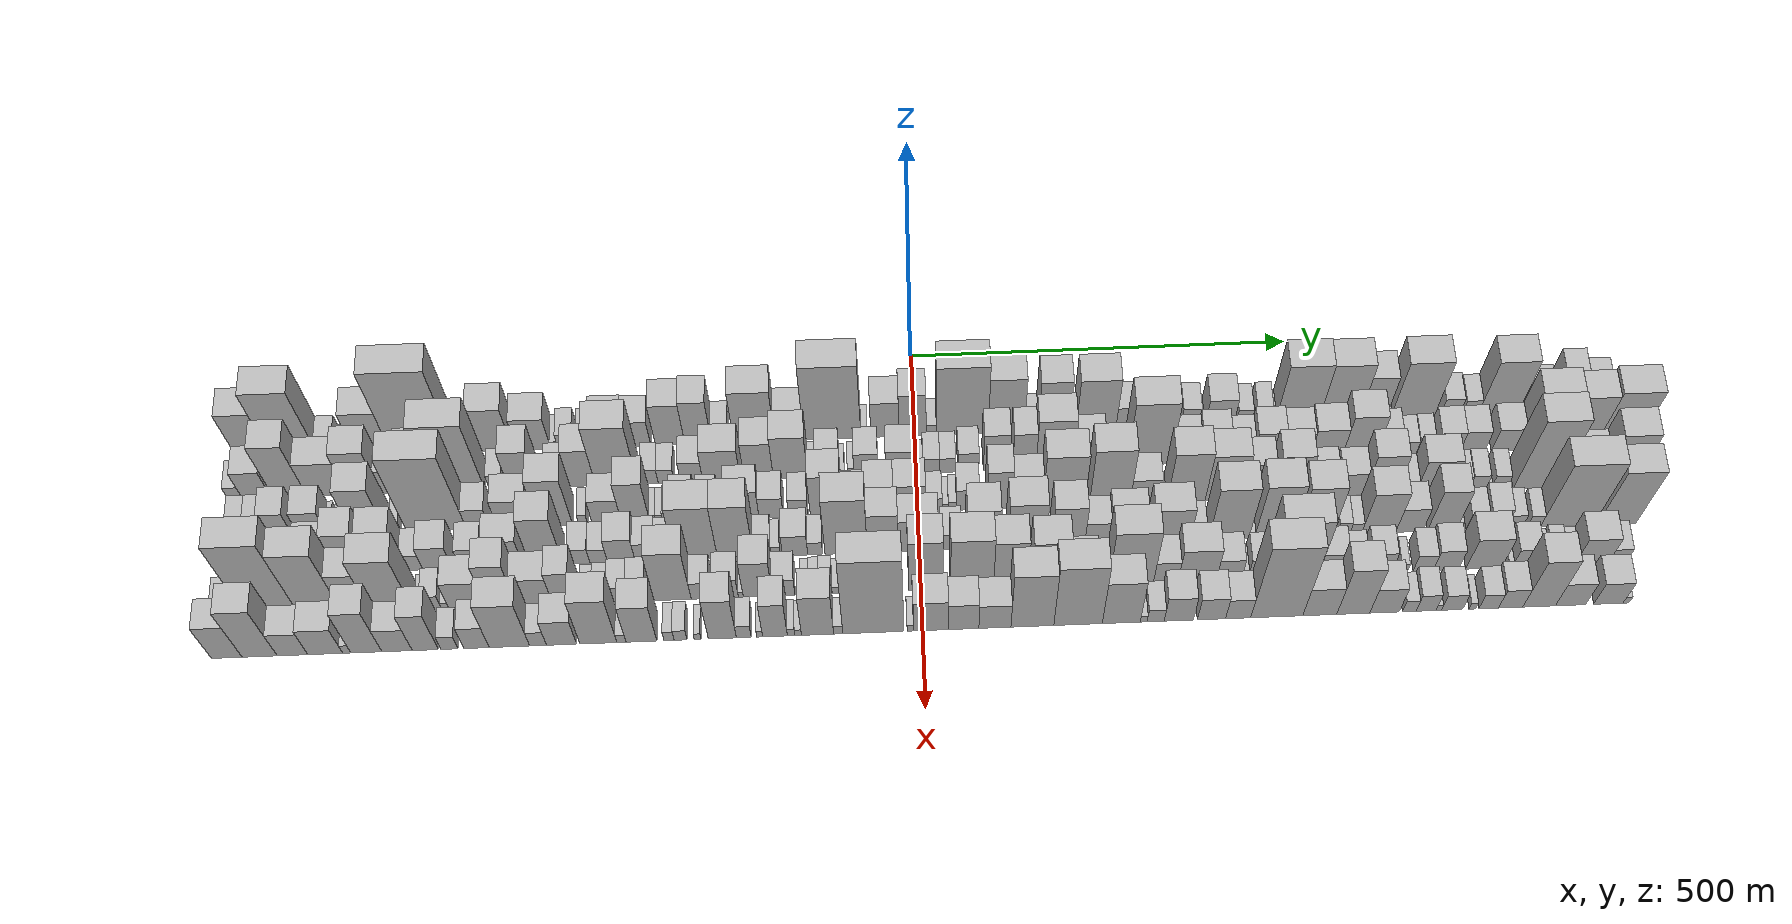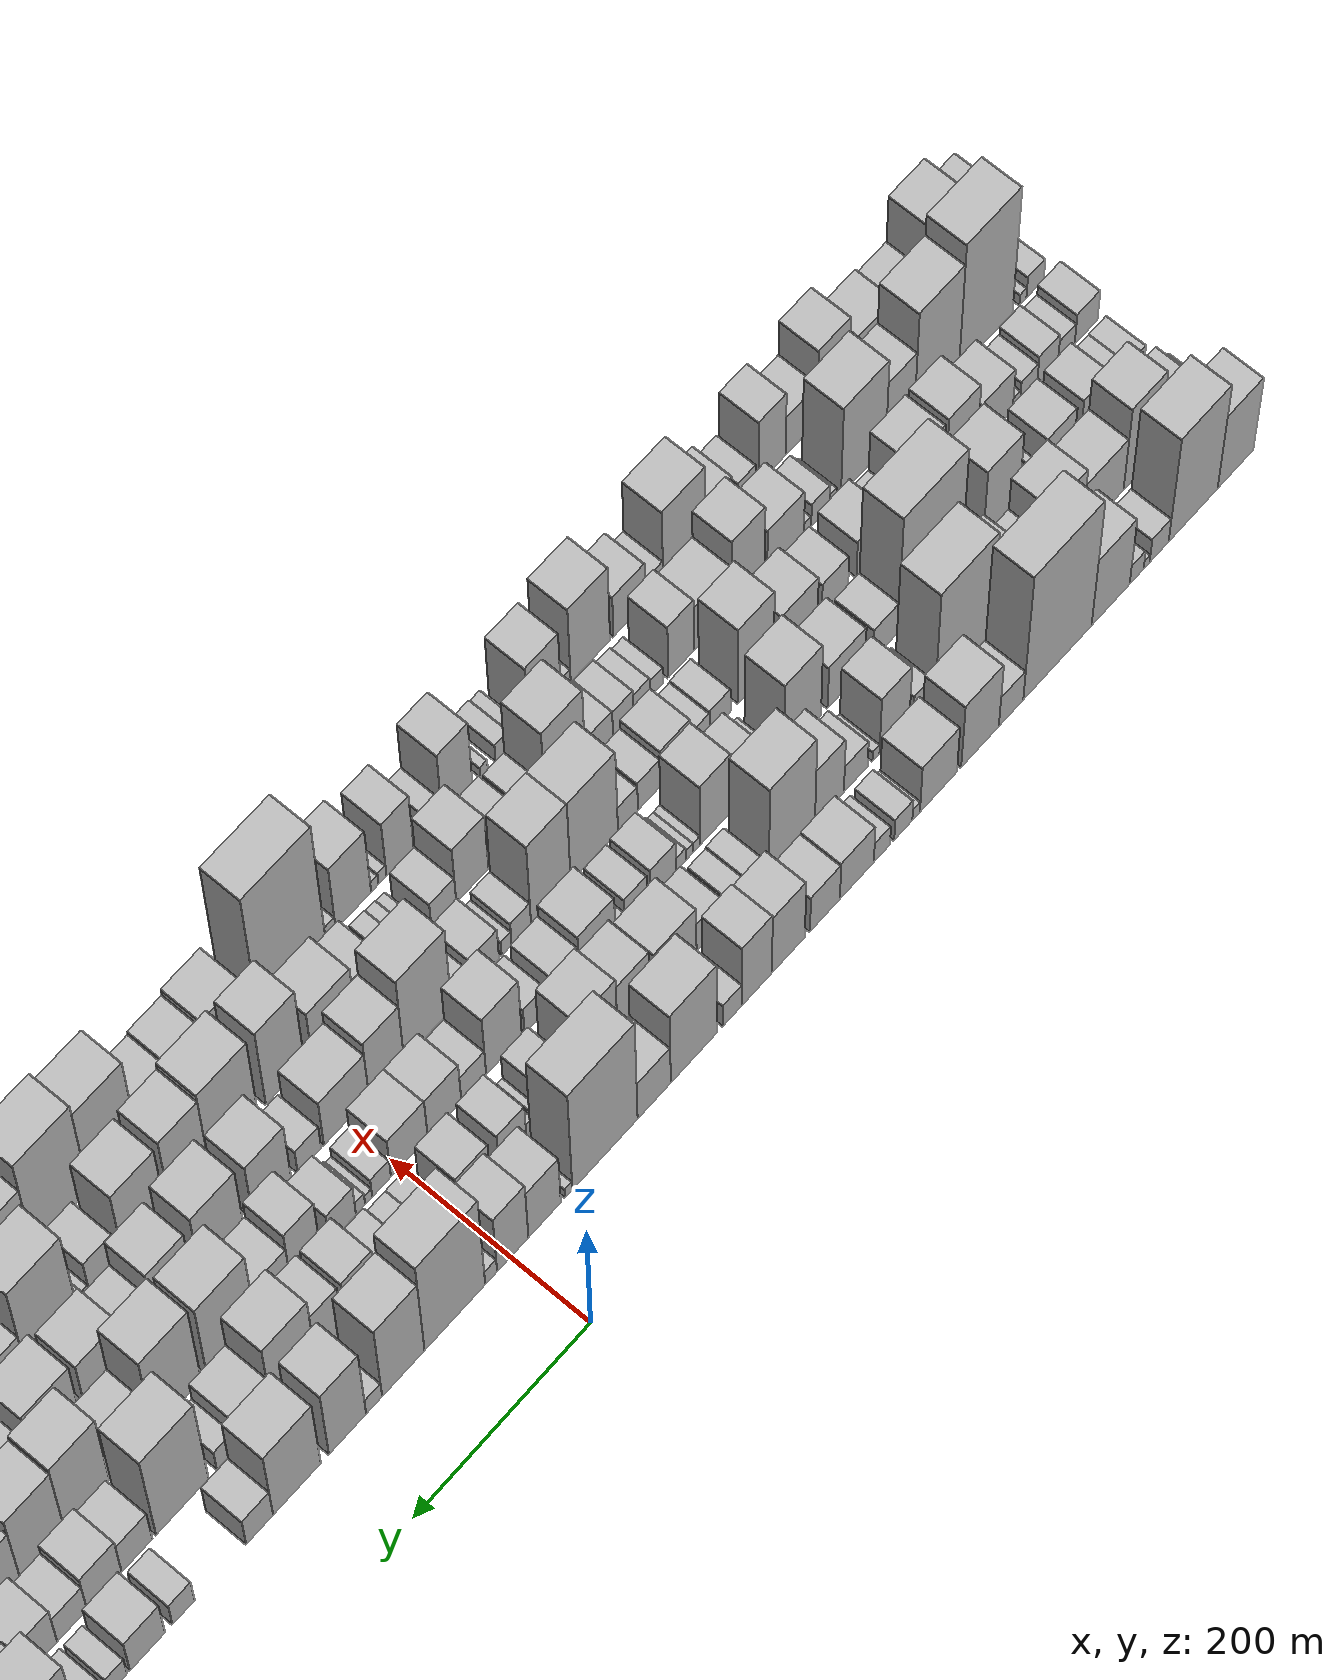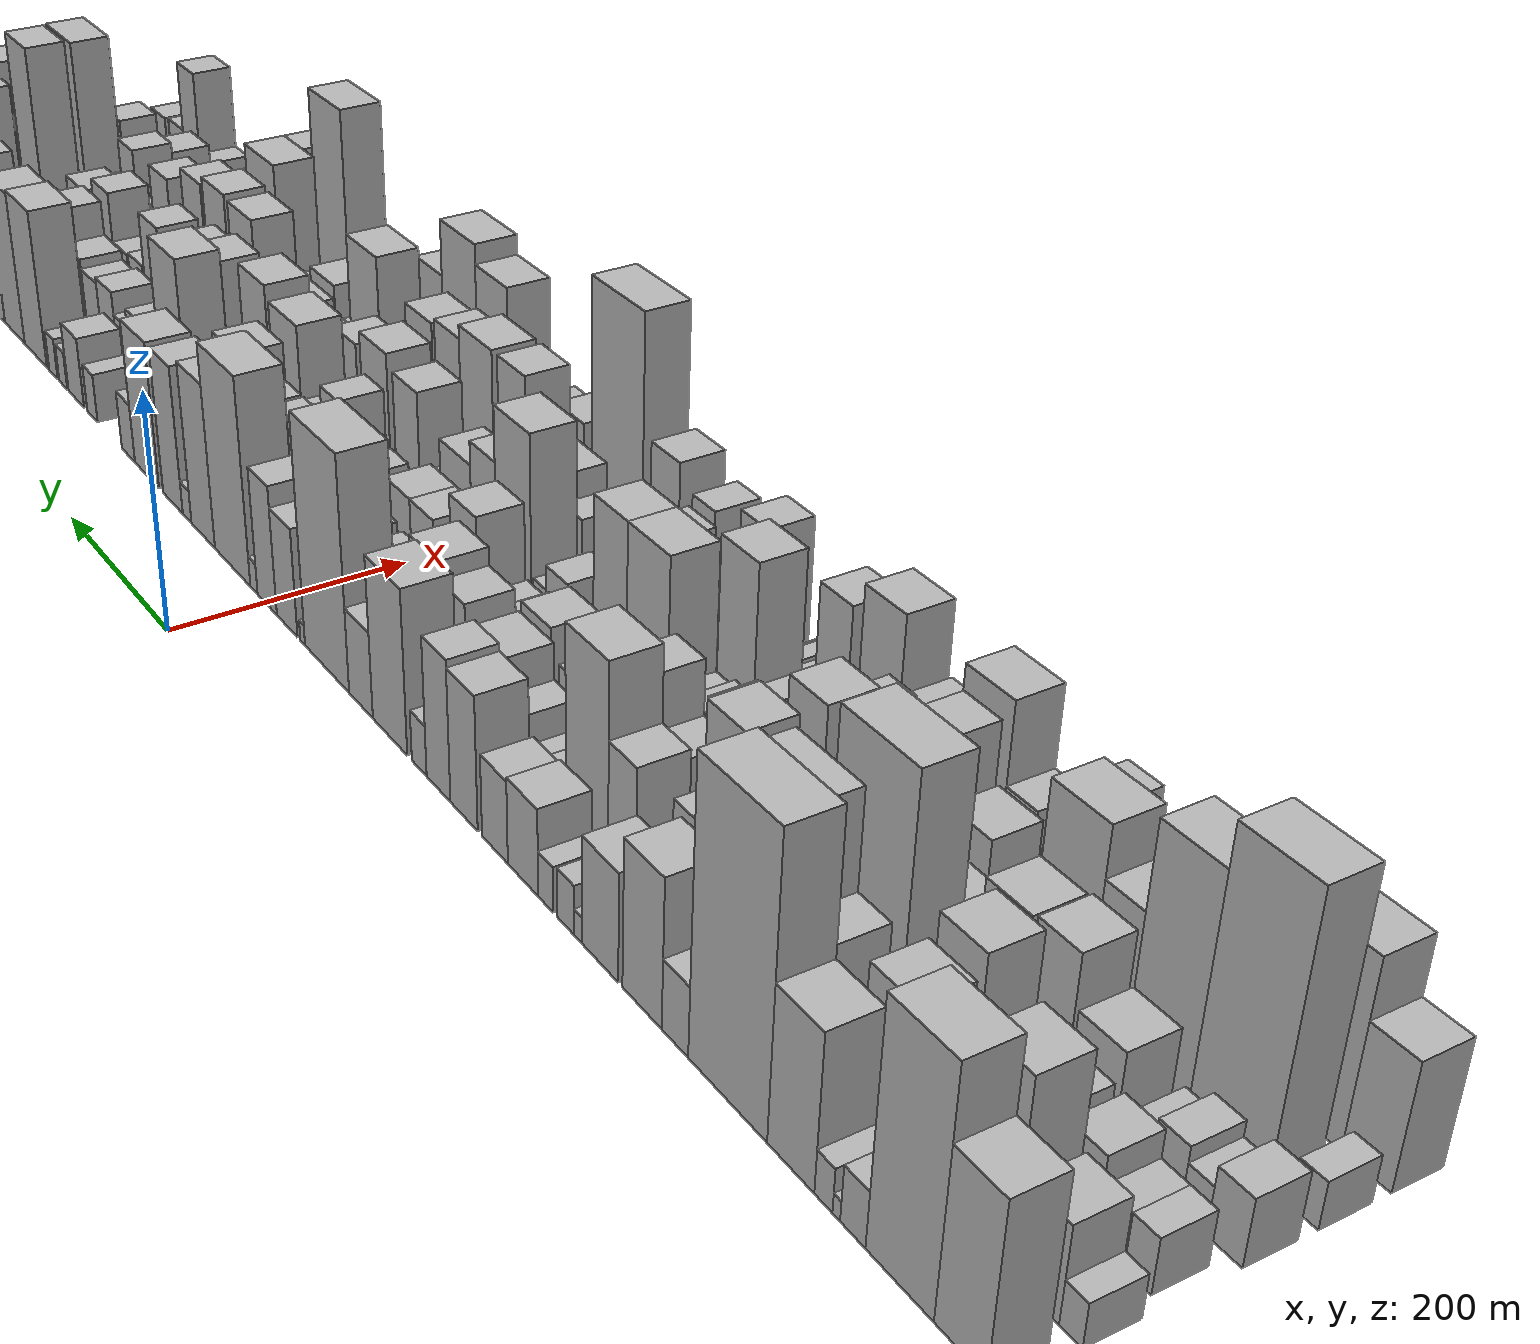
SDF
<sdf version="1.6">
 <world name="default">
  <scene>
   <sky><clouds><speed>12</speed></clouds></sky>
   <ambient>0.4 0.4 0.4 1</ambient>
   <background>0.7 0.7 0.7 1</background>
   <shadows>1</shadows>
  </scene>
  <gravity>0 0 -9.8066</gravity>
  <magnetic_field>6e-06 2.3e-05 -4.2e-05</magnetic_field>
  <physics default="0" name="default_physics" type="ode">
   <ode>
    <solver>
     <type>quick</type>
     <iters>10</iters>
     <sor>1.0</sor>
     <use_dynamic_moi_rescaling>0</use_dynamic_moi_rescaling>
    </solver>
    <constraints>
     <cfm>0</cfm>
     <erp>0.2</erp>
     <contact_max_correcting_vel>100</contact_max_correcting_vel>
     <contact_surface_layer>0.001</contact_surface_layer>
    </constraints>
   </ode>
   <max_step_size>0.004</max_step_size>
   <real_time_factor>1</real_time_factor>
   <real_time_update_rate>250</real_time_update_rate>
  </physics>
  <light name="sun" type="directional">
   <pose>0 0 10 0 0 0</pose>
   <diffuse>0.8 0.8 0.8 1</diffuse>
   <specular>0.2 0.2 0.2 1</specular>
   <attenuation>
    <range>1000</range>
    <constant>0.9</constant>
    <linear>0.01</linear>
    <quadratic>0.001</quadratic>
   </attenuation>
   <direction>-0.5 0.1 -0.9</direction>
  </light>
  <model name="building_1">
   <static>1</static>
   <pose>100.0000 -858.8363 0 0.000000 0.000000 0.000000</pose>
   <link name="link">
    <pose>0 0 63.00 0 0 0</pose>
    <collision name="collision"><geometry><box><size>40.0000 44.3274 126.0000</size></box></geometry></collision>
    <visual name="visual">
     <cast_shadows>0</cast_shadows>
     <geometry><box><size>40.0000 44.3274 126.0000</size></box></geometry>
     <material>
      <script>
       <uri>model://HANNAS_wall/materials/scripts</uri>
       <uri>model://HANNAS_wall/materials/textures</uri>
       <name>vrc/HANNAS_wall</name>
      </script>
     </material>
    </visual>
   </link>
  </model>
  <model name="building_2">
   <static>1</static>
   <pose>100.0000 -806.4350 0 0.000000 0.000000 0.000000</pose>
   <link name="link">
    <pose>0 0 90.00 0 0 0</pose>
    <collision name="collision"><geometry><box><size>40.0000 60.4753 180.0000</size></box></geometry></collision>
    <visual name="visual">
     <cast_shadows>0</cast_shadows>
     <geometry><box><size>40.0000 60.4753 180.0000</size></box></geometry>
     <material>
      <script>
       <uri>model://HANNAS_wall/materials/scripts</uri>
       <uri>model://HANNAS_wall/materials/textures</uri>
       <name>vrc/HANNAS_wall</name>
      </script>
     </material>
    </visual>
   </link>
  </model>
  <model name="building_3">
   <static>1</static>
   <pose>100.0000 -764.4830 0 0.000000 0.000000 0.000000</pose>
   <link name="link">
    <pose>0 0 21.00 0 0 0</pose>
    <collision name="collision"><geometry><box><size>40.0000 23.4287 42.0000</size></box></geometry></collision>
    <visual name="visual">
     <cast_shadows>0</cast_shadows>
     <geometry><box><size>40.0000 23.4287 42.0000</size></box></geometry>
     <material>
      <script>
       <uri>model://HANNAS_wall/materials/scripts</uri>
       <uri>model://HANNAS_wall/materials/textures</uri>
       <name>vrc/HANNAS_wall</name>
      </script>
     </material>
    </visual>
   </link>
  </model>
  <model name="building_4">
   <static>1</static>
   <pose>100.0000 -749.1663 0 0.000000 0.000000 0.000000</pose>
   <link name="link">
    <pose>0 0 7.50 0 0 0</pose>
    <collision name="collision"><geometry><box><size>40.0000 7.2047 15.0000</size></box></geometry></collision>
    <visual name="visual">
     <cast_shadows>0</cast_shadows>
     <geometry><box><size>40.0000 7.2047 15.0000</size></box></geometry>
     <material>
      <script>
       <uri>model://HANNAS_wall/materials/scripts</uri>
       <uri>model://HANNAS_wall/materials/textures</uri>
       <name>vrc/HANNAS_wall</name>
      </script>
     </material>
    </visual>
   </link>
  </model>
  <model name="building_5">
   <static>1</static>
   <pose>100.0000 -736.9335 0 0.000000 0.000000 0.000000</pose>
   <link name="link">
    <pose>0 0 16.50 0 0 0</pose>
    <collision name="collision"><geometry><box><size>40.0000 17.2609 33.0000</size></box></geometry></collision>
    <visual name="visual">
     <cast_shadows>0</cast_shadows>
     <geometry><box><size>40.0000 17.2609 33.0000</size></box></geometry>
     <material>
      <script>
       <uri>model://HANNAS_wall/materials/scripts</uri>
       <uri>model://HANNAS_wall/materials/textures</uri>
       <name>vrc/HANNAS_wall</name>
      </script>
     </material>
    </visual>
   </link>
  </model>
  <model name="building_6">
   <static>1</static>
   <pose>100.0000 -705.0831 0 0.000000 0.000000 0.000000</pose>
   <link name="link">
    <pose>0 0 58.50 0 0 0</pose>
    <collision name="collision"><geometry><box><size>40.0000 46.4398 117.0000</size></box></geometry></collision>
    <visual name="visual">
     <cast_shadows>0</cast_shadows>
     <geometry><box><size>40.0000 46.4398 117.0000</size></box></geometry>
     <material>
      <script>
       <uri>model://HANNAS_wall/materials/scripts</uri>
       <uri>model://HANNAS_wall/materials/textures</uri>
       <name>vrc/HANNAS_wall</name>
      </script>
     </material>
    </visual>
   </link>
  </model>
  <model name="building_7">
   <static>1</static>
   <pose>100.0000 -640.3496 0 0.000000 0.000000 0.000000</pose>
   <link name="link">
    <pose>0 0 111.00 0 0 0</pose>
    <collision name="collision"><geometry><box><size>40.0000 83.0273 222.0000</size></box></geometry></collision>
    <visual name="visual">
     <cast_shadows>0</cast_shadows>
     <geometry><box><size>40.0000 83.0273 222.0000</size></box></geometry>
     <material>
      <script>
       <uri>model://HANNAS_wall/materials/scripts</uri>
       <uri>model://HANNAS_wall/materials/textures</uri>
       <name>vrc/HANNAS_wall</name>
      </script>
     </material>
    </visual>
   </link>
  </model>
  <model name="building_8">
   <static>1</static>
   <pose>100.0000 -584.0947 0 0.000000 0.000000 0.000000</pose>
   <link name="link">
    <pose>0 0 27.00 0 0 0</pose>
    <collision name="collision"><geometry><box><size>40.0000 29.4825 54.0000</size></box></geometry></collision>
    <visual name="visual">
     <cast_shadows>0</cast_shadows>
     <geometry><box><size>40.0000 29.4825 54.0000</size></box></geometry>
     <material>
      <script>
       <uri>model://HANNAS_wall/materials/scripts</uri>
       <uri>model://HANNAS_wall/materials/textures</uri>
       <name>vrc/HANNAS_wall</name>
      </script>
     </material>
    </visual>
   </link>
  </model>
  <model name="building_9">
   <static>1</static>
   <pose>100.0000 -546.7475 0 0.000000 0.000000 0.000000</pose>
   <link name="link">
    <pose>0 0 57.00 0 0 0</pose>
    <collision name="collision"><geometry><box><size>40.0000 45.2120 114.0000</size></box></geometry></collision>
    <visual name="visual">
     <cast_shadows>0</cast_shadows>
     <geometry><box><size>40.0000 45.2120 114.0000</size></box></geometry>
     <material>
      <script>
       <uri>model://HANNAS_wall/materials/scripts</uri>
       <uri>model://HANNAS_wall/materials/textures</uri>
       <name>vrc/HANNAS_wall</name>
      </script>
     </material>
    </visual>
   </link>
  </model>
  <model name="building_10">
   <static>1</static>
   <pose>100.0000 -497.0133 0 0.000000 0.000000 0.000000</pose>
   <link name="link">
    <pose>0 0 42.00 0 0 0</pose>
    <collision name="collision"><geometry><box><size>40.0000 44.2564 84.0000</size></box></geometry></collision>
    <visual name="visual">
     <cast_shadows>0</cast_shadows>
     <geometry><box><size>40.0000 44.2564 84.0000</size></box></geometry>
     <material>
      <script>
       <uri>model://HANNAS_wall/materials/scripts</uri>
       <uri>model://HANNAS_wall/materials/textures</uri>
       <name>vrc/HANNAS_wall</name>
      </script>
     </material>
    </visual>
   </link>
  </model>
  <model name="building_11">
   <static>1</static>
   <pose>100.0000 -470.3481 0 0.000000 0.000000 0.000000</pose>
   <link name="link">
    <pose>0 0 10.50 0 0 0</pose>
    <collision name="collision"><geometry><box><size>40.0000 9.0740 21.0000</size></box></geometry></collision>
    <visual name="visual">
     <cast_shadows>0</cast_shadows>
     <geometry><box><size>40.0000 9.0740 21.0000</size></box></geometry>
     <material>
      <script>
       <uri>model://HANNAS_wall/materials/scripts</uri>
       <uri>model://HANNAS_wall/materials/textures</uri>
       <name>vrc/HANNAS_wall</name>
      </script>
     </material>
    </visual>
   </link>
  </model>
  <model name="building_12">
   <static>1</static>
   <pose>100.0000 -455.0372 0 0.000000 0.000000 0.000000</pose>
   <link name="link">
    <pose>0 0 19.50 0 0 0</pose>
    <collision name="collision"><geometry><box><size>40.0000 21.5479 39.0000</size></box></geometry></collision>
    <visual name="visual">
     <cast_shadows>0</cast_shadows>
     <geometry><box><size>40.0000 21.5479 39.0000</size></box></geometry>
     <material>
      <script>
       <uri>model://HANNAS_wall/materials/scripts</uri>
       <uri>model://HANNAS_wall/materials/textures</uri>
       <name>vrc/HANNAS_wall</name>
      </script>
     </material>
    </visual>
   </link>
  </model>
  <model name="building_13">
   <static>1</static>
   <pose>100.0000 -429.6886 0 0.000000 0.000000 0.000000</pose>
   <link name="link">
    <pose>0 0 18.00 0 0 0</pose>
    <collision name="collision"><geometry><box><size>40.0000 19.1492 36.0000</size></box></geometry></collision>
    <visual name="visual">
     <cast_shadows>0</cast_shadows>
     <geometry><box><size>40.0000 19.1492 36.0000</size></box></geometry>
     <material>
      <script>
       <uri>model://HANNAS_wall/materials/scripts</uri>
       <uri>model://HANNAS_wall/materials/textures</uri>
       <name>vrc/HANNAS_wall</name>
      </script>
     </material>
    </visual>
   </link>
  </model>
  <model name="building_14">
   <static>1</static>
   <pose>100.0000 -400.0632 0 0.000000 0.000000 0.000000</pose>
   <link name="link">
    <pose>0 0 34.50 0 0 0</pose>
    <collision name="collision"><geometry><box><size>40.0000 40.1018 69.0000</size></box></geometry></collision>
    <visual name="visual">
     <cast_shadows>0</cast_shadows>
     <geometry><box><size>40.0000 40.1018 69.0000</size></box></geometry>
     <material>
      <script>
       <uri>model://HANNAS_wall/materials/scripts</uri>
       <uri>model://HANNAS_wall/materials/textures</uri>
       <name>vrc/HANNAS_wall</name>
      </script>
     </material>
    </visual>
   </link>
  </model>
  <model name="building_15">
   <static>1</static>
   <pose>100.0000 -362.3942 0 0.000000 0.000000 0.000000</pose>
   <link name="link">
    <pose>0 0 33.00 0 0 0</pose>
    <collision name="collision"><geometry><box><size>40.0000 35.2361 66.0000</size></box></geometry></collision>
    <visual name="visual">
     <cast_shadows>0</cast_shadows>
     <geometry><box><size>40.0000 35.2361 66.0000</size></box></geometry>
     <material>
      <script>
       <uri>model://HANNAS_wall/materials/scripts</uri>
       <uri>model://HANNAS_wall/materials/textures</uri>
       <name>vrc/HANNAS_wall</name>
      </script>
     </material>
    </visual>
   </link>
  </model>
  <model name="building_16">
   <static>1</static>
   <pose>100.0000 -319.4540 0 0.000000 0.000000 0.000000</pose>
   <link name="link">
    <pose>0 0 54.00 0 0 0</pose>
    <collision name="collision"><geometry><box><size>40.0000 38.6444 108.0000</size></box></geometry></collision>
    <visual name="visual">
     <cast_shadows>0</cast_shadows>
     <geometry><box><size>40.0000 38.6444 108.0000</size></box></geometry>
     <material>
      <script>
       <uri>model://HANNAS_wall/materials/scripts</uri>
       <uri>model://HANNAS_wall/materials/textures</uri>
       <name>vrc/HANNAS_wall</name>
      </script>
     </material>
    </visual>
   </link>
  </model>
  <model name="building_17">
   <static>1</static>
   <pose>100.0000 -282.7095 0 0.000000 0.000000 0.000000</pose>
   <link name="link">
    <pose>0 0 57.00 0 0 0</pose>
    <collision name="collision"><geometry><box><size>40.0000 34.8445 114.0000</size></box></geometry></collision>
    <visual name="visual">
     <cast_shadows>0</cast_shadows>
     <geometry><box><size>40.0000 34.8445 114.0000</size></box></geometry>
     <material>
      <script>
       <uri>model://HANNAS_wall/materials/scripts</uri>
       <uri>model://HANNAS_wall/materials/textures</uri>
       <name>vrc/HANNAS_wall</name>
      </script>
     </material>
    </visual>
   </link>
  </model>
  <model name="building_18">
   <static>1</static>
   <pose>100.0000 -254.2421 0 0.000000 0.000000 0.000000</pose>
   <link name="link">
    <pose>0 0 21.00 0 0 0</pose>
    <collision name="collision"><geometry><box><size>40.0000 22.0904 42.0000</size></box></geometry></collision>
    <visual name="visual">
     <cast_shadows>0</cast_shadows>
     <geometry><box><size>40.0000 22.0904 42.0000</size></box></geometry>
     <material>
      <script>
       <uri>model://HANNAS_wall/materials/scripts</uri>
       <uri>model://HANNAS_wall/materials/textures</uri>
       <name>vrc/HANNAS_wall</name>
      </script>
     </material>
    </visual>
   </link>
  </model>
  <model name="building_19">
   <static>1</static>
   <pose>100.0000 -209.4615 0 0.000000 0.000000 0.000000</pose>
   <link name="link">
    <pose>0 0 67.50 0 0 0</pose>
    <collision name="collision"><geometry><box><size>40.0000 53.4707 135.0000</size></box></geometry></collision>
    <visual name="visual">
     <cast_shadows>0</cast_shadows>
     <geometry><box><size>40.0000 53.4707 135.0000</size></box></geometry>
     <material>
      <script>
       <uri>model://HANNAS_wall/materials/scripts</uri>
       <uri>model://HANNAS_wall/materials/textures</uri>
       <name>vrc/HANNAS_wall</name>
      </script>
     </material>
    </visual>
   </link>
  </model>
  <model name="building_20">
   <static>1</static>
   <pose>100.0000 -163.5887 0 0.000000 0.000000 0.000000</pose>
   <link name="link">
    <pose>0 0 36.00 0 0 0</pose>
    <collision name="collision"><geometry><box><size>40.0000 38.2750 72.0000</size></box></geometry></collision>
    <visual name="visual">
     <cast_shadows>0</cast_shadows>
     <geometry><box><size>40.0000 38.2750 72.0000</size></box></geometry>
     <material>
      <script>
       <uri>model://HANNAS_wall/materials/scripts</uri>
       <uri>model://HANNAS_wall/materials/textures</uri>
       <name>vrc/HANNAS_wall</name>
      </script>
     </material>
    </visual>
   </link>
  </model>
  <model name="building_21">
   <static>1</static>
   <pose>100.0000 -107.1721 0 0.000000 0.000000 0.000000</pose>
   <link name="link">
    <pose>0 0 97.50 0 0 0</pose>
    <collision name="collision"><geometry><box><size>40.0000 74.5581 195.0000</size></box></geometry></collision>
    <visual name="visual">
     <cast_shadows>0</cast_shadows>
     <geometry><box><size>40.0000 74.5581 195.0000</size></box></geometry>
     <material>
      <script>
       <uri>model://HANNAS_wall/materials/scripts</uri>
       <uri>model://HANNAS_wall/materials/textures</uri>
       <name>vrc/HANNAS_wall</name>
      </script>
     </material>
    </visual>
   </link>
  </model>
  <model name="building_22">
   <static>1</static>
   <pose>100.0000 -65.8236 0 0.000000 0.000000 0.000000</pose>
   <link name="link">
    <pose>0 0 9.00 0 0 0</pose>
    <collision name="collision"><geometry><box><size>40.0000 8.1389 18.0000</size></box></geometry></collision>
    <visual name="visual">
     <cast_shadows>0</cast_shadows>
     <geometry><box><size>40.0000 8.1389 18.0000</size></box></geometry>
     <material>
      <script>
       <uri>model://HANNAS_wall/materials/scripts</uri>
       <uri>model://HANNAS_wall/materials/textures</uri>
       <name>vrc/HANNAS_wall</name>
      </script>
     </material>
    </visual>
   </link>
  </model>
  <model name="building_23">
   <static>1</static>
   <pose>100.0000 -38.3440 0 0.000000 0.000000 0.000000</pose>
   <link name="link">
    <pose>0 0 46.50 0 0 0</pose>
    <collision name="collision"><geometry><box><size>40.0000 36.8203 93.0000</size></box></geometry></collision>
    <visual name="visual">
     <cast_shadows>0</cast_shadows>
     <geometry><box><size>40.0000 36.8203 93.0000</size></box></geometry>
     <material>
      <script>
       <uri>model://HANNAS_wall/materials/scripts</uri>
       <uri>model://HANNAS_wall/materials/textures</uri>
       <name>vrc/HANNAS_wall</name>
      </script>
     </material>
    </visual>
   </link>
  </model>
  <model name="building_24">
   <static>1</static>
   <pose>100.0000 -2.2294 0 0.000000 0.000000 0.000000</pose>
   <link name="link">
    <pose>0 0 55.50 0 0 0</pose>
    <collision name="collision"><geometry><box><size>40.0000 35.4090 111.0000</size></box></geometry></collision>
    <visual name="visual">
     <cast_shadows>0</cast_shadows>
     <geometry><box><size>40.0000 35.4090 111.0000</size></box></geometry>
     <material>
      <script>
       <uri>model://HANNAS_wall/materials/scripts</uri>
       <uri>model://HANNAS_wall/materials/textures</uri>
       <name>vrc/HANNAS_wall</name>
      </script>
     </material>
    </visual>
   </link>
  </model>
  <model name="building_25">
   <static>1</static>
   <pose>100.0000 22.1631 0 0.000000 0.000000 0.000000</pose>
   <link name="link">
    <pose>0 0 13.50 0 0 0</pose>
    <collision name="collision"><geometry><box><size>40.0000 13.3759 27.0000</size></box></geometry></collision>
    <visual name="visual">
     <cast_shadows>0</cast_shadows>
     <geometry><box><size>40.0000 13.3759 27.0000</size></box></geometry>
     <material>
      <script>
       <uri>model://HANNAS_wall/materials/scripts</uri>
       <uri>model://HANNAS_wall/materials/textures</uri>
       <name>vrc/HANNAS_wall</name>
      </script>
     </material>
    </visual>
   </link>
  </model>
  <model name="building_26">
   <static>1</static>
   <pose>100.0000 62.9085 0 0.000000 0.000000 0.000000</pose>
   <link name="link">
    <pose>0 0 90.00 0 0 0</pose>
    <collision name="collision"><geometry><box><size>40.0000 68.1148 180.0000</size></box></geometry></collision>
    <visual name="visual">
     <cast_shadows>0</cast_shadows>
     <geometry><box><size>40.0000 68.1148 180.0000</size></box></geometry>
     <material>
      <script>
       <uri>model://HANNAS_wall/materials/scripts</uri>
       <uri>model://HANNAS_wall/materials/textures</uri>
       <name>vrc/HANNAS_wall</name>
      </script>
     </material>
    </visual>
   </link>
  </model>
  <model name="building_27">
   <static>1</static>
   <pose>100.0000 120.6021 0 0.000000 0.000000 0.000000</pose>
   <link name="link">
    <pose>0 0 72.00 0 0 0</pose>
    <collision name="collision"><geometry><box><size>40.0000 47.2725 144.0000</size></box></geometry></collision>
    <visual name="visual">
     <cast_shadows>0</cast_shadows>
     <geometry><box><size>40.0000 47.2725 144.0000</size></box></geometry>
     <material>
      <script>
       <uri>model://HANNAS_wall/materials/scripts</uri>
       <uri>model://HANNAS_wall/materials/textures</uri>
       <name>vrc/HANNAS_wall</name>
      </script>
     </material>
    </visual>
   </link>
  </model>
  <model name="building_28">
   <static>1</static>
   <pose>100.0000 153.1392 0 0.000000 0.000000 0.000000</pose>
   <link name="link">
    <pose>0 0 15.00 0 0 0</pose>
    <collision name="collision"><geometry><box><size>40.0000 17.8015 30.0000</size></box></geometry></collision>
    <visual name="visual">
     <cast_shadows>0</cast_shadows>
     <geometry><box><size>40.0000 17.8015 30.0000</size></box></geometry>
     <material>
      <script>
       <uri>model://HANNAS_wall/materials/scripts</uri>
       <uri>model://HANNAS_wall/materials/textures</uri>
       <name>vrc/HANNAS_wall</name>
      </script>
     </material>
    </visual>
   </link>
  </model>
  <model name="building_29">
   <static>1</static>
   <pose>100.0000 182.6513 0 0.000000 0.000000 0.000000</pose>
   <link name="link">
    <pose>0 0 66.00 0 0 0</pose>
    <collision name="collision"><geometry><box><size>40.0000 41.2226 132.0000</size></box></geometry></collision>
    <visual name="visual">
     <cast_shadows>0</cast_shadows>
     <geometry><box><size>40.0000 41.2226 132.0000</size></box></geometry>
     <material>
      <script>
       <uri>model://HANNAS_wall/materials/scripts</uri>
       <uri>model://HANNAS_wall/materials/textures</uri>
       <name>vrc/HANNAS_wall</name>
      </script>
     </material>
    </visual>
   </link>
  </model>
  <model name="building_30">
   <static>1</static>
   <pose>100.0000 238.4440 0 0.000000 0.000000 0.000000</pose>
   <link name="link">
    <pose>0 0 66.00 0 0 0</pose>
    <collision name="collision"><geometry><box><size>40.0000 52.3628 132.0000</size></box></geometry></collision>
    <visual name="visual">
     <cast_shadows>0</cast_shadows>
     <geometry><box><size>40.0000 52.3628 132.0000</size></box></geometry>
     <material>
      <script>
       <uri>model://HANNAS_wall/materials/scripts</uri>
       <uri>model://HANNAS_wall/materials/textures</uri>
       <name>vrc/HANNAS_wall</name>
      </script>
     </material>
    </visual>
   </link>
  </model>
  <model name="building_31">
   <static>1</static>
   <pose>100.0000 279.4099 0 0.000000 0.000000 0.000000</pose>
   <link name="link">
    <pose>0 0 27.00 0 0 0</pose>
    <collision name="collision"><geometry><box><size>40.0000 29.5690 54.0000</size></box></geometry></collision>
    <visual name="visual">
     <cast_shadows>0</cast_shadows>
     <geometry><box><size>40.0000 29.5690 54.0000</size></box></geometry>
     <material>
      <script>
       <uri>model://HANNAS_wall/materials/scripts</uri>
       <uri>model://HANNAS_wall/materials/textures</uri>
       <name>vrc/HANNAS_wall</name>
      </script>
     </material>
    </visual>
   </link>
  </model>
  <model name="building_32">
   <static>1</static>
   <pose>100.0000 362.4046 0 0.000000 0.000000 0.000000</pose>
   <link name="link">
    <pose>0 0 22.50 0 0 0</pose>
    <collision name="collision"><geometry><box><size>40.0000 24.1402 45.0000</size></box></geometry></collision>
    <visual name="visual">
     <cast_shadows>0</cast_shadows>
     <geometry><box><size>40.0000 24.1402 45.0000</size></box></geometry>
     <material>
      <script>
       <uri>model://HANNAS_wall/materials/scripts</uri>
       <uri>model://HANNAS_wall/materials/textures</uri>
       <name>vrc/HANNAS_wall</name>
      </script>
     </material>
    </visual>
   </link>
  </model>
  <model name="building_33">
   <static>1</static>
   <pose>100.0000 401.4034 0 0.000000 0.000000 0.000000</pose>
   <link name="link">
    <pose>0 0 33.00 0 0 0</pose>
    <collision name="collision"><geometry><box><size>40.0000 37.8573 66.0000</size></box></geometry></collision>
    <visual name="visual">
     <cast_shadows>0</cast_shadows>
     <geometry><box><size>40.0000 37.8573 66.0000</size></box></geometry>
     <material>
      <script>
       <uri>model://HANNAS_wall/materials/scripts</uri>
       <uri>model://HANNAS_wall/materials/textures</uri>
       <name>vrc/HANNAS_wall</name>
      </script>
     </material>
    </visual>
   </link>
  </model>
  <model name="building_34">
   <static>1</static>
   <pose>100.0000 433.3252 0 0.000000 0.000000 0.000000</pose>
   <link name="link">
    <pose>0 0 18.00 0 0 0</pose>
    <collision name="collision"><geometry><box><size>40.0000 19.9862 36.0000</size></box></geometry></collision>
    <visual name="visual">
     <cast_shadows>0</cast_shadows>
     <geometry><box><size>40.0000 19.9862 36.0000</size></box></geometry>
     <material>
      <script>
       <uri>model://HANNAS_wall/materials/scripts</uri>
       <uri>model://HANNAS_wall/materials/textures</uri>
       <name>vrc/HANNAS_wall</name>
      </script>
     </material>
    </visual>
   </link>
  </model>
  <model name="building_35">
   <static>1</static>
   <pose>100.0000 457.9261 0 0.000000 0.000000 0.000000</pose>
   <link name="link">
    <pose>0 0 19.50 0 0 0</pose>
    <collision name="collision"><geometry><box><size>40.0000 21.2158 39.0000</size></box></geometry></collision>
    <visual name="visual">
     <cast_shadows>0</cast_shadows>
     <geometry><box><size>40.0000 21.2158 39.0000</size></box></geometry>
     <material>
      <script>
       <uri>model://HANNAS_wall/materials/scripts</uri>
       <uri>model://HANNAS_wall/materials/textures</uri>
       <name>vrc/HANNAS_wall</name>
      </script>
     </material>
    </visual>
   </link>
  </model>
  <model name="building_36">
   <static>1</static>
   <pose>100.0000 471.7469 0 0.000000 0.000000 0.000000</pose>
   <link name="link">
    <pose>0 0 7.50 0 0 0</pose>
    <collision name="collision"><geometry><box><size>40.0000 6.4258 15.0000</size></box></geometry></collision>
    <visual name="visual">
     <cast_shadows>0</cast_shadows>
     <geometry><box><size>40.0000 6.4258 15.0000</size></box></geometry>
     <material>
      <script>
       <uri>model://HANNAS_wall/materials/scripts</uri>
       <uri>model://HANNAS_wall/materials/textures</uri>
       <name>vrc/HANNAS_wall</name>
      </script>
     </material>
    </visual>
   </link>
  </model>
  <model name="building_37">
   <static>1</static>
   <pose>100.0000 503.7279 0 0.000000 0.000000 0.000000</pose>
   <link name="link">
    <pose>0 0 75.00 0 0 0</pose>
    <collision name="collision"><geometry><box><size>40.0000 57.5362 150.0000</size></box></geometry></collision>
    <visual name="visual">
     <cast_shadows>0</cast_shadows>
     <geometry><box><size>40.0000 57.5362 150.0000</size></box></geometry>
     <material>
      <script>
       <uri>model://HANNAS_wall/materials/scripts</uri>
       <uri>model://HANNAS_wall/materials/textures</uri>
       <name>vrc/HANNAS_wall</name>
      </script>
     </material>
    </visual>
   </link>
  </model>
  <model name="building_38">
   <static>1</static>
   <pose>100.0000 559.0571 0 0.000000 0.000000 0.000000</pose>
   <link name="link">
    <pose>0 0 73.50 0 0 0</pose>
    <collision name="collision"><geometry><box><size>40.0000 53.1222 147.0000</size></box></geometry></collision>
    <visual name="visual">
     <cast_shadows>0</cast_shadows>
     <geometry><box><size>40.0000 53.1222 147.0000</size></box></geometry>
     <material>
      <script>
       <uri>model://HANNAS_wall/materials/scripts</uri>
       <uri>model://HANNAS_wall/materials/textures</uri>
       <name>vrc/HANNAS_wall</name>
      </script>
     </material>
    </visual>
   </link>
  </model>
  <model name="building_39">
   <static>1</static>
   <pose>100.0000 603.3156 0 0.000000 0.000000 0.000000</pose>
   <link name="link">
    <pose>0 0 55.50 0 0 0</pose>
    <collision name="collision"><geometry><box><size>40.0000 35.3948 111.0000</size></box></geometry></collision>
    <visual name="visual">
     <cast_shadows>0</cast_shadows>
     <geometry><box><size>40.0000 35.3948 111.0000</size></box></geometry>
     <material>
      <script>
       <uri>model://HANNAS_wall/materials/scripts</uri>
       <uri>model://HANNAS_wall/materials/textures</uri>
       <name>vrc/HANNAS_wall</name>
      </script>
     </material>
    </visual>
   </link>
  </model>
  <model name="building_40">
   <static>1</static>
   <pose>100.0000 624.0518 0 0.000000 0.000000 0.000000</pose>
   <link name="link">
    <pose>0 0 7.50 0 0 0</pose>
    <collision name="collision"><geometry><box><size>40.0000 6.0776 15.0000</size></box></geometry></collision>
    <visual name="visual">
     <cast_shadows>0</cast_shadows>
     <geometry><box><size>40.0000 6.0776 15.0000</size></box></geometry>
     <material>
      <script>
       <uri>model://HANNAS_wall/materials/scripts</uri>
       <uri>model://HANNAS_wall/materials/textures</uri>
       <name>vrc/HANNAS_wall</name>
      </script>
     </material>
    </visual>
   </link>
  </model>
  <model name="building_41">
   <static>1</static>
   <pose>100.0000 655.8652 0 0.000000 0.000000 0.000000</pose>
   <link name="link">
    <pose>0 0 73.50 0 0 0</pose>
    <collision name="collision"><geometry><box><size>40.0000 57.5492 147.0000</size></box></geometry></collision>
    <visual name="visual">
     <cast_shadows>0</cast_shadows>
     <geometry><box><size>40.0000 57.5492 147.0000</size></box></geometry>
     <material>
      <script>
       <uri>model://HANNAS_wall/materials/scripts</uri>
       <uri>model://HANNAS_wall/materials/textures</uri>
       <name>vrc/HANNAS_wall</name>
      </script>
     </material>
    </visual>
   </link>
  </model>
  <model name="building_42">
   <static>1</static>
   <pose>100.0000 705.4390 0 0.000000 0.000000 0.000000</pose>
   <link name="link">
    <pose>0 0 22.50 0 0 0</pose>
    <collision name="collision"><geometry><box><size>40.0000 25.5985 45.0000</size></box></geometry></collision>
    <visual name="visual">
     <cast_shadows>0</cast_shadows>
     <geometry><box><size>40.0000 25.5985 45.0000</size></box></geometry>
     <material>
      <script>
       <uri>model://HANNAS_wall/materials/scripts</uri>
       <uri>model://HANNAS_wall/materials/textures</uri>
       <name>vrc/HANNAS_wall</name>
      </script>
     </material>
    </visual>
   </link>
  </model>
  <model name="building_43">
   <static>1</static>
   <pose>100.0000 731.9923 0 0.000000 0.000000 0.000000</pose>
   <link name="link">
    <pose>0 0 19.50 0 0 0</pose>
    <collision name="collision"><geometry><box><size>40.0000 21.5082 39.0000</size></box></geometry></collision>
    <visual name="visual">
     <cast_shadows>0</cast_shadows>
     <geometry><box><size>40.0000 21.5082 39.0000</size></box></geometry>
     <material>
      <script>
       <uri>model://HANNAS_wall/materials/scripts</uri>
       <uri>model://HANNAS_wall/materials/textures</uri>
       <name>vrc/HANNAS_wall</name>
      </script>
     </material>
    </visual>
   </link>
  </model>
  <model name="building_44">
   <static>1</static>
   <pose>100.0000 769.0961 0 0.000000 0.000000 0.000000</pose>
   <link name="link">
    <pose>0 0 70.50 0 0 0</pose>
    <collision name="collision"><geometry><box><size>40.0000 52.6994 141.0000</size></box></geometry></collision>
    <visual name="visual">
     <cast_shadows>0</cast_shadows>
     <geometry><box><size>40.0000 52.6994 141.0000</size></box></geometry>
     <material>
      <script>
       <uri>model://HANNAS_wall/materials/scripts</uri>
       <uri>model://HANNAS_wall/materials/textures</uri>
       <name>vrc/HANNAS_wall</name>
      </script>
     </material>
    </visual>
   </link>
  </model>
  <model name="building_45">
   <static>1</static>
   <pose>100.0000 819.2870 0 0.000000 0.000000 0.000000</pose>
   <link name="link">
    <pose>0 0 28.50 0 0 0</pose>
    <collision name="collision"><geometry><box><size>40.0000 31.6823 57.0000</size></box></geometry></collision>
    <visual name="visual">
     <cast_shadows>0</cast_shadows>
     <geometry><box><size>40.0000 31.6823 57.0000</size></box></geometry>
     <material>
      <script>
       <uri>model://HANNAS_wall/materials/scripts</uri>
       <uri>model://HANNAS_wall/materials/textures</uri>
       <name>vrc/HANNAS_wall</name>
      </script>
     </material>
    </visual>
   </link>
  </model>
  <model name="building_46">
   <static>1</static>
   <pose>100.0000 853.4413 0 0.000000 0.000000 0.000000</pose>
   <link name="link">
    <pose>0 0 49.50 0 0 0</pose>
    <collision name="collision"><geometry><box><size>40.0000 30.6263 99.0000</size></box></geometry></collision>
    <visual name="visual">
     <cast_shadows>0</cast_shadows>
     <geometry><box><size>40.0000 30.6263 99.0000</size></box></geometry>
     <material>
      <script>
       <uri>model://HANNAS_wall/materials/scripts</uri>
       <uri>model://HANNAS_wall/materials/textures</uri>
       <name>vrc/HANNAS_wall</name>
      </script>
     </material>
    </visual>
   </link>
  </model>
  <model name="building_47">
   <static>1</static>
   <pose>100.0000 887.5912 0 0.000000 0.000000 0.000000</pose>
   <link name="link">
    <pose>0 0 36.00 0 0 0</pose>
    <collision name="collision"><geometry><box><size>40.0000 37.6736 72.0000</size></box></geometry></collision>
    <visual name="visual">
     <cast_shadows>0</cast_shadows>
     <geometry><box><size>40.0000 37.6736 72.0000</size></box></geometry>
     <material>
      <script>
       <uri>model://HANNAS_wall/materials/scripts</uri>
       <uri>model://HANNAS_wall/materials/textures</uri>
       <name>vrc/HANNAS_wall</name>
      </script>
     </material>
    </visual>
   </link>
  </model>
  <model name="building_48">
   <static>1</static>
   <pose>155.0000 -880.5928 0 0.000000 0.000000 0.000000</pose>
   <link name="link">
    <pose>0 0 16.50 0 0 0</pose>
    <collision name="collision"><geometry><box><size>40.0000 18.8144 33.0000</size></box></geometry></collision>
    <visual name="visual">
     <cast_shadows>0</cast_shadows>
     <geometry><box><size>40.0000 18.8144 33.0000</size></box></geometry>
     <material>
      <script>
       <uri>model://HANNAS_wall/materials/scripts</uri>
       <uri>model://HANNAS_wall/materials/textures</uri>
       <name>vrc/HANNAS_wall</name>
      </script>
     </material>
    </visual>
   </link>
  </model>
  <model name="building_49">
   <static>1</static>
   <pose>155.0000 -852.6355 0 0.000000 0.000000 0.000000</pose>
   <link name="link">
    <pose>0 0 36.00 0 0 0</pose>
    <collision name="collision"><geometry><box><size>40.0000 37.1003 72.0000</size></box></geometry></collision>
    <visual name="visual">
     <cast_shadows>0</cast_shadows>
     <geometry><box><size>40.0000 37.1003 72.0000</size></box></geometry>
     <material>
      <script>
       <uri>model://HANNAS_wall/materials/scripts</uri>
       <uri>model://HANNAS_wall/materials/textures</uri>
       <name>vrc/HANNAS_wall</name>
      </script>
     </material>
    </visual>
   </link>
  </model>
  <model name="building_50">
   <static>1</static>
   <pose>155.0000 -809.5577 0 0.000000 0.000000 0.000000</pose>
   <link name="link">
    <pose>0 0 70.50 0 0 0</pose>
    <collision name="collision"><geometry><box><size>40.0000 43.0553 141.0000</size></box></geometry></collision>
    <visual name="visual">
     <cast_shadows>0</cast_shadows>
     <geometry><box><size>40.0000 43.0553 141.0000</size></box></geometry>
     <material>
      <script>
       <uri>model://HANNAS_wall/materials/scripts</uri>
       <uri>model://HANNAS_wall/materials/textures</uri>
       <name>vrc/HANNAS_wall</name>
      </script>
     </material>
    </visual>
   </link>
  </model>
  <model name="building_51">
   <static>1</static>
   <pose>155.0000 -762.1314 0 0.000000 0.000000 0.000000</pose>
   <link name="link">
    <pose>0 0 45.00 0 0 0</pose>
    <collision name="collision"><geometry><box><size>40.0000 51.7973 90.0000</size></box></geometry></collision>
    <visual name="visual">
     <cast_shadows>0</cast_shadows>
     <geometry><box><size>40.0000 51.7973 90.0000</size></box></geometry>
     <material>
      <script>
       <uri>model://HANNAS_wall/materials/scripts</uri>
       <uri>model://HANNAS_wall/materials/textures</uri>
       <name>vrc/HANNAS_wall</name>
      </script>
     </material>
    </visual>
   </link>
  </model>
  <model name="building_52">
   <static>1</static>
   <pose>155.0000 -714.4206 0 0.000000 0.000000 0.000000</pose>
   <link name="link">
    <pose>0 0 58.50 0 0 0</pose>
    <collision name="collision"><geometry><box><size>40.0000 43.6243 117.0000</size></box></geometry></collision>
    <visual name="visual">
     <cast_shadows>0</cast_shadows>
     <geometry><box><size>40.0000 43.6243 117.0000</size></box></geometry>
     <material>
      <script>
       <uri>model://HANNAS_wall/materials/scripts</uri>
       <uri>model://HANNAS_wall/materials/textures</uri>
       <name>vrc/HANNAS_wall</name>
      </script>
     </material>
    </visual>
   </link>
  </model>
  <model name="building_53">
   <static>1</static>
   <pose>155.0000 -676.4855 0 0.000000 0.000000 0.000000</pose>
   <link name="link">
    <pose>0 0 31.50 0 0 0</pose>
    <collision name="collision"><geometry><box><size>40.0000 32.2459 63.0000</size></box></geometry></collision>
    <visual name="visual">
     <cast_shadows>0</cast_shadows>
     <geometry><box><size>40.0000 32.2459 63.0000</size></box></geometry>
     <material>
      <script>
       <uri>model://HANNAS_wall/materials/scripts</uri>
       <uri>model://HANNAS_wall/materials/textures</uri>
       <name>vrc/HANNAS_wall</name>
      </script>
     </material>
    </visual>
   </link>
  </model>
  <model name="building_54">
   <static>1</static>
   <pose>155.0000 -643.7673 0 0.000000 0.000000 0.000000</pose>
   <link name="link">
    <pose>0 0 52.50 0 0 0</pose>
    <collision name="collision"><geometry><box><size>40.0000 33.1904 105.0000</size></box></geometry></collision>
    <visual name="visual">
     <cast_shadows>0</cast_shadows>
     <geometry><box><size>40.0000 33.1904 105.0000</size></box></geometry>
     <material>
      <script>
       <uri>model://HANNAS_wall/materials/scripts</uri>
       <uri>model://HANNAS_wall/materials/textures</uri>
       <name>vrc/HANNAS_wall</name>
      </script>
     </material>
    </visual>
   </link>
  </model>
  <model name="building_55">
   <static>1</static>
   <pose>155.0000 -593.0273 0 0.000000 0.000000 0.000000</pose>
   <link name="link">
    <pose>0 0 90.00 0 0 0</pose>
    <collision name="collision"><geometry><box><size>40.0000 68.2895 180.0000</size></box></geometry></collision>
    <visual name="visual">
     <cast_shadows>0</cast_shadows>
     <geometry><box><size>40.0000 68.2895 180.0000</size></box></geometry>
     <material>
      <script>
       <uri>model://HANNAS_wall/materials/scripts</uri>
       <uri>model://HANNAS_wall/materials/textures</uri>
       <name>vrc/HANNAS_wall</name>
      </script>
     </material>
    </visual>
   </link>
  </model>
  <model name="building_56">
   <static>1</static>
   <pose>155.0000 -542.8189 0 0.000000 0.000000 0.000000</pose>
   <link name="link">
    <pose>0 0 19.50 0 0 0</pose>
    <collision name="collision"><geometry><box><size>40.0000 20.1275 39.0000</size></box></geometry></collision>
    <visual name="visual">
     <cast_shadows>0</cast_shadows>
     <geometry><box><size>40.0000 20.1275 39.0000</size></box></geometry>
     <material>
      <script>
       <uri>model://HANNAS_wall/materials/scripts</uri>
       <uri>model://HANNAS_wall/materials/textures</uri>
       <name>vrc/HANNAS_wall</name>
      </script>
     </material>
    </visual>
   </link>
  </model>
  <model name="building_57">
   <static>1</static>
   <pose>155.0000 -509.9338 0 0.000000 0.000000 0.000000</pose>
   <link name="link">
    <pose>0 0 51.00 0 0 0</pose>
    <collision name="collision"><geometry><box><size>40.0000 35.6426 102.0000</size></box></geometry></collision>
    <visual name="visual">
     <cast_shadows>0</cast_shadows>
     <geometry><box><size>40.0000 35.6426 102.0000</size></box></geometry>
     <material>
      <script>
       <uri>model://HANNAS_wall/materials/scripts</uri>
       <uri>model://HANNAS_wall/materials/textures</uri>
       <name>vrc/HANNAS_wall</name>
      </script>
     </material>
    </visual>
   </link>
  </model>
  <model name="building_58">
   <static>1</static>
   <pose>155.0000 -488.0812 0 0.000000 0.000000 0.000000</pose>
   <link name="link">
    <pose>0 0 9.00 0 0 0</pose>
    <collision name="collision"><geometry><box><size>40.0000 8.0626 18.0000</size></box></geometry></collision>
    <visual name="visual">
     <cast_shadows>0</cast_shadows>
     <geometry><box><size>40.0000 8.0626 18.0000</size></box></geometry>
     <material>
      <script>
       <uri>model://HANNAS_wall/materials/scripts</uri>
       <uri>model://HANNAS_wall/materials/textures</uri>
       <name>vrc/HANNAS_wall</name>
      </script>
     </material>
    </visual>
   </link>
  </model>
  <model name="building_59">
   <static>1</static>
   <pose>155.0000 -463.9285 0 0.000000 0.000000 0.000000</pose>
   <link name="link">
    <pose>0 0 24.00 0 0 0</pose>
    <collision name="collision"><geometry><box><size>40.0000 28.2428 48.0000</size></box></geometry></collision>
    <visual name="visual">
     <cast_shadows>0</cast_shadows>
     <geometry><box><size>40.0000 28.2428 48.0000</size></box></geometry>
     <material>
      <script>
       <uri>model://HANNAS_wall/materials/scripts</uri>
       <uri>model://HANNAS_wall/materials/textures</uri>
       <name>vrc/HANNAS_wall</name>
      </script>
     </material>
    </visual>
   </link>
  </model>
  <model name="building_60">
   <static>1</static>
   <pose>155.0000 -432.6205 0 0.000000 0.000000 0.000000</pose>
   <link name="link">
    <pose>0 0 49.50 0 0 0</pose>
    <collision name="collision"><geometry><box><size>40.0000 34.3733 99.0000</size></box></geometry></collision>
    <visual name="visual">
     <cast_shadows>0</cast_shadows>
     <geometry><box><size>40.0000 34.3733 99.0000</size></box></geometry>
     <material>
      <script>
       <uri>model://HANNAS_wall/materials/scripts</uri>
       <uri>model://HANNAS_wall/materials/textures</uri>
       <name>vrc/HANNAS_wall</name>
      </script>
     </material>
    </visual>
   </link>
  </model>
  <model name="building_61">
   <static>1</static>
   <pose>155.0000 -388.2915 0 0.000000 0.000000 0.000000</pose>
   <link name="link">
    <pose>0 0 79.50 0 0 0</pose>
    <collision name="collision"><geometry><box><size>40.0000 54.2846 159.0000</size></box></geometry></collision>
    <visual name="visual">
     <cast_shadows>0</cast_shadows>
     <geometry><box><size>40.0000 54.2846 159.0000</size></box></geometry>
     <material>
      <script>
       <uri>model://HANNAS_wall/materials/scripts</uri>
       <uri>model://HANNAS_wall/materials/textures</uri>
       <name>vrc/HANNAS_wall</name>
      </script>
     </material>
    </visual>
   </link>
  </model>
  <model name="building_62">
   <static>1</static>
   <pose>155.0000 -344.7712 0 0.000000 0.000000 0.000000</pose>
   <link name="link">
    <pose>0 0 19.50 0 0 0</pose>
    <collision name="collision"><geometry><box><size>40.0000 20.7561 39.0000</size></box></geometry></collision>
    <visual name="visual">
     <cast_shadows>0</cast_shadows>
     <geometry><box><size>40.0000 20.7561 39.0000</size></box></geometry>
     <material>
      <script>
       <uri>model://HANNAS_wall/materials/scripts</uri>
       <uri>model://HANNAS_wall/materials/textures</uri>
       <name>vrc/HANNAS_wall</name>
      </script>
     </material>
    </visual>
   </link>
  </model>
  <model name="building_63">
   <static>1</static>
   <pose>155.0000 -323.8900 0 0.000000 0.000000 0.000000</pose>
   <link name="link">
    <pose>0 0 18.00 0 0 0</pose>
    <collision name="collision"><geometry><box><size>40.0000 21.0065 36.0000</size></box></geometry></collision>
    <visual name="visual">
     <cast_shadows>0</cast_shadows>
     <geometry><box><size>40.0000 21.0065 36.0000</size></box></geometry>
     <material>
      <script>
       <uri>model://HANNAS_wall/materials/scripts</uri>
       <uri>model://HANNAS_wall/materials/textures</uri>
       <name>vrc/HANNAS_wall</name>
      </script>
     </material>
    </visual>
   </link>
  </model>
  <model name="building_64">
   <static>1</static>
   <pose>155.0000 -290.9455 0 0.000000 0.000000 0.000000</pose>
   <link name="link">
    <pose>0 0 27.00 0 0 0</pose>
    <collision name="collision"><geometry><box><size>40.0000 28.8824 54.0000</size></box></geometry></collision>
    <visual name="visual">
     <cast_shadows>0</cast_shadows>
     <geometry><box><size>40.0000 28.8824 54.0000</size></box></geometry>
     <material>
      <script>
       <uri>model://HANNAS_wall/materials/scripts</uri>
       <uri>model://HANNAS_wall/materials/textures</uri>
       <name>vrc/HANNAS_wall</name>
      </script>
     </material>
    </visual>
   </link>
  </model>
  <model name="building_65">
   <static>1</static>
   <pose>155.0000 -252.1659 0 0.000000 0.000000 0.000000</pose>
   <link name="link">
    <pose>0 0 42.00 0 0 0</pose>
    <collision name="collision"><geometry><box><size>40.0000 48.6768 84.0000</size></box></geometry></collision>
    <visual name="visual">
     <cast_shadows>0</cast_shadows>
     <geometry><box><size>40.0000 48.6768 84.0000</size></box></geometry>
     <material>
      <script>
       <uri>model://HANNAS_wall/materials/scripts</uri>
       <uri>model://HANNAS_wall/materials/textures</uri>
       <name>vrc/HANNAS_wall</name>
      </script>
     </material>
    </visual>
   </link>
  </model>
  <model name="building_66">
   <static>1</static>
   <pose>155.0000 -203.9409 0 0.000000 0.000000 0.000000</pose>
   <link name="link">
    <pose>0 0 49.50 0 0 0</pose>
    <collision name="collision"><geometry><box><size>40.0000 37.7733 99.0000</size></box></geometry></collision>
    <visual name="visual">
     <cast_shadows>0</cast_shadows>
     <geometry><box><size>40.0000 37.7733 99.0000</size></box></geometry>
     <material>
      <script>
       <uri>model://HANNAS_wall/materials/scripts</uri>
       <uri>model://HANNAS_wall/materials/textures</uri>
       <name>vrc/HANNAS_wall</name>
      </script>
     </material>
    </visual>
   </link>
  </model>
  <model name="building_67">
   <static>1</static>
   <pose>155.0000 -162.8504 0 0.000000 0.000000 0.000000</pose>
   <link name="link">
    <pose>0 0 57.00 0 0 0</pose>
    <collision name="collision"><geometry><box><size>40.0000 44.4076 114.0000</size></box></geometry></collision>
    <visual name="visual">
     <cast_shadows>0</cast_shadows>
     <geometry><box><size>40.0000 44.4076 114.0000</size></box></geometry>
     <material>
      <script>
       <uri>model://HANNAS_wall/materials/scripts</uri>
       <uri>model://HANNAS_wall/materials/textures</uri>
       <name>vrc/HANNAS_wall</name>
      </script>
     </material>
    </visual>
   </link>
  </model>
  <model name="building_68">
   <static>1</static>
   <pose>155.0000 -135.4830 0 0.000000 0.000000 0.000000</pose>
   <link name="link">
    <pose>0 0 12.00 0 0 0</pose>
    <collision name="collision"><geometry><box><size>40.0000 10.3273 24.0000</size></box></geometry></collision>
    <visual name="visual">
     <cast_shadows>0</cast_shadows>
     <geometry><box><size>40.0000 10.3273 24.0000</size></box></geometry>
     <material>
      <script>
       <uri>model://HANNAS_wall/materials/scripts</uri>
       <uri>model://HANNAS_wall/materials/textures</uri>
       <name>vrc/HANNAS_wall</name>
      </script>
     </material>
    </visual>
   </link>
  </model>
  <model name="building_69">
   <static>1</static>
   <pose>155.0000 -114.9470 0 0.000000 0.000000 0.000000</pose>
   <link name="link">
    <pose>0 0 30.00 0 0 0</pose>
    <collision name="collision"><geometry><box><size>40.0000 30.7445 60.0000</size></box></geometry></collision>
    <visual name="visual">
     <cast_shadows>0</cast_shadows>
     <geometry><box><size>40.0000 30.7445 60.0000</size></box></geometry>
     <material>
      <script>
       <uri>model://HANNAS_wall/materials/scripts</uri>
       <uri>model://HANNAS_wall/materials/textures</uri>
       <name>vrc/HANNAS_wall</name>
      </script>
     </material>
    </visual>
   </link>
  </model>
  <model name="building_70">
   <static>1</static>
   <pose>155.0000 -96.1963 0 0.000000 0.000000 0.000000</pose>
   <link name="link">
    <pose>0 0 7.50 0 0 0</pose>
    <collision name="collision"><geometry><box><size>40.0000 6.7569 15.0000</size></box></geometry></collision>
    <visual name="visual">
     <cast_shadows>0</cast_shadows>
     <geometry><box><size>40.0000 6.7569 15.0000</size></box></geometry>
     <material>
      <script>
       <uri>model://HANNAS_wall/materials/scripts</uri>
       <uri>model://HANNAS_wall/materials/textures</uri>
       <name>vrc/HANNAS_wall</name>
      </script>
     </material>
    </visual>
   </link>
  </model>
  <model name="building_71">
   <static>1</static>
   <pose>155.0000 -84.5600 0 0.000000 0.000000 0.000000</pose>
   <link name="link">
    <pose>0 0 10.50 0 0 0</pose>
    <collision name="collision"><geometry><box><size>40.0000 8.5157 21.0000</size></box></geometry></collision>
    <visual name="visual">
     <cast_shadows>0</cast_shadows>
     <geometry><box><size>40.0000 8.5157 21.0000</size></box></geometry>
     <material>
      <script>
       <uri>model://HANNAS_wall/materials/scripts</uri>
       <uri>model://HANNAS_wall/materials/textures</uri>
       <name>vrc/HANNAS_wall</name>
      </script>
     </material>
    </visual>
   </link>
  </model>
  <model name="building_72">
   <static>1</static>
   <pose>155.0000 -64.7065 0 0.000000 0.000000 0.000000</pose>
   <link name="link">
    <pose>0 0 30.00 0 0 0</pose>
    <collision name="collision"><geometry><box><size>40.0000 31.1914 60.0000</size></box></geometry></collision>
    <visual name="visual">
     <cast_shadows>0</cast_shadows>
     <geometry><box><size>40.0000 31.1914 60.0000</size></box></geometry>
     <material>
      <script>
       <uri>model://HANNAS_wall/materials/scripts</uri>
       <uri>model://HANNAS_wall/materials/textures</uri>
       <name>vrc/HANNAS_wall</name>
      </script>
     </material>
    </visual>
   </link>
  </model>
  <model name="building_73">
   <static>1</static>
   <pose>155.0000 -20.9212 0 0.000000 0.000000 0.000000</pose>
   <link name="link">
    <pose>0 0 31.50 0 0 0</pose>
    <collision name="collision"><geometry><box><size>40.0000 36.3790 63.0000</size></box></geometry></collision>
    <visual name="visual">
     <cast_shadows>0</cast_shadows>
     <geometry><box><size>40.0000 36.3790 63.0000</size></box></geometry>
     <material>
      <script>
       <uri>model://HANNAS_wall/materials/scripts</uri>
       <uri>model://HANNAS_wall/materials/textures</uri>
       <name>vrc/HANNAS_wall</name>
      </script>
     </material>
    </visual>
   </link>
  </model>
  <model name="building_74">
   <static>1</static>
   <pose>155.0000 5.2433 0 0.000000 0.000000 0.000000</pose>
   <link name="link">
    <pose>0 0 9.00 0 0 0</pose>
    <collision name="collision"><geometry><box><size>40.0000 7.9501 18.0000</size></box></geometry></collision>
    <visual name="visual">
     <cast_shadows>0</cast_shadows>
     <geometry><box><size>40.0000 7.9501 18.0000</size></box></geometry>
     <material>
      <script>
       <uri>model://HANNAS_wall/materials/scripts</uri>
       <uri>model://HANNAS_wall/materials/textures</uri>
       <name>vrc/HANNAS_wall</name>
      </script>
     </material>
    </visual>
   </link>
  </model>
  <model name="building_75">
   <static>1</static>
   <pose>155.0000 20.0785 0 0.000000 0.000000 0.000000</pose>
   <link name="link">
    <pose>0 0 19.50 0 0 0</pose>
    <collision name="collision"><geometry><box><size>40.0000 21.7204 39.0000</size></box></geometry></collision>
    <visual name="visual">
     <cast_shadows>0</cast_shadows>
     <geometry><box><size>40.0000 21.7204 39.0000</size></box></geometry>
     <material>
      <script>
       <uri>model://HANNAS_wall/materials/scripts</uri>
       <uri>model://HANNAS_wall/materials/textures</uri>
       <name>vrc/HANNAS_wall</name>
      </script>
     </material>
    </visual>
   </link>
  </model>
  <model name="building_76">
   <static>1</static>
   <pose>155.0000 41.2319 0 0.000000 0.000000 0.000000</pose>
   <link name="link">
    <pose>0 0 19.50 0 0 0</pose>
    <collision name="collision"><geometry><box><size>40.0000 20.5862 39.0000</size></box></geometry></collision>
    <visual name="visual">
     <cast_shadows>0</cast_shadows>
     <geometry><box><size>40.0000 20.5862 39.0000</size></box></geometry>
     <material>
      <script>
       <uri>model://HANNAS_wall/materials/scripts</uri>
       <uri>model://HANNAS_wall/materials/textures</uri>
       <name>vrc/HANNAS_wall</name>
      </script>
     </material>
    </visual>
   </link>
  </model>
  <model name="building_77">
   <static>1</static>
   <pose>155.0000 68.1209 0 0.000000 0.000000 0.000000</pose>
   <link name="link">
    <pose>0 0 25.50 0 0 0</pose>
    <collision name="collision"><geometry><box><size>40.0000 27.1919 51.0000</size></box></geometry></collision>
    <visual name="visual">
     <cast_shadows>0</cast_shadows>
     <geometry><box><size>40.0000 27.1919 51.0000</size></box></geometry>
     <material>
      <script>
       <uri>model://HANNAS_wall/materials/scripts</uri>
       <uri>model://HANNAS_wall/materials/textures</uri>
       <name>vrc/HANNAS_wall</name>
      </script>
     </material>
    </visual>
   </link>
  </model>
  <model name="building_78">
   <static>1</static>
   <pose>155.0000 104.6948 0 0.000000 0.000000 0.000000</pose>
   <link name="link">
    <pose>0 0 49.50 0 0 0</pose>
    <collision name="collision"><geometry><box><size>40.0000 33.9558 99.0000</size></box></geometry></collision>
    <visual name="visual">
     <cast_shadows>0</cast_shadows>
     <geometry><box><size>40.0000 33.9558 99.0000</size></box></geometry>
     <material>
      <script>
       <uri>model://HANNAS_wall/materials/scripts</uri>
       <uri>model://HANNAS_wall/materials/textures</uri>
       <name>vrc/HANNAS_wall</name>
      </script>
     </material>
    </visual>
   </link>
  </model>
  <model name="building_79">
   <static>1</static>
   <pose>155.0000 140.7612 0 0.000000 0.000000 0.000000</pose>
   <link name="link">
    <pose>0 0 49.50 0 0 0</pose>
    <collision name="collision"><geometry><box><size>40.0000 30.1770 99.0000</size></box></geometry></collision>
    <visual name="visual">
     <cast_shadows>0</cast_shadows>
     <geometry><box><size>40.0000 30.1770 99.0000</size></box></geometry>
     <material>
      <script>
       <uri>model://HANNAS_wall/materials/scripts</uri>
       <uri>model://HANNAS_wall/materials/textures</uri>
       <name>vrc/HANNAS_wall</name>
      </script>
     </material>
    </visual>
   </link>
  </model>
  <model name="building_80">
   <static>1</static>
   <pose>155.0000 180.3784 0 0.000000 0.000000 0.000000</pose>
   <link name="link">
    <pose>0 0 66.00 0 0 0</pose>
    <collision name="collision"><geometry><box><size>40.0000 49.0575 132.0000</size></box></geometry></collision>
    <visual name="visual">
     <cast_shadows>0</cast_shadows>
     <geometry><box><size>40.0000 49.0575 132.0000</size></box></geometry>
     <material>
      <script>
       <uri>model://HANNAS_wall/materials/scripts</uri>
       <uri>model://HANNAS_wall/materials/textures</uri>
       <name>vrc/HANNAS_wall</name>
      </script>
     </material>
    </visual>
   </link>
  </model>
  <model name="building_81">
   <static>1</static>
   <pose>155.0000 224.9658 0 0.000000 0.000000 0.000000</pose>
   <link name="link">
    <pose>0 0 36.00 0 0 0</pose>
    <collision name="collision"><geometry><box><size>40.0000 40.1173 72.0000</size></box></geometry></collision>
    <visual name="visual">
     <cast_shadows>0</cast_shadows>
     <geometry><box><size>40.0000 40.1173 72.0000</size></box></geometry>
     <material>
      <script>
       <uri>model://HANNAS_wall/materials/scripts</uri>
       <uri>model://HANNAS_wall/materials/textures</uri>
       <name>vrc/HANNAS_wall</name>
      </script>
     </material>
    </visual>
   </link>
  </model>
  <model name="building_82">
   <static>1</static>
   <pose>155.0000 255.2848 0 0.000000 0.000000 0.000000</pose>
   <link name="link">
    <pose>0 0 19.50 0 0 0</pose>
    <collision name="collision"><geometry><box><size>40.0000 20.5206 39.0000</size></box></geometry></collision>
    <visual name="visual">
     <cast_shadows>0</cast_shadows>
     <geometry><box><size>40.0000 20.5206 39.0000</size></box></geometry>
     <material>
      <script>
       <uri>model://HANNAS_wall/materials/scripts</uri>
       <uri>model://HANNAS_wall/materials/textures</uri>
       <name>vrc/HANNAS_wall</name>
      </script>
     </material>
    </visual>
   </link>
  </model>
  <model name="building_83">
   <static>1</static>
   <pose>155.0000 303.1999 0 0.000000 0.000000 0.000000</pose>
   <link name="link">
    <pose>0 0 84.00 0 0 0</pose>
    <collision name="collision"><geometry><box><size>40.0000 57.3095 168.0000</size></box></geometry></collision>
    <visual name="visual">
     <cast_shadows>0</cast_shadows>
     <geometry><box><size>40.0000 57.3095 168.0000</size></box></geometry>
     <material>
      <script>
       <uri>model://HANNAS_wall/materials/scripts</uri>
       <uri>model://HANNAS_wall/materials/textures</uri>
       <name>vrc/HANNAS_wall</name>
      </script>
     </material>
    </visual>
   </link>
  </model>
  <model name="building_84">
   <static>1</static>
   <pose>155.0000 352.5197 0 0.000000 0.000000 0.000000</pose>
   <link name="link">
    <pose>0 0 30.00 0 0 0</pose>
    <collision name="collision"><geometry><box><size>40.0000 33.3301 60.0000</size></box></geometry></collision>
    <visual name="visual">
     <cast_shadows>0</cast_shadows>
     <geometry><box><size>40.0000 33.3301 60.0000</size></box></geometry>
     <material>
      <script>
       <uri>model://HANNAS_wall/materials/scripts</uri>
       <uri>model://HANNAS_wall/materials/textures</uri>
       <name>vrc/HANNAS_wall</name>
      </script>
     </material>
    </visual>
   </link>
  </model>
  <model name="building_85">
   <static>1</static>
   <pose>155.0000 387.9187 0 0.000000 0.000000 0.000000</pose>
   <link name="link">
    <pose>0 0 36.00 0 0 0</pose>
    <collision name="collision"><geometry><box><size>40.0000 37.4679 72.0000</size></box></geometry></collision>
    <visual name="visual">
     <cast_shadows>0</cast_shadows>
     <geometry><box><size>40.0000 37.4679 72.0000</size></box></geometry>
     <material>
      <script>
       <uri>model://HANNAS_wall/materials/scripts</uri>
       <uri>model://HANNAS_wall/materials/textures</uri>
       <name>vrc/HANNAS_wall</name>
      </script>
     </material>
    </visual>
   </link>
  </model>
  <model name="building_86">
   <static>1</static>
   <pose>155.0000 422.6817 0 0.000000 0.000000 0.000000</pose>
   <link name="link">
    <pose>0 0 27.00 0 0 0</pose>
    <collision name="collision"><geometry><box><size>40.0000 32.0579 54.0000</size></box></geometry></collision>
    <visual name="visual">
     <cast_shadows>0</cast_shadows>
     <geometry><box><size>40.0000 32.0579 54.0000</size></box></geometry>
     <material>
      <script>
       <uri>model://HANNAS_wall/materials/scripts</uri>
       <uri>model://HANNAS_wall/materials/textures</uri>
       <name>vrc/HANNAS_wall</name>
      </script>
     </material>
    </visual>
   </link>
  </model>
  <model name="building_87">
   <static>1</static>
   <pose>155.0000 457.7955 0 0.000000 0.000000 0.000000</pose>
   <link name="link">
    <pose>0 0 37.50 0 0 0</pose>
    <collision name="collision"><geometry><box><size>40.0000 38.1696 75.0000</size></box></geometry></collision>
    <visual name="visual">
     <cast_shadows>0</cast_shadows>
     <geometry><box><size>40.0000 38.1696 75.0000</size></box></geometry>
     <material>
      <script>
       <uri>model://HANNAS_wall/materials/scripts</uri>
       <uri>model://HANNAS_wall/materials/textures</uri>
       <name>vrc/HANNAS_wall</name>
      </script>
     </material>
    </visual>
   </link>
  </model>
  <model name="building_88">
   <static>1</static>
   <pose>155.0000 495.5452 0 0.000000 0.000000 0.000000</pose>
   <link name="link">
    <pose>0 0 34.50 0 0 0</pose>
    <collision name="collision"><geometry><box><size>40.0000 37.3299 69.0000</size></box></geometry></collision>
    <visual name="visual">
     <cast_shadows>0</cast_shadows>
     <geometry><box><size>40.0000 37.3299 69.0000</size></box></geometry>
     <material>
      <script>
       <uri>model://HANNAS_wall/materials/scripts</uri>
       <uri>model://HANNAS_wall/materials/textures</uri>
       <name>vrc/HANNAS_wall</name>
      </script>
     </material>
    </visual>
   </link>
  </model>
  <model name="building_89">
   <static>1</static>
   <pose>155.0000 535.1574 0 0.000000 0.000000 0.000000</pose>
   <link name="link">
    <pose>0 0 39.00 0 0 0</pose>
    <collision name="collision"><geometry><box><size>40.0000 41.8945 78.0000</size></box></geometry></collision>
    <visual name="visual">
     <cast_shadows>0</cast_shadows>
     <geometry><box><size>40.0000 41.8945 78.0000</size></box></geometry>
     <material>
      <script>
       <uri>model://HANNAS_wall/materials/scripts</uri>
       <uri>model://HANNAS_wall/materials/textures</uri>
       <name>vrc/HANNAS_wall</name>
      </script>
     </material>
    </visual>
   </link>
  </model>
  <model name="building_90">
   <static>1</static>
   <pose>155.0000 578.2780 0 0.000000 0.000000 0.000000</pose>
   <link name="link">
    <pose>0 0 55.50 0 0 0</pose>
    <collision name="collision"><geometry><box><size>40.0000 44.3468 111.0000</size></box></geometry></collision>
    <visual name="visual">
     <cast_shadows>0</cast_shadows>
     <geometry><box><size>40.0000 44.3468 111.0000</size></box></geometry>
     <material>
      <script>
       <uri>model://HANNAS_wall/materials/scripts</uri>
       <uri>model://HANNAS_wall/materials/textures</uri>
       <name>vrc/HANNAS_wall</name>
      </script>
     </material>
    </visual>
   </link>
  </model>
  <model name="building_91">
   <static>1</static>
   <pose>155.0000 614.8293 0 0.000000 0.000000 0.000000</pose>
   <link name="link">
    <pose>0 0 28.50 0 0 0</pose>
    <collision name="collision"><geometry><box><size>40.0000 28.7557 57.0000</size></box></geometry></collision>
    <visual name="visual">
     <cast_shadows>0</cast_shadows>
     <geometry><box><size>40.0000 28.7557 57.0000</size></box></geometry>
     <material>
      <script>
       <uri>model://HANNAS_wall/materials/scripts</uri>
       <uri>model://HANNAS_wall/materials/textures</uri>
       <name>vrc/HANNAS_wall</name>
      </script>
     </material>
    </visual>
   </link>
  </model>
  <model name="building_92">
   <static>1</static>
   <pose>155.0000 643.6632 0 0.000000 0.000000 0.000000</pose>
   <link name="link">
    <pose>0 0 18.00 0 0 0</pose>
    <collision name="collision"><geometry><box><size>40.0000 18.9121 36.0000</size></box></geometry></collision>
    <visual name="visual">
     <cast_shadows>0</cast_shadows>
     <geometry><box><size>40.0000 18.9121 36.0000</size></box></geometry>
     <material>
      <script>
       <uri>model://HANNAS_wall/materials/scripts</uri>
       <uri>model://HANNAS_wall/materials/textures</uri>
       <name>vrc/HANNAS_wall</name>
      </script>
     </material>
    </visual>
   </link>
  </model>
  <model name="building_93">
   <static>1</static>
   <pose>155.0000 663.6988 0 0.000000 0.000000 0.000000</pose>
   <link name="link">
    <pose>0 0 19.50 0 0 0</pose>
    <collision name="collision"><geometry><box><size>40.0000 21.1589 39.0000</size></box></geometry></collision>
    <visual name="visual">
     <cast_shadows>0</cast_shadows>
     <geometry><box><size>40.0000 21.1589 39.0000</size></box></geometry>
     <material>
      <script>
       <uri>model://HANNAS_wall/materials/scripts</uri>
       <uri>model://HANNAS_wall/materials/textures</uri>
       <name>vrc/HANNAS_wall</name>
      </script>
     </material>
    </visual>
   </link>
  </model>
  <model name="building_94">
   <static>1</static>
   <pose>155.0000 693.8925 0 0.000000 0.000000 0.000000</pose>
   <link name="link">
    <pose>0 0 28.50 0 0 0</pose>
    <collision name="collision"><geometry><box><size>40.0000 33.2284 57.0000</size></box></geometry></collision>
    <visual name="visual">
     <cast_shadows>0</cast_shadows>
     <geometry><box><size>40.0000 33.2284 57.0000</size></box></geometry>
     <material>
      <script>
       <uri>model://HANNAS_wall/materials/scripts</uri>
       <uri>model://HANNAS_wall/materials/textures</uri>
       <name>vrc/HANNAS_wall</name>
      </script>
     </material>
    </visual>
   </link>
  </model>
  <model name="building_95">
   <static>1</static>
   <pose>155.0000 726.8005 0 0.000000 0.000000 0.000000</pose>
   <link name="link">
    <pose>0 0 28.50 0 0 0</pose>
    <collision name="collision"><geometry><box><size>40.0000 32.5878 57.0000</size></box></geometry></collision>
    <visual name="visual">
     <cast_shadows>0</cast_shadows>
     <geometry><box><size>40.0000 32.5878 57.0000</size></box></geometry>
     <material>
      <script>
       <uri>model://HANNAS_wall/materials/scripts</uri>
       <uri>model://HANNAS_wall/materials/textures</uri>
       <name>vrc/HANNAS_wall</name>
      </script>
     </material>
    </visual>
   </link>
  </model>
  <model name="building_96">
   <static>1</static>
   <pose>155.0000 770.0083 0 0.000000 0.000000 0.000000</pose>
   <link name="link">
    <pose>0 0 30.00 0 0 0</pose>
    <collision name="collision"><geometry><box><size>40.0000 35.8278 60.0000</size></box></geometry></collision>
    <visual name="visual">
     <cast_shadows>0</cast_shadows>
     <geometry><box><size>40.0000 35.8278 60.0000</size></box></geometry>
     <material>
      <script>
       <uri>model://HANNAS_wall/materials/scripts</uri>
       <uri>model://HANNAS_wall/materials/textures</uri>
       <name>vrc/HANNAS_wall</name>
      </script>
     </material>
    </visual>
   </link>
  </model>
  <model name="building_97">
   <static>1</static>
   <pose>155.0000 814.7654 0 0.000000 0.000000 0.000000</pose>
   <link name="link">
    <pose>0 0 75.00 0 0 0</pose>
    <collision name="collision"><geometry><box><size>40.0000 53.6863 150.0000</size></box></geometry></collision>
    <visual name="visual">
     <cast_shadows>0</cast_shadows>
     <geometry><box><size>40.0000 53.6863 150.0000</size></box></geometry>
     <material>
      <script>
       <uri>model://HANNAS_wall/materials/scripts</uri>
       <uri>model://HANNAS_wall/materials/textures</uri>
       <name>vrc/HANNAS_wall</name>
      </script>
     </material>
    </visual>
   </link>
  </model>
  <model name="building_98">
   <static>1</static>
   <pose>155.0000 864.3581 0 0.000000 0.000000 0.000000</pose>
   <link name="link">
    <pose>0 0 70.50 0 0 0</pose>
    <collision name="collision"><geometry><box><size>40.0000 45.4991 141.0000</size></box></geometry></collision>
    <visual name="visual">
     <cast_shadows>0</cast_shadows>
     <geometry><box><size>40.0000 45.4991 141.0000</size></box></geometry>
     <material>
      <script>
       <uri>model://HANNAS_wall/materials/scripts</uri>
       <uri>model://HANNAS_wall/materials/textures</uri>
       <name>vrc/HANNAS_wall</name>
      </script>
     </material>
    </visual>
   </link>
  </model>
  <model name="building_99">
   <static>1</static>
   <pose>155.0000 914.5287 0 0.000000 0.000000 0.000000</pose>
   <link name="link">
    <pose>0 0 75.00 0 0 0</pose>
    <collision name="collision"><geometry><box><size>40.0000 54.8422 150.0000</size></box></geometry></collision>
    <visual name="visual">
     <cast_shadows>0</cast_shadows>
     <geometry><box><size>40.0000 54.8422 150.0000</size></box></geometry>
     <material>
      <script>
       <uri>model://HANNAS_wall/materials/scripts</uri>
       <uri>model://HANNAS_wall/materials/textures</uri>
       <name>vrc/HANNAS_wall</name>
      </script>
     </material>
    </visual>
   </link>
  </model>
  <model name="building_100">
   <static>1</static>
   <pose>210.0000 -869.2173 0 0.000000 0.000000 0.000000</pose>
   <link name="link">
    <pose>0 0 21.00 0 0 0</pose>
    <collision name="collision"><geometry><box><size>40.0000 21.5654 42.0000</size></box></geometry></collision>
    <visual name="visual">
     <cast_shadows>0</cast_shadows>
     <geometry><box><size>40.0000 21.5654 42.0000</size></box></geometry>
     <material>
      <script>
       <uri>model://HANNAS_wall/materials/scripts</uri>
       <uri>model://HANNAS_wall/materials/textures</uri>
       <name>vrc/HANNAS_wall</name>
      </script>
     </material>
    </visual>
   </link>
  </model>
  <model name="building_101">
   <static>1</static>
   <pose>210.0000 -846.8099 0 0.000000 0.000000 0.000000</pose>
   <link name="link">
    <pose>0 0 21.00 0 0 0</pose>
    <collision name="collision"><geometry><box><size>40.0000 23.2495 42.0000</size></box></geometry></collision>
    <visual name="visual">
     <cast_shadows>0</cast_shadows>
     <geometry><box><size>40.0000 23.2495 42.0000</size></box></geometry>
     <material>
      <script>
       <uri>model://HANNAS_wall/materials/scripts</uri>
       <uri>model://HANNAS_wall/materials/textures</uri>
       <name>vrc/HANNAS_wall</name>
      </script>
     </material>
    </visual>
   </link>
  </model>
  <model name="building_102">
   <static>1</static>
   <pose>210.0000 -818.6937 0 0.000000 0.000000 0.000000</pose>
   <link name="link">
    <pose>0 0 31.50 0 0 0</pose>
    <collision name="collision"><geometry><box><size>40.0000 32.9828 63.0000</size></box></geometry></collision>
    <visual name="visual">
     <cast_shadows>0</cast_shadows>
     <geometry><box><size>40.0000 32.9828 63.0000</size></box></geometry>
     <material>
      <script>
       <uri>model://HANNAS_wall/materials/scripts</uri>
       <uri>model://HANNAS_wall/materials/textures</uri>
       <name>vrc/HANNAS_wall</name>
      </script>
     </material>
    </visual>
   </link>
  </model>
  <model name="building_103">
   <static>1</static>
   <pose>210.0000 -776.3366 0 0.000000 0.000000 0.000000</pose>
   <link name="link">
    <pose>0 0 31.50 0 0 0</pose>
    <collision name="collision"><geometry><box><size>40.0000 35.7315 63.0000</size></box></geometry></collision>
    <visual name="visual">
     <cast_shadows>0</cast_shadows>
     <geometry><box><size>40.0000 35.7315 63.0000</size></box></geometry>
     <material>
      <script>
       <uri>model://HANNAS_wall/materials/scripts</uri>
       <uri>model://HANNAS_wall/materials/textures</uri>
       <name>vrc/HANNAS_wall</name>
      </script>
     </material>
    </visual>
   </link>
  </model>
  <model name="building_104">
   <static>1</static>
   <pose>210.0000 -754.9512 0 0.000000 0.000000 0.000000</pose>
   <link name="link">
    <pose>0 0 7.50 0 0 0</pose>
    <collision name="collision"><geometry><box><size>40.0000 7.0394 15.0000</size></box></geometry></collision>
    <visual name="visual">
     <cast_shadows>0</cast_shadows>
     <geometry><box><size>40.0000 7.0394 15.0000</size></box></geometry>
     <material>
      <script>
       <uri>model://HANNAS_wall/materials/scripts</uri>
       <uri>model://HANNAS_wall/materials/textures</uri>
       <name>vrc/HANNAS_wall</name>
      </script>
     </material>
    </visual>
   </link>
  </model>
  <model name="building_105">
   <static>1</static>
   <pose>210.0000 -734.7766 0 0.000000 0.000000 0.000000</pose>
   <link name="link">
    <pose>0 0 15.00 0 0 0</pose>
    <collision name="collision"><geometry><box><size>40.0000 17.3097 30.0000</size></box></geometry></collision>
    <visual name="visual">
     <cast_shadows>0</cast_shadows>
     <geometry><box><size>40.0000 17.3097 30.0000</size></box></geometry>
     <material>
      <script>
       <uri>model://HANNAS_wall/materials/scripts</uri>
       <uri>model://HANNAS_wall/materials/textures</uri>
       <name>vrc/HANNAS_wall</name>
      </script>
     </material>
    </visual>
   </link>
  </model>
  <model name="building_106">
   <static>1</static>
   <pose>210.0000 -704.3677 0 0.000000 0.000000 0.000000</pose>
   <link name="link">
    <pose>0 0 61.50 0 0 0</pose>
    <collision name="collision"><geometry><box><size>40.0000 43.5081 123.0000</size></box></geometry></collision>
    <visual name="visual">
     <cast_shadows>0</cast_shadows>
     <geometry><box><size>40.0000 43.5081 123.0000</size></box></geometry>
     <material>
      <script>
       <uri>model://HANNAS_wall/materials/scripts</uri>
       <uri>model://HANNAS_wall/materials/textures</uri>
       <name>vrc/HANNAS_wall</name>
      </script>
     </material>
    </visual>
   </link>
  </model>
  <model name="building_107">
   <static>1</static>
   <pose>210.0000 -669.0042 0 0.000000 0.000000 0.000000</pose>
   <link name="link">
    <pose>0 0 13.50 0 0 0</pose>
    <collision name="collision"><geometry><box><size>40.0000 11.2189 27.0000</size></box></geometry></collision>
    <visual name="visual">
     <cast_shadows>0</cast_shadows>
     <geometry><box><size>40.0000 11.2189 27.0000</size></box></geometry>
     <material>
      <script>
       <uri>model://HANNAS_wall/materials/scripts</uri>
       <uri>model://HANNAS_wall/materials/textures</uri>
       <name>vrc/HANNAS_wall</name>
      </script>
     </material>
    </visual>
   </link>
  </model>
  <model name="building_108">
   <static>1</static>
   <pose>210.0000 -618.1021 0 0.000000 0.000000 0.000000</pose>
   <link name="link">
    <pose>0 0 102.00 0 0 0</pose>
    <collision name="collision"><geometry><box><size>40.0000 76.5854 204.0000</size></box></geometry></collision>
    <visual name="visual">
     <cast_shadows>0</cast_shadows>
     <geometry><box><size>40.0000 76.5854 204.0000</size></box></geometry>
     <material>
      <script>
       <uri>model://HANNAS_wall/materials/scripts</uri>
       <uri>model://HANNAS_wall/materials/textures</uri>
       <name>vrc/HANNAS_wall</name>
      </script>
     </material>
    </visual>
   </link>
  </model>
  <model name="building_109">
   <static>1</static>
   <pose>210.0000 -564.9340 0 0.000000 0.000000 0.000000</pose>
   <link name="link">
    <pose>0 0 27.00 0 0 0</pose>
    <collision name="collision"><geometry><box><size>40.0000 29.7506 54.0000</size></box></geometry></collision>
    <visual name="visual">
     <cast_shadows>0</cast_shadows>
     <geometry><box><size>40.0000 29.7506 54.0000</size></box></geometry>
     <material>
      <script>
       <uri>model://HANNAS_wall/materials/scripts</uri>
       <uri>model://HANNAS_wall/materials/textures</uri>
       <name>vrc/HANNAS_wall</name>
      </script>
     </material>
    </visual>
   </link>
  </model>
  <model name="building_110">
   <static>1</static>
   <pose>210.0000 -517.8500 0 0.000000 0.000000 0.000000</pose>
   <link name="link">
    <pose>0 0 37.50 0 0 0</pose>
    <collision name="collision"><geometry><box><size>40.0000 44.4174 75.0000</size></box></geometry></collision>
    <visual name="visual">
     <cast_shadows>0</cast_shadows>
     <geometry><box><size>40.0000 44.4174 75.0000</size></box></geometry>
     <material>
      <script>
       <uri>model://HANNAS_wall/materials/scripts</uri>
       <uri>model://HANNAS_wall/materials/textures</uri>
       <name>vrc/HANNAS_wall</name>
      </script>
     </material>
    </visual>
   </link>
  </model>
  <model name="building_111">
   <static>1</static>
   <pose>210.0000 -465.6848 0 0.000000 0.000000 0.000000</pose>
   <link name="link">
    <pose>0 0 64.50 0 0 0</pose>
    <collision name="collision"><geometry><box><size>40.0000 43.9132 129.0000</size></box></geometry></collision>
    <visual name="visual">
     <cast_shadows>0</cast_shadows>
     <geometry><box><size>40.0000 43.9132 129.0000</size></box></geometry>
     <material>
      <script>
       <uri>model://HANNAS_wall/materials/scripts</uri>
       <uri>model://HANNAS_wall/materials/textures</uri>
       <name>vrc/HANNAS_wall</name>
      </script>
     </material>
    </visual>
   </link>
  </model>
  <model name="building_112">
   <static>1</static>
   <pose>210.0000 -430.0789 0 0.000000 0.000000 0.000000</pose>
   <link name="link">
    <pose>0 0 13.50 0 0 0</pose>
    <collision name="collision"><geometry><box><size>40.0000 11.2985 27.0000</size></box></geometry></collision>
    <visual name="visual">
     <cast_shadows>0</cast_shadows>
     <geometry><box><size>40.0000 11.2985 27.0000</size></box></geometry>
     <material>
      <script>
       <uri>model://HANNAS_wall/materials/scripts</uri>
       <uri>model://HANNAS_wall/materials/textures</uri>
       <name>vrc/HANNAS_wall</name>
      </script>
     </material>
    </visual>
   </link>
  </model>
  <model name="building_113">
   <static>1</static>
   <pose>210.0000 -399.5939 0 0.000000 0.000000 0.000000</pose>
   <link name="link">
    <pose>0 0 33.00 0 0 0</pose>
    <collision name="collision"><geometry><box><size>40.0000 37.6715 66.0000</size></box></geometry></collision>
    <visual name="visual">
     <cast_shadows>0</cast_shadows>
     <geometry><box><size>40.0000 37.6715 66.0000</size></box></geometry>
     <material>
      <script>
       <uri>model://HANNAS_wall/materials/scripts</uri>
       <uri>model://HANNAS_wall/materials/textures</uri>
       <name>vrc/HANNAS_wall</name>
      </script>
     </material>
    </visual>
   </link>
  </model>
  <model name="building_114">
   <static>1</static>
   <pose>210.0000 -362.7558 0 0.000000 0.000000 0.000000</pose>
   <link name="link">
    <pose>0 0 55.50 0 0 0</pose>
    <collision name="collision"><geometry><box><size>40.0000 36.0047 111.0000</size></box></geometry></collision>
    <visual name="visual">
     <cast_shadows>0</cast_shadows>
     <geometry><box><size>40.0000 36.0047 111.0000</size></box></geometry>
     <material>
      <script>
       <uri>model://HANNAS_wall/materials/scripts</uri>
       <uri>model://HANNAS_wall/materials/textures</uri>
       <name>vrc/HANNAS_wall</name>
      </script>
     </material>
    </visual>
   </link>
  </model>
  <model name="building_115">
   <static>1</static>
   <pose>210.0000 -340.8580 0 0.000000 0.000000 0.000000</pose>
   <link name="link">
    <pose>0 0 9.00 0 0 0</pose>
    <collision name="collision"><geometry><box><size>40.0000 7.7909 18.0000</size></box></geometry></collision>
    <visual name="visual">
     <cast_shadows>0</cast_shadows>
     <geometry><box><size>40.0000 7.7909 18.0000</size></box></geometry>
     <material>
      <script>
       <uri>model://HANNAS_wall/materials/scripts</uri>
       <uri>model://HANNAS_wall/materials/textures</uri>
       <name>vrc/HANNAS_wall</name>
      </script>
     </material>
    </visual>
   </link>
  </model>
  <model name="building_116">
   <static>1</static>
   <pose>210.0000 -332.4966 0 0.000000 0.000000 0.000000</pose>
   <link name="link">
    <pose>0 0 9.00 0 0 0</pose>
    <collision name="collision"><geometry><box><size>40.0000 8.9317 18.0000</size></box></geometry></collision>
    <visual name="visual">
     <cast_shadows>0</cast_shadows>
     <geometry><box><size>40.0000 8.9317 18.0000</size></box></geometry>
     <material>
      <script>
       <uri>model://HANNAS_wall/materials/scripts</uri>
       <uri>model://HANNAS_wall/materials/textures</uri>
       <name>vrc/HANNAS_wall</name>
      </script>
     </material>
    </visual>
   </link>
  </model>
  <model name="building_117">
   <static>1</static>
   <pose>210.0000 -322.3467 0 0.000000 0.000000 0.000000</pose>
   <link name="link">
    <pose>0 0 12.00 0 0 0</pose>
    <collision name="collision"><geometry><box><size>40.0000 11.3681 24.0000</size></box></geometry></collision>
    <visual name="visual">
     <cast_shadows>0</cast_shadows>
     <geometry><box><size>40.0000 11.3681 24.0000</size></box></geometry>
     <material>
      <script>
       <uri>model://HANNAS_wall/materials/scripts</uri>
       <uri>model://HANNAS_wall/materials/textures</uri>
       <name>vrc/HANNAS_wall</name>
      </script>
     </material>
    </visual>
   </link>
  </model>
  <model name="building_118">
   <static>1</static>
   <pose>210.0000 -301.8796 0 0.000000 0.000000 0.000000</pose>
   <link name="link">
    <pose>0 0 27.00 0 0 0</pose>
    <collision name="collision"><geometry><box><size>40.0000 29.5662 54.0000</size></box></geometry></collision>
    <visual name="visual">
     <cast_shadows>0</cast_shadows>
     <geometry><box><size>40.0000 29.5662 54.0000</size></box></geometry>
     <material>
      <script>
       <uri>model://HANNAS_wall/materials/scripts</uri>
       <uri>model://HANNAS_wall/materials/textures</uri>
       <name>vrc/HANNAS_wall</name>
      </script>
     </material>
    </visual>
   </link>
  </model>
  <model name="building_119">
   <static>1</static>
   <pose>210.0000 -270.0539 0 0.000000 0.000000 0.000000</pose>
   <link name="link">
    <pose>0 0 25.50 0 0 0</pose>
    <collision name="collision"><geometry><box><size>40.0000 26.0852 51.0000</size></box></geometry></collision>
    <visual name="visual">
     <cast_shadows>0</cast_shadows>
     <geometry><box><size>40.0000 26.0852 51.0000</size></box></geometry>
     <material>
      <script>
       <uri>model://HANNAS_wall/materials/scripts</uri>
       <uri>model://HANNAS_wall/materials/textures</uri>
       <name>vrc/HANNAS_wall</name>
      </script>
     </material>
    </visual>
   </link>
  </model>
  <model name="building_120">
   <static>1</static>
   <pose>210.0000 -251.5376 0 0.000000 0.000000 0.000000</pose>
   <link name="link">
    <pose>0 0 13.50 0 0 0</pose>
    <collision name="collision"><geometry><box><size>40.0000 10.9472 27.0000</size></box></geometry></collision>
    <visual name="visual">
     <cast_shadows>0</cast_shadows>
     <geometry><box><size>40.0000 10.9472 27.0000</size></box></geometry>
     <material>
      <script>
       <uri>model://HANNAS_wall/materials/scripts</uri>
       <uri>model://HANNAS_wall/materials/textures</uri>
       <name>vrc/HANNAS_wall</name>
      </script>
     </material>
    </visual>
   </link>
  </model>
  <model name="building_121">
   <static>1</static>
   <pose>210.0000 -225.1014 0 0.000000 0.000000 0.000000</pose>
   <link name="link">
    <pose>0 0 37.50 0 0 0</pose>
    <collision name="collision"><geometry><box><size>40.0000 41.9252 75.0000</size></box></geometry></collision>
    <visual name="visual">
     <cast_shadows>0</cast_shadows>
     <geometry><box><size>40.0000 41.9252 75.0000</size></box></geometry>
     <material>
      <script>
       <uri>model://HANNAS_wall/materials/scripts</uri>
       <uri>model://HANNAS_wall/materials/textures</uri>
       <name>vrc/HANNAS_wall</name>
      </script>
     </material>
    </visual>
   </link>
  </model>
  <model name="building_122">
   <static>1</static>
   <pose>210.0000 -188.5007 0 0.000000 0.000000 0.000000</pose>
   <link name="link">
    <pose>0 0 27.00 0 0 0</pose>
    <collision name="collision"><geometry><box><size>40.0000 31.2763 54.0000</size></box></geometry></collision>
    <visual name="visual">
     <cast_shadows>0</cast_shadows>
     <geometry><box><size>40.0000 31.2763 54.0000</size></box></geometry>
     <material>
      <script>
       <uri>model://HANNAS_wall/materials/scripts</uri>
       <uri>model://HANNAS_wall/materials/textures</uri>
       <name>vrc/HANNAS_wall</name>
      </script>
     </material>
    </visual>
   </link>
  </model>
  <model name="building_123">
   <static>1</static>
   <pose>210.0000 -153.5388 0 0.000000 0.000000 0.000000</pose>
   <link name="link">
    <pose>0 0 24.00 0 0 0</pose>
    <collision name="collision"><geometry><box><size>40.0000 24.6475 48.0000</size></box></geometry></collision>
    <visual name="visual">
     <cast_shadows>0</cast_shadows>
     <geometry><box><size>40.0000 24.6475 48.0000</size></box></geometry>
     <material>
      <script>
       <uri>model://HANNAS_wall/materials/scripts</uri>
       <uri>model://HANNAS_wall/materials/textures</uri>
       <name>vrc/HANNAS_wall</name>
      </script>
     </material>
    </visual>
   </link>
  </model>
  <model name="building_124">
   <static>1</static>
   <pose>210.0000 -117.7677 0 0.000000 0.000000 0.000000</pose>
   <link name="link">
    <pose>0 0 55.50 0 0 0</pose>
    <collision name="collision"><geometry><box><size>40.0000 40.8947 111.0000</size></box></geometry></collision>
    <visual name="visual">
     <cast_shadows>0</cast_shadows>
     <geometry><box><size>40.0000 40.8947 111.0000</size></box></geometry>
     <material>
      <script>
       <uri>model://HANNAS_wall/materials/scripts</uri>
       <uri>model://HANNAS_wall/materials/textures</uri>
       <name>vrc/HANNAS_wall</name>
      </script>
     </material>
    </visual>
   </link>
  </model>
  <model name="building_125">
   <static>1</static>
   <pose>210.0000 -83.2068 0 0.000000 0.000000 0.000000</pose>
   <link name="link">
    <pose>0 0 24.00 0 0 0</pose>
    <collision name="collision"><geometry><box><size>40.0000 28.2272 48.0000</size></box></geometry></collision>
    <visual name="visual">
     <cast_shadows>0</cast_shadows>
     <geometry><box><size>40.0000 28.2272 48.0000</size></box></geometry>
     <material>
      <script>
       <uri>model://HANNAS_wall/materials/scripts</uri>
       <uri>model://HANNAS_wall/materials/textures</uri>
       <name>vrc/HANNAS_wall</name>
      </script>
     </material>
    </visual>
   </link>
  </model>
  <model name="building_126">
   <static>1</static>
   <pose>210.0000 -49.9985 0 0.000000 0.000000 0.000000</pose>
   <link name="link">
    <pose>0 0 37.50 0 0 0</pose>
    <collision name="collision"><geometry><box><size>40.0000 38.1895 75.0000</size></box></geometry></collision>
    <visual name="visual">
     <cast_shadows>0</cast_shadows>
     <geometry><box><size>40.0000 38.1895 75.0000</size></box></geometry>
     <material>
      <script>
       <uri>model://HANNAS_wall/materials/scripts</uri>
       <uri>model://HANNAS_wall/materials/textures</uri>
       <name>vrc/HANNAS_wall</name>
      </script>
     </material>
    </visual>
   </link>
  </model>
  <model name="building_127">
   <static>1</static>
   <pose>210.0000 -10.1352 0 0.000000 0.000000 0.000000</pose>
   <link name="link">
    <pose>0 0 37.50 0 0 0</pose>
    <collision name="collision"><geometry><box><size>40.0000 41.5371 75.0000</size></box></geometry></collision>
    <visual name="visual">
     <cast_shadows>0</cast_shadows>
     <geometry><box><size>40.0000 41.5371 75.0000</size></box></geometry>
     <material>
      <script>
       <uri>model://HANNAS_wall/materials/scripts</uri>
       <uri>model://HANNAS_wall/materials/textures</uri>
       <name>vrc/HANNAS_wall</name>
      </script>
     </material>
    </visual>
   </link>
  </model>
  <model name="building_128">
   <static>1</static>
   <pose>210.0000 21.1518 0 0.000000 0.000000 0.000000</pose>
   <link name="link">
    <pose>0 0 18.00 0 0 0</pose>
    <collision name="collision"><geometry><box><size>40.0000 21.0369 36.0000</size></box></geometry></collision>
    <visual name="visual">
     <cast_shadows>0</cast_shadows>
     <geometry><box><size>40.0000 21.0369 36.0000</size></box></geometry>
     <material>
      <script>
       <uri>model://HANNAS_wall/materials/scripts</uri>
       <uri>model://HANNAS_wall/materials/textures</uri>
       <name>vrc/HANNAS_wall</name>
      </script>
     </material>
    </visual>
   </link>
  </model>
  <model name="building_129">
   <static>1</static>
   <pose>210.0000 35.6477 0 0.000000 0.000000 0.000000</pose>
   <link name="link">
    <pose>0 0 9.00 0 0 0</pose>
    <collision name="collision"><geometry><box><size>40.0000 7.9549 18.0000</size></box></geometry></collision>
    <visual name="visual">
     <cast_shadows>0</cast_shadows>
     <geometry><box><size>40.0000 7.9549 18.0000</size></box></geometry>
     <material>
      <script>
       <uri>model://HANNAS_wall/materials/scripts</uri>
       <uri>model://HANNAS_wall/materials/textures</uri>
       <name>vrc/HANNAS_wall</name>
      </script>
     </material>
    </visual>
   </link>
  </model>
  <model name="building_130">
   <static>1</static>
   <pose>210.0000 44.7991 0 0.000000 0.000000 0.000000</pose>
   <link name="link">
    <pose>0 0 12.00 0 0 0</pose>
    <collision name="collision"><geometry><box><size>40.0000 10.3479 24.0000</size></box></geometry></collision>
    <visual name="visual">
     <cast_shadows>0</cast_shadows>
     <geometry><box><size>40.0000 10.3479 24.0000</size></box></geometry>
     <material>
      <script>
       <uri>model://HANNAS_wall/materials/scripts</uri>
       <uri>model://HANNAS_wall/materials/textures</uri>
       <name>vrc/HANNAS_wall</name>
      </script>
     </material>
    </visual>
   </link>
  </model>
  <model name="building_131">
   <static>1</static>
   <pose>210.0000 64.6884 0 0.000000 0.000000 0.000000</pose>
   <link name="link">
    <pose>0 0 28.50 0 0 0</pose>
    <collision name="collision"><geometry><box><size>40.0000 29.4306 57.0000</size></box></geometry></collision>
    <visual name="visual">
     <cast_shadows>0</cast_shadows>
     <geometry><box><size>40.0000 29.4306 57.0000</size></box></geometry>
     <material>
      <script>
       <uri>model://HANNAS_wall/materials/scripts</uri>
       <uri>model://HANNAS_wall/materials/textures</uri>
       <name>vrc/HANNAS_wall</name>
      </script>
     </material>
    </visual>
   </link>
  </model>
  <model name="building_132">
   <static>1</static>
   <pose>210.0000 105.9684 0 0.000000 0.000000 0.000000</pose>
   <link name="link">
    <pose>0 0 52.50 0 0 0</pose>
    <collision name="collision"><geometry><box><size>40.0000 33.1295 105.0000</size></box></geometry></collision>
    <visual name="visual">
     <cast_shadows>0</cast_shadows>
     <geometry><box><size>40.0000 33.1295 105.0000</size></box></geometry>
     <material>
      <script>
       <uri>model://HANNAS_wall/materials/scripts</uri>
       <uri>model://HANNAS_wall/materials/textures</uri>
       <name>vrc/HANNAS_wall</name>
      </script>
     </material>
    </visual>
   </link>
  </model>
  <model name="building_133">
   <static>1</static>
   <pose>210.0000 142.0532 0 0.000000 0.000000 0.000000</pose>
   <link name="link">
    <pose>0 0 37.50 0 0 0</pose>
    <collision name="collision"><geometry><box><size>40.0000 39.0401 75.0000</size></box></geometry></collision>
    <visual name="visual">
     <cast_shadows>0</cast_shadows>
     <geometry><box><size>40.0000 39.0401 75.0000</size></box></geometry>
     <material>
      <script>
       <uri>model://HANNAS_wall/materials/scripts</uri>
       <uri>model://HANNAS_wall/materials/textures</uri>
       <name>vrc/HANNAS_wall</name>
      </script>
     </material>
    </visual>
   </link>
  </model>
  <model name="building_134">
   <static>1</static>
   <pose>210.0000 188.6467 0 0.000000 0.000000 0.000000</pose>
   <link name="link">
    <pose>0 0 70.50 0 0 0</pose>
    <collision name="collision"><geometry><box><size>40.0000 54.1470 141.0000</size></box></geometry></collision>
    <visual name="visual">
     <cast_shadows>0</cast_shadows>
     <geometry><box><size>40.0000 54.1470 141.0000</size></box></geometry>
     <material>
      <script>
       <uri>model://HANNAS_wall/materials/scripts</uri>
       <uri>model://HANNAS_wall/materials/textures</uri>
       <name>vrc/HANNAS_wall</name>
      </script>
     </material>
    </visual>
   </link>
  </model>
  <model name="building_135">
   <static>1</static>
   <pose>210.0000 247.9790 0 0.000000 0.000000 0.000000</pose>
   <link name="link">
    <pose>0 0 76.50 0 0 0</pose>
    <collision name="collision"><geometry><box><size>40.0000 52.5176 153.0000</size></box></geometry></collision>
    <visual name="visual">
     <cast_shadows>0</cast_shadows>
     <geometry><box><size>40.0000 52.5176 153.0000</size></box></geometry>
     <material>
      <script>
       <uri>model://HANNAS_wall/materials/scripts</uri>
       <uri>model://HANNAS_wall/materials/textures</uri>
       <name>vrc/HANNAS_wall</name>
      </script>
     </material>
    </visual>
   </link>
  </model>
  <model name="building_136">
   <static>1</static>
   <pose>210.0000 293.3767 0 0.000000 0.000000 0.000000</pose>
   <link name="link">
    <pose>0 0 33.00 0 0 0</pose>
    <collision name="collision"><geometry><box><size>40.0000 38.2777 66.0000</size></box></geometry></collision>
    <visual name="visual">
     <cast_shadows>0</cast_shadows>
     <geometry><box><size>40.0000 38.2777 66.0000</size></box></geometry>
     <material>
      <script>
       <uri>model://HANNAS_wall/materials/scripts</uri>
       <uri>model://HANNAS_wall/materials/textures</uri>
       <name>vrc/HANNAS_wall</name>
      </script>
     </material>
    </visual>
   </link>
  </model>
  <model name="building_137">
   <static>1</static>
   <pose>210.0000 347.0668 0 0.000000 0.000000 0.000000</pose>
   <link name="link">
    <pose>0 0 67.50 0 0 0</pose>
    <collision name="collision"><geometry><box><size>40.0000 49.1024 135.0000</size></box></geometry></collision>
    <visual name="visual">
     <cast_shadows>0</cast_shadows>
     <geometry><box><size>40.0000 49.1024 135.0000</size></box></geometry>
     <material>
      <script>
       <uri>model://HANNAS_wall/materials/scripts</uri>
       <uri>model://HANNAS_wall/materials/textures</uri>
       <name>vrc/HANNAS_wall</name>
      </script>
     </material>
    </visual>
   </link>
  </model>
  <model name="building_138">
   <static>1</static>
   <pose>210.0000 395.7343 0 0.000000 0.000000 0.000000</pose>
   <link name="link">
    <pose>0 0 63.00 0 0 0</pose>
    <collision name="collision"><geometry><box><size>40.0000 48.2325 126.0000</size></box></geometry></collision>
    <visual name="visual">
     <cast_shadows>0</cast_shadows>
     <geometry><box><size>40.0000 48.2325 126.0000</size></box></geometry>
     <material>
      <script>
       <uri>model://HANNAS_wall/materials/scripts</uri>
       <uri>model://HANNAS_wall/materials/textures</uri>
       <name>vrc/HANNAS_wall</name>
      </script>
     </material>
    </visual>
   </link>
  </model>
  <model name="building_139">
   <static>1</static>
   <pose>210.0000 437.0793 0 0.000000 0.000000 0.000000</pose>
   <link name="link">
    <pose>0 0 49.50 0 0 0</pose>
    <collision name="collision"><geometry><box><size>40.0000 34.4576 99.0000</size></box></geometry></collision>
    <visual name="visual">
     <cast_shadows>0</cast_shadows>
     <geometry><box><size>40.0000 34.4576 99.0000</size></box></geometry>
     <material>
      <script>
       <uri>model://HANNAS_wall/materials/scripts</uri>
       <uri>model://HANNAS_wall/materials/textures</uri>
       <name>vrc/HANNAS_wall</name>
      </script>
     </material>
    </visual>
   </link>
  </model>
  <model name="building_140">
   <static>1</static>
   <pose>210.0000 479.7404 0 0.000000 0.000000 0.000000</pose>
   <link name="link">
    <pose>0 0 58.50 0 0 0</pose>
    <collision name="collision"><geometry><box><size>40.0000 42.8645 117.0000</size></box></geometry></collision>
    <visual name="visual">
     <cast_shadows>0</cast_shadows>
     <geometry><box><size>40.0000 42.8645 117.0000</size></box></geometry>
     <material>
      <script>
       <uri>model://HANNAS_wall/materials/scripts</uri>
       <uri>model://HANNAS_wall/materials/textures</uri>
       <name>vrc/HANNAS_wall</name>
      </script>
     </material>
    </visual>
   </link>
  </model>
  <model name="building_141">
   <static>1</static>
   <pose>210.0000 523.1566 0 0.000000 0.000000 0.000000</pose>
   <link name="link">
    <pose>0 0 31.50 0 0 0</pose>
    <collision name="collision"><geometry><box><size>40.0000 33.9680 63.0000</size></box></geometry></collision>
    <visual name="visual">
     <cast_shadows>0</cast_shadows>
     <geometry><box><size>40.0000 33.9680 63.0000</size></box></geometry>
     <material>
      <script>
       <uri>model://HANNAS_wall/materials/scripts</uri>
       <uri>model://HANNAS_wall/materials/textures</uri>
       <name>vrc/HANNAS_wall</name>
      </script>
     </material>
    </visual>
   </link>
  </model>
  <model name="building_142">
   <static>1</static>
   <pose>210.0000 560.8203 0 0.000000 0.000000 0.000000</pose>
   <link name="link">
    <pose>0 0 30.00 0 0 0</pose>
    <collision name="collision"><geometry><box><size>40.0000 35.3594 60.0000</size></box></geometry></collision>
    <visual name="visual">
     <cast_shadows>0</cast_shadows>
     <geometry><box><size>40.0000 35.3594 60.0000</size></box></geometry>
     <material>
      <script>
       <uri>model://HANNAS_wall/materials/scripts</uri>
       <uri>model://HANNAS_wall/materials/textures</uri>
       <name>vrc/HANNAS_wall</name>
      </script>
     </material>
    </visual>
   </link>
  </model>
  <model name="building_143">
   <static>1</static>
   <pose>210.0000 599.4552 0 0.000000 0.000000 0.000000</pose>
   <link name="link">
    <pose>0 0 54.00 0 0 0</pose>
    <collision name="collision"><geometry><box><size>40.0000 41.9104 108.0000</size></box></geometry></collision>
    <visual name="visual">
     <cast_shadows>0</cast_shadows>
     <geometry><box><size>40.0000 41.9104 108.0000</size></box></geometry>
     <material>
      <script>
       <uri>model://HANNAS_wall/materials/scripts</uri>
       <uri>model://HANNAS_wall/materials/textures</uri>
       <name>vrc/HANNAS_wall</name>
      </script>
     </material>
    </visual>
   </link>
  </model>
  <model name="building_144">
   <static>1</static>
   <pose>210.0000 636.7202 0 0.000000 0.000000 0.000000</pose>
   <link name="link">
    <pose>0 0 16.50 0 0 0</pose>
    <collision name="collision"><geometry><box><size>40.0000 18.6197 33.0000</size></box></geometry></collision>
    <visual name="visual">
     <cast_shadows>0</cast_shadows>
     <geometry><box><size>40.0000 18.6197 33.0000</size></box></geometry>
     <material>
      <script>
       <uri>model://HANNAS_wall/materials/scripts</uri>
       <uri>model://HANNAS_wall/materials/textures</uri>
       <name>vrc/HANNAS_wall</name>
      </script>
     </material>
    </visual>
   </link>
  </model>
  <model name="building_145">
   <static>1</static>
   <pose>210.0000 669.3853 0 0.000000 0.000000 0.000000</pose>
   <link name="link">
    <pose>0 0 43.50 0 0 0</pose>
    <collision name="collision"><geometry><box><size>40.0000 46.7106 87.0000</size></box></geometry></collision>
    <visual name="visual">
     <cast_shadows>0</cast_shadows>
     <geometry><box><size>40.0000 46.7106 87.0000</size></box></geometry>
     <material>
      <script>
       <uri>model://HANNAS_wall/materials/scripts</uri>
       <uri>model://HANNAS_wall/materials/textures</uri>
       <name>vrc/HANNAS_wall</name>
      </script>
     </material>
    </visual>
   </link>
  </model>
  <model name="building_146">
   <static>1</static>
   <pose>210.0000 703.4894 0 0.000000 0.000000 0.000000</pose>
   <link name="link">
    <pose>0 0 19.50 0 0 0</pose>
    <collision name="collision"><geometry><box><size>40.0000 21.4976 39.0000</size></box></geometry></collision>
    <visual name="visual">
     <cast_shadows>0</cast_shadows>
     <geometry><box><size>40.0000 21.4976 39.0000</size></box></geometry>
     <material>
      <script>
       <uri>model://HANNAS_wall/materials/scripts</uri>
       <uri>model://HANNAS_wall/materials/textures</uri>
       <name>vrc/HANNAS_wall</name>
      </script>
     </material>
    </visual>
   </link>
  </model>
  <model name="building_147">
   <static>1</static>
   <pose>210.0000 725.0303 0 0.000000 0.000000 0.000000</pose>
   <link name="link">
    <pose>0 0 21.00 0 0 0</pose>
    <collision name="collision"><geometry><box><size>40.0000 21.5843 42.0000</size></box></geometry></collision>
    <visual name="visual">
     <cast_shadows>0</cast_shadows>
     <geometry><box><size>40.0000 21.5843 42.0000</size></box></geometry>
     <material>
      <script>
       <uri>model://HANNAS_wall/materials/scripts</uri>
       <uri>model://HANNAS_wall/materials/textures</uri>
       <name>vrc/HANNAS_wall</name>
      </script>
     </material>
    </visual>
   </link>
  </model>
  <model name="building_148">
   <static>1</static>
   <pose>210.0000 739.3922 0 0.000000 0.000000 0.000000</pose>
   <link name="link">
    <pose>0 0 7.50 0 0 0</pose>
    <collision name="collision"><geometry><box><size>40.0000 7.1395 15.0000</size></box></geometry></collision>
    <visual name="visual">
     <cast_shadows>0</cast_shadows>
     <geometry><box><size>40.0000 7.1395 15.0000</size></box></geometry>
     <material>
      <script>
       <uri>model://HANNAS_wall/materials/scripts</uri>
       <uri>model://HANNAS_wall/materials/textures</uri>
       <name>vrc/HANNAS_wall</name>
      </script>
     </material>
    </visual>
   </link>
  </model>
  <model name="building_149">
   <static>1</static>
   <pose>210.0000 753.1789 0 0.000000 0.000000 0.000000</pose>
   <link name="link">
    <pose>0 0 19.50 0 0 0</pose>
    <collision name="collision"><geometry><box><size>40.0000 20.4338 39.0000</size></box></geometry></collision>
    <visual name="visual">
     <cast_shadows>0</cast_shadows>
     <geometry><box><size>40.0000 20.4338 39.0000</size></box></geometry>
     <material>
      <script>
       <uri>model://HANNAS_wall/materials/scripts</uri>
       <uri>model://HANNAS_wall/materials/textures</uri>
       <name>vrc/HANNAS_wall</name>
      </script>
     </material>
    </visual>
   </link>
  </model>
  <model name="building_150">
   <static>1</static>
   <pose>210.0000 800.8912 0 0.000000 0.000000 0.000000</pose>
   <link name="link">
    <pose>0 0 94.50 0 0 0</pose>
    <collision name="collision"><geometry><box><size>40.0000 56.9908 189.0000</size></box></geometry></collision>
    <visual name="visual">
     <cast_shadows>0</cast_shadows>
     <geometry><box><size>40.0000 56.9908 189.0000</size></box></geometry>
     <material>
      <script>
       <uri>model://HANNAS_wall/materials/scripts</uri>
       <uri>model://HANNAS_wall/materials/textures</uri>
       <name>vrc/HANNAS_wall</name>
      </script>
     </material>
    </visual>
   </link>
  </model>
  <model name="building_151">
   <static>1</static>
   <pose>210.0000 858.9733 0 0.000000 0.000000 0.000000</pose>
   <link name="link">
    <pose>0 0 42.00 0 0 0</pose>
    <collision name="collision"><geometry><box><size>40.0000 45.1735 84.0000</size></box></geometry></collision>
    <visual name="visual">
     <cast_shadows>0</cast_shadows>
     <geometry><box><size>40.0000 45.1735 84.0000</size></box></geometry>
     <material>
      <script>
       <uri>model://HANNAS_wall/materials/scripts</uri>
       <uri>model://HANNAS_wall/materials/textures</uri>
       <name>vrc/HANNAS_wall</name>
      </script>
     </material>
    </visual>
   </link>
  </model>
  <model name="building_152">
   <static>1</static>
   <pose>210.0000 905.3341 0 0.000000 0.000000 0.000000</pose>
   <link name="link">
    <pose>0 0 70.50 0 0 0</pose>
    <collision name="collision"><geometry><box><size>40.0000 47.5481 141.0000</size></box></geometry></collision>
    <visual name="visual">
     <cast_shadows>0</cast_shadows>
     <geometry><box><size>40.0000 47.5481 141.0000</size></box></geometry>
     <material>
      <script>
       <uri>model://HANNAS_wall/materials/scripts</uri>
       <uri>model://HANNAS_wall/materials/textures</uri>
       <name>vrc/HANNAS_wall</name>
      </script>
     </material>
    </visual>
   </link>
  </model>
  <model name="building_153">
   <static>1</static>
   <pose>265.0000 -875.8270 0 0.000000 0.000000 0.000000</pose>
   <link name="link">
    <pose>0 0 25.50 0 0 0</pose>
    <collision name="collision"><geometry><box><size>40.0000 28.3460 51.0000</size></box></geometry></collision>
    <visual name="visual">
     <cast_shadows>0</cast_shadows>
     <geometry><box><size>40.0000 28.3460 51.0000</size></box></geometry>
     <material>
      <script>
       <uri>model://HANNAS_wall/materials/scripts</uri>
       <uri>model://HANNAS_wall/materials/textures</uri>
       <name>vrc/HANNAS_wall</name>
      </script>
     </material>
    </visual>
   </link>
  </model>
  <model name="building_154">
   <static>1</static>
   <pose>265.0000 -851.3263 0 0.000000 0.000000 0.000000</pose>
   <link name="link">
    <pose>0 0 18.00 0 0 0</pose>
    <collision name="collision"><geometry><box><size>40.0000 20.6553 36.0000</size></box></geometry></collision>
    <visual name="visual">
     <cast_shadows>0</cast_shadows>
     <geometry><box><size>40.0000 20.6553 36.0000</size></box></geometry>
     <material>
      <script>
       <uri>model://HANNAS_wall/materials/scripts</uri>
       <uri>model://HANNAS_wall/materials/textures</uri>
       <name>vrc/HANNAS_wall</name>
      </script>
     </material>
    </visual>
   </link>
  </model>
  <model name="building_155">
   <static>1</static>
   <pose>265.0000 -828.1663 0 0.000000 0.000000 0.000000</pose>
   <link name="link">
    <pose>0 0 24.00 0 0 0</pose>
    <collision name="collision"><geometry><box><size>40.0000 25.6647 48.0000</size></box></geometry></collision>
    <visual name="visual">
     <cast_shadows>0</cast_shadows>
     <geometry><box><size>40.0000 25.6647 48.0000</size></box></geometry>
     <material>
      <script>
       <uri>model://HANNAS_wall/materials/scripts</uri>
       <uri>model://HANNAS_wall/materials/textures</uri>
       <name>vrc/HANNAS_wall</name>
      </script>
     </material>
    </visual>
   </link>
  </model>
  <model name="building_156">
   <static>1</static>
   <pose>265.0000 -804.7749 0 0.000000 0.000000 0.000000</pose>
   <link name="link">
    <pose>0 0 18.00 0 0 0</pose>
    <collision name="collision"><geometry><box><size>40.0000 21.1180 36.0000</size></box></geometry></collision>
    <visual name="visual">
     <cast_shadows>0</cast_shadows>
     <geometry><box><size>40.0000 21.1180 36.0000</size></box></geometry>
     <material>
      <script>
       <uri>model://HANNAS_wall/materials/scripts</uri>
       <uri>model://HANNAS_wall/materials/textures</uri>
       <name>vrc/HANNAS_wall</name>
      </script>
     </material>
    </visual>
   </link>
  </model>
  <model name="building_157">
   <static>1</static>
   <pose>265.0000 -789.6789 0 0.000000 0.000000 0.000000</pose>
   <link name="link">
    <pose>0 0 10.50 0 0 0</pose>
    <collision name="collision"><geometry><box><size>40.0000 9.0739 21.0000</size></box></geometry></collision>
    <visual name="visual">
     <cast_shadows>0</cast_shadows>
     <geometry><box><size>40.0000 9.0739 21.0000</size></box></geometry>
     <material>
      <script>
       <uri>model://HANNAS_wall/materials/scripts</uri>
       <uri>model://HANNAS_wall/materials/textures</uri>
       <name>vrc/HANNAS_wall</name>
      </script>
     </material>
    </visual>
   </link>
  </model>
  <model name="building_158">
   <static>1</static>
   <pose>265.0000 -764.7316 0 0.000000 0.000000 0.000000</pose>
   <link name="link">
    <pose>0 0 36.00 0 0 0</pose>
    <collision name="collision"><geometry><box><size>40.0000 40.8207 72.0000</size></box></geometry></collision>
    <visual name="visual">
     <cast_shadows>0</cast_shadows>
     <geometry><box><size>40.0000 40.8207 72.0000</size></box></geometry>
     <material>
      <script>
       <uri>model://HANNAS_wall/materials/scripts</uri>
       <uri>model://HANNAS_wall/materials/textures</uri>
       <name>vrc/HANNAS_wall</name>
      </script>
     </material>
    </visual>
   </link>
  </model>
  <model name="building_159">
   <static>1</static>
   <pose>265.0000 -722.0174 0 0.000000 0.000000 0.000000</pose>
   <link name="link">
    <pose>0 0 55.50 0 0 0</pose>
    <collision name="collision"><geometry><box><size>40.0000 38.6078 111.0000</size></box></geometry></collision>
    <visual name="visual">
     <cast_shadows>0</cast_shadows>
     <geometry><box><size>40.0000 38.6078 111.0000</size></box></geometry>
     <material>
      <script>
       <uri>model://HANNAS_wall/materials/scripts</uri>
       <uri>model://HANNAS_wall/materials/textures</uri>
       <name>vrc/HANNAS_wall</name>
      </script>
     </material>
    </visual>
   </link>
  </model>
  <model name="building_160">
   <static>1</static>
   <pose>265.0000 -677.5116 0 0.000000 0.000000 0.000000</pose>
   <link name="link">
    <pose>0 0 54.00 0 0 0</pose>
    <collision name="collision"><geometry><box><size>40.0000 42.4038 108.0000</size></box></geometry></collision>
    <visual name="visual">
     <cast_shadows>0</cast_shadows>
     <geometry><box><size>40.0000 42.4038 108.0000</size></box></geometry>
     <material>
      <script>
       <uri>model://HANNAS_wall/materials/scripts</uri>
       <uri>model://HANNAS_wall/materials/textures</uri>
       <name>vrc/HANNAS_wall</name>
      </script>
     </material>
    </visual>
   </link>
  </model>
  <model name="building_161">
   <static>1</static>
   <pose>265.0000 -644.4680 0 0.000000 0.000000 0.000000</pose>
   <link name="link">
    <pose>0 0 21.00 0 0 0</pose>
    <collision name="collision"><geometry><box><size>40.0000 23.6833 42.0000</size></box></geometry></collision>
    <visual name="visual">
     <cast_shadows>0</cast_shadows>
     <geometry><box><size>40.0000 23.6833 42.0000</size></box></geometry>
     <material>
      <script>
       <uri>model://HANNAS_wall/materials/scripts</uri>
       <uri>model://HANNAS_wall/materials/textures</uri>
       <name>vrc/HANNAS_wall</name>
      </script>
     </material>
    </visual>
   </link>
  </model>
  <model name="building_162">
   <static>1</static>
   <pose>265.0000 -613.9187 0 0.000000 0.000000 0.000000</pose>
   <link name="link">
    <pose>0 0 31.50 0 0 0</pose>
    <collision name="collision"><geometry><box><size>40.0000 37.4153 63.0000</size></box></geometry></collision>
    <visual name="visual">
     <cast_shadows>0</cast_shadows>
     <geometry><box><size>40.0000 37.4153 63.0000</size></box></geometry>
     <material>
      <script>
       <uri>model://HANNAS_wall/materials/scripts</uri>
       <uri>model://HANNAS_wall/materials/textures</uri>
       <name>vrc/HANNAS_wall</name>
      </script>
     </material>
    </visual>
   </link>
  </model>
  <model name="building_163">
   <static>1</static>
   <pose>265.0000 -569.3924 0 0.000000 0.000000 0.000000</pose>
   <link name="link">
    <pose>0 0 27.00 0 0 0</pose>
    <collision name="collision"><geometry><box><size>40.0000 31.6373 54.0000</size></box></geometry></collision>
    <visual name="visual">
     <cast_shadows>0</cast_shadows>
     <geometry><box><size>40.0000 31.6373 54.0000</size></box></geometry>
     <material>
      <script>
       <uri>model://HANNAS_wall/materials/scripts</uri>
       <uri>model://HANNAS_wall/materials/textures</uri>
       <name>vrc/HANNAS_wall</name>
      </script>
     </material>
    </visual>
   </link>
  </model>
  <model name="building_164">
   <static>1</static>
   <pose>265.0000 -526.8006 0 0.000000 0.000000 0.000000</pose>
   <link name="link">
    <pose>0 0 37.50 0 0 0</pose>
    <collision name="collision"><geometry><box><size>40.0000 43.5463 75.0000</size></box></geometry></collision>
    <visual name="visual">
     <cast_shadows>0</cast_shadows>
     <geometry><box><size>40.0000 43.5463 75.0000</size></box></geometry>
     <material>
      <script>
       <uri>model://HANNAS_wall/materials/scripts</uri>
       <uri>model://HANNAS_wall/materials/textures</uri>
       <name>vrc/HANNAS_wall</name>
      </script>
     </material>
    </visual>
   </link>
  </model>
  <model name="building_165">
   <static>1</static>
   <pose>265.0000 -474.9379 0 0.000000 0.000000 0.000000</pose>
   <link name="link">
    <pose>0 0 67.50 0 0 0</pose>
    <collision name="collision"><geometry><box><size>40.0000 42.1791 135.0000</size></box></geometry></collision>
    <visual name="visual">
     <cast_shadows>0</cast_shadows>
     <geometry><box><size>40.0000 42.1791 135.0000</size></box></geometry>
     <material>
      <script>
       <uri>model://HANNAS_wall/materials/scripts</uri>
       <uri>model://HANNAS_wall/materials/textures</uri>
       <name>vrc/HANNAS_wall</name>
      </script>
     </material>
    </visual>
   </link>
  </model>
  <model name="building_166">
   <static>1</static>
   <pose>265.0000 -432.4861 0 0.000000 0.000000 0.000000</pose>
   <link name="link">
    <pose>0 0 21.00 0 0 0</pose>
    <collision name="collision"><geometry><box><size>40.0000 24.7244 42.0000</size></box></geometry></collision>
    <visual name="visual">
     <cast_shadows>0</cast_shadows>
     <geometry><box><size>40.0000 24.7244 42.0000</size></box></geometry>
     <material>
      <script>
       <uri>model://HANNAS_wall/materials/scripts</uri>
       <uri>model://HANNAS_wall/materials/textures</uri>
       <name>vrc/HANNAS_wall</name>
      </script>
     </material>
    </visual>
   </link>
  </model>
  <model name="building_167">
   <static>1</static>
   <pose>265.0000 -408.8340 0 0.000000 0.000000 0.000000</pose>
   <link name="link">
    <pose>0 0 19.50 0 0 0</pose>
    <collision name="collision"><geometry><box><size>40.0000 22.5799 39.0000</size></box></geometry></collision>
    <visual name="visual">
     <cast_shadows>0</cast_shadows>
     <geometry><box><size>40.0000 22.5799 39.0000</size></box></geometry>
     <material>
      <script>
       <uri>model://HANNAS_wall/materials/scripts</uri>
       <uri>model://HANNAS_wall/materials/textures</uri>
       <name>vrc/HANNAS_wall</name>
      </script>
     </material>
    </visual>
   </link>
  </model>
  <model name="building_168">
   <static>1</static>
   <pose>265.0000 -379.9515 0 0.000000 0.000000 0.000000</pose>
   <link name="link">
    <pose>0 0 33.00 0 0 0</pose>
    <collision name="collision"><geometry><box><size>40.0000 35.1850 66.0000</size></box></geometry></collision>
    <visual name="visual">
     <cast_shadows>0</cast_shadows>
     <geometry><box><size>40.0000 35.1850 66.0000</size></box></geometry>
     <material>
      <script>
       <uri>model://HANNAS_wall/materials/scripts</uri>
       <uri>model://HANNAS_wall/materials/textures</uri>
       <name>vrc/HANNAS_wall</name>
      </script>
     </material>
    </visual>
   </link>
  </model>
  <model name="building_169">
   <static>1</static>
   <pose>265.0000 -349.0664 0 0.000000 0.000000 0.000000</pose>
   <link name="link">
    <pose>0 0 25.50 0 0 0</pose>
    <collision name="collision"><geometry><box><size>40.0000 26.5853 51.0000</size></box></geometry></collision>
    <visual name="visual">
     <cast_shadows>0</cast_shadows>
     <geometry><box><size>40.0000 26.5853 51.0000</size></box></geometry>
     <material>
      <script>
       <uri>model://HANNAS_wall/materials/scripts</uri>
       <uri>model://HANNAS_wall/materials/textures</uri>
       <name>vrc/HANNAS_wall</name>
      </script>
     </material>
    </visual>
   </link>
  </model>
  <model name="building_170">
   <static>1</static>
   <pose>265.0000 -324.1059 0 0.000000 0.000000 0.000000</pose>
   <link name="link">
    <pose>0 0 22.50 0 0 0</pose>
    <collision name="collision"><geometry><box><size>40.0000 23.3357 45.0000</size></box></geometry></collision>
    <visual name="visual">
     <cast_shadows>0</cast_shadows>
     <geometry><box><size>40.0000 23.3357 45.0000</size></box></geometry>
     <material>
      <script>
       <uri>model://HANNAS_wall/materials/scripts</uri>
       <uri>model://HANNAS_wall/materials/textures</uri>
       <name>vrc/HANNAS_wall</name>
      </script>
     </material>
    </visual>
   </link>
  </model>
  <model name="building_171">
   <static>1</static>
   <pose>265.0000 -284.9563 0 0.000000 0.000000 0.000000</pose>
   <link name="link">
    <pose>0 0 75.00 0 0 0</pose>
    <collision name="collision"><geometry><box><size>40.0000 54.9634 150.0000</size></box></geometry></collision>
    <visual name="visual">
     <cast_shadows>0</cast_shadows>
     <geometry><box><size>40.0000 54.9634 150.0000</size></box></geometry>
     <material>
      <script>
       <uri>model://HANNAS_wall/materials/scripts</uri>
       <uri>model://HANNAS_wall/materials/textures</uri>
       <name>vrc/HANNAS_wall</name>
      </script>
     </material>
    </visual>
   </link>
  </model>
  <model name="building_172">
   <static>1</static>
   <pose>265.0000 -234.5120 0 0.000000 0.000000 0.000000</pose>
   <link name="link">
    <pose>0 0 75.00 0 0 0</pose>
    <collision name="collision"><geometry><box><size>40.0000 45.9253 150.0000</size></box></geometry></collision>
    <visual name="visual">
     <cast_shadows>0</cast_shadows>
     <geometry><box><size>40.0000 45.9253 150.0000</size></box></geometry>
     <material>
      <script>
       <uri>model://HANNAS_wall/materials/scripts</uri>
       <uri>model://HANNAS_wall/materials/textures</uri>
       <name>vrc/HANNAS_wall</name>
      </script>
     </material>
    </visual>
   </link>
  </model>
  <model name="building_173">
   <static>1</static>
   <pose>265.0000 -200.3532 0 0.000000 0.000000 0.000000</pose>
   <link name="link">
    <pose>0 0 21.00 0 0 0</pose>
    <collision name="collision"><geometry><box><size>40.0000 22.3923 42.0000</size></box></geometry></collision>
    <visual name="visual">
     <cast_shadows>0</cast_shadows>
     <geometry><box><size>40.0000 22.3923 42.0000</size></box></geometry>
     <material>
      <script>
       <uri>model://HANNAS_wall/materials/scripts</uri>
       <uri>model://HANNAS_wall/materials/textures</uri>
       <name>vrc/HANNAS_wall</name>
      </script>
     </material>
    </visual>
   </link>
  </model>
  <model name="building_174">
   <static>1</static>
   <pose>265.0000 -183.4094 0 0.000000 0.000000 0.000000</pose>
   <link name="link">
    <pose>0 0 13.50 0 0 0</pose>
    <collision name="collision"><geometry><box><size>40.0000 11.4954 27.0000</size></box></geometry></collision>
    <visual name="visual">
     <cast_shadows>0</cast_shadows>
     <geometry><box><size>40.0000 11.4954 27.0000</size></box></geometry>
     <material>
      <script>
       <uri>model://HANNAS_wall/materials/scripts</uri>
       <uri>model://HANNAS_wall/materials/textures</uri>
       <name>vrc/HANNAS_wall</name>
      </script>
     </material>
    </visual>
   </link>
  </model>
  <model name="building_175">
   <static>1</static>
   <pose>265.0000 -158.5495 0 0.000000 0.000000 0.000000</pose>
   <link name="link">
    <pose>0 0 28.50 0 0 0</pose>
    <collision name="collision"><geometry><box><size>40.0000 32.2244 57.0000</size></box></geometry></collision>
    <visual name="visual">
     <cast_shadows>0</cast_shadows>
     <geometry><box><size>40.0000 32.2244 57.0000</size></box></geometry>
     <material>
      <script>
       <uri>model://HANNAS_wall/materials/scripts</uri>
       <uri>model://HANNAS_wall/materials/textures</uri>
       <name>vrc/HANNAS_wall</name>
      </script>
     </material>
    </visual>
   </link>
  </model>
  <model name="building_176">
   <static>1</static>
   <pose>265.0000 -132.9530 0 0.000000 0.000000 0.000000</pose>
   <link name="link">
    <pose>0 0 18.00 0 0 0</pose>
    <collision name="collision"><geometry><box><size>40.0000 18.9686 36.0000</size></box></geometry></collision>
    <visual name="visual">
     <cast_shadows>0</cast_shadows>
     <geometry><box><size>40.0000 18.9686 36.0000</size></box></geometry>
     <material>
      <script>
       <uri>model://HANNAS_wall/materials/scripts</uri>
       <uri>model://HANNAS_wall/materials/textures</uri>
       <name>vrc/HANNAS_wall</name>
      </script>
     </material>
    </visual>
   </link>
  </model>
  <model name="building_177">
   <static>1</static>
   <pose>265.0000 -93.3494 0 0.000000 0.000000 0.000000</pose>
   <link name="link">
    <pose>0 0 78.00 0 0 0</pose>
    <collision name="collision"><geometry><box><size>40.0000 54.2386 156.0000</size></box></geometry></collision>
    <visual name="visual">
     <cast_shadows>0</cast_shadows>
     <geometry><box><size>40.0000 54.2386 156.0000</size></box></geometry>
     <material>
      <script>
       <uri>model://HANNAS_wall/materials/scripts</uri>
       <uri>model://HANNAS_wall/materials/textures</uri>
       <name>vrc/HANNAS_wall</name>
      </script>
     </material>
    </visual>
   </link>
  </model>
  <model name="building_178">
   <static>1</static>
   <pose>265.0000 -46.3522 0 0.000000 0.000000 0.000000</pose>
   <link name="link">
    <pose>0 0 54.00 0 0 0</pose>
    <collision name="collision"><geometry><box><size>40.0000 39.7559 108.0000</size></box></geometry></collision>
    <visual name="visual">
     <cast_shadows>0</cast_shadows>
     <geometry><box><size>40.0000 39.7559 108.0000</size></box></geometry>
     <material>
      <script>
       <uri>model://HANNAS_wall/materials/scripts</uri>
       <uri>model://HANNAS_wall/materials/textures</uri>
       <name>vrc/HANNAS_wall</name>
      </script>
     </material>
    </visual>
   </link>
  </model>
  <model name="building_179">
   <static>1</static>
   <pose>265.0000 -1.0252 0 0.000000 0.000000 0.000000</pose>
   <link name="link">
    <pose>0 0 43.50 0 0 0</pose>
    <collision name="collision"><geometry><box><size>40.0000 50.8981 87.0000</size></box></geometry></collision>
    <visual name="visual">
     <cast_shadows>0</cast_shadows>
     <geometry><box><size>40.0000 50.8981 87.0000</size></box></geometry>
     <material>
      <script>
       <uri>model://HANNAS_wall/materials/scripts</uri>
       <uri>model://HANNAS_wall/materials/textures</uri>
       <name>vrc/HANNAS_wall</name>
      </script>
     </material>
    </visual>
   </link>
  </model>
  <model name="building_180">
   <static>1</static>
   <pose>265.0000 40.6143 0 0.000000 0.000000 0.000000</pose>
   <link name="link">
    <pose>0 0 22.50 0 0 0</pose>
    <collision name="collision"><geometry><box><size>40.0000 26.3809 45.0000</size></box></geometry></collision>
    <visual name="visual">
     <cast_shadows>0</cast_shadows>
     <geometry><box><size>40.0000 26.3809 45.0000</size></box></geometry>
     <material>
      <script>
       <uri>model://HANNAS_wall/materials/scripts</uri>
       <uri>model://HANNAS_wall/materials/textures</uri>
       <name>vrc/HANNAS_wall</name>
      </script>
     </material>
    </visual>
   </link>
  </model>
  <model name="building_181">
   <static>1</static>
   <pose>265.0000 82.0659 0 0.000000 0.000000 0.000000</pose>
   <link name="link">
    <pose>0 0 55.50 0 0 0</pose>
    <collision name="collision"><geometry><box><size>40.0000 42.5222 111.0000</size></box></geometry></collision>
    <visual name="visual">
     <cast_shadows>0</cast_shadows>
     <geometry><box><size>40.0000 42.5222 111.0000</size></box></geometry>
     <material>
      <script>
       <uri>model://HANNAS_wall/materials/scripts</uri>
       <uri>model://HANNAS_wall/materials/textures</uri>
       <name>vrc/HANNAS_wall</name>
      </script>
     </material>
    </visual>
   </link>
  </model>
  <model name="building_182">
   <static>1</static>
   <pose>265.0000 137.5683 0 0.000000 0.000000 0.000000</pose>
   <link name="link">
    <pose>0 0 61.50 0 0 0</pose>
    <collision name="collision"><geometry><box><size>40.0000 48.4827 123.0000</size></box></geometry></collision>
    <visual name="visual">
     <cast_shadows>0</cast_shadows>
     <geometry><box><size>40.0000 48.4827 123.0000</size></box></geometry>
     <material>
      <script>
       <uri>model://HANNAS_wall/materials/scripts</uri>
       <uri>model://HANNAS_wall/materials/textures</uri>
       <name>vrc/HANNAS_wall</name>
      </script>
     </material>
    </visual>
   </link>
  </model>
  <model name="building_183">
   <static>1</static>
   <pose>265.0000 165.9304 0 0.000000 0.000000 0.000000</pose>
   <link name="link">
    <pose>0 0 9.00 0 0 0</pose>
    <collision name="collision"><geometry><box><size>40.0000 8.2415 18.0000</size></box></geometry></collision>
    <visual name="visual">
     <cast_shadows>0</cast_shadows>
     <geometry><box><size>40.0000 8.2415 18.0000</size></box></geometry>
     <material>
      <script>
       <uri>model://HANNAS_wall/materials/scripts</uri>
       <uri>model://HANNAS_wall/materials/textures</uri>
       <name>vrc/HANNAS_wall</name>
      </script>
     </material>
    </visual>
   </link>
  </model>
  <model name="building_184">
   <static>1</static>
   <pose>265.0000 190.9765 0 0.000000 0.000000 0.000000</pose>
   <link name="link">
    <pose>0 0 54.00 0 0 0</pose>
    <collision name="collision"><geometry><box><size>40.0000 41.8508 108.0000</size></box></geometry></collision>
    <visual name="visual">
     <cast_shadows>0</cast_shadows>
     <geometry><box><size>40.0000 41.8508 108.0000</size></box></geometry>
     <material>
      <script>
       <uri>model://HANNAS_wall/materials/scripts</uri>
       <uri>model://HANNAS_wall/materials/textures</uri>
       <name>vrc/HANNAS_wall</name>
      </script>
     </material>
    </visual>
   </link>
  </model>
  <model name="building_185">
   <static>1</static>
   <pose>265.0000 228.0065 0 0.000000 0.000000 0.000000</pose>
   <link name="link">
    <pose>0 0 30.00 0 0 0</pose>
    <collision name="collision"><geometry><box><size>40.0000 32.2093 60.0000</size></box></geometry></collision>
    <visual name="visual">
     <cast_shadows>0</cast_shadows>
     <geometry><box><size>40.0000 32.2093 60.0000</size></box></geometry>
     <material>
      <script>
       <uri>model://HANNAS_wall/materials/scripts</uri>
       <uri>model://HANNAS_wall/materials/textures</uri>
       <name>vrc/HANNAS_wall</name>
      </script>
     </material>
    </visual>
   </link>
  </model>
  <model name="building_186">
   <static>1</static>
   <pose>265.0000 267.2944 0 0.000000 0.000000 0.000000</pose>
   <link name="link">
    <pose>0 0 39.00 0 0 0</pose>
    <collision name="collision"><geometry><box><size>40.0000 46.3664 78.0000</size></box></geometry></collision>
    <visual name="visual">
     <cast_shadows>0</cast_shadows>
     <geometry><box><size>40.0000 46.3664 78.0000</size></box></geometry>
     <material>
      <script>
       <uri>model://HANNAS_wall/materials/scripts</uri>
       <uri>model://HANNAS_wall/materials/textures</uri>
       <name>vrc/HANNAS_wall</name>
      </script>
     </material>
    </visual>
   </link>
  </model>
  <model name="building_187">
   <static>1</static>
   <pose>265.0000 321.9977 0 0.000000 0.000000 0.000000</pose>
   <link name="link">
    <pose>0 0 45.00 0 0 0</pose>
    <collision name="collision"><geometry><box><size>40.0000 51.0403 90.0000</size></box></geometry></collision>
    <visual name="visual">
     <cast_shadows>0</cast_shadows>
     <geometry><box><size>40.0000 51.0403 90.0000</size></box></geometry>
     <material>
      <script>
       <uri>model://HANNAS_wall/materials/scripts</uri>
       <uri>model://HANNAS_wall/materials/textures</uri>
       <name>vrc/HANNAS_wall</name>
      </script>
     </material>
    </visual>
   </link>
  </model>
  <model name="building_188">
   <static>1</static>
   <pose>265.0000 357.4154 0 0.000000 0.000000 0.000000</pose>
   <link name="link">
    <pose>0 0 16.50 0 0 0</pose>
    <collision name="collision"><geometry><box><size>40.0000 19.7951 33.0000</size></box></geometry></collision>
    <visual name="visual">
     <cast_shadows>0</cast_shadows>
     <geometry><box><size>40.0000 19.7951 33.0000</size></box></geometry>
     <material>
      <script>
       <uri>model://HANNAS_wall/materials/scripts</uri>
       <uri>model://HANNAS_wall/materials/textures</uri>
       <name>vrc/HANNAS_wall</name>
      </script>
     </material>
    </visual>
   </link>
  </model>
  <model name="building_189">
   <static>1</static>
   <pose>265.0000 397.1421 0 0.000000 0.000000 0.000000</pose>
   <link name="link">
    <pose>0 0 72.00 0 0 0</pose>
    <collision name="collision"><geometry><box><size>40.0000 51.6582 144.0000</size></box></geometry></collision>
    <visual name="visual">
     <cast_shadows>0</cast_shadows>
     <geometry><box><size>40.0000 51.6582 144.0000</size></box></geometry>
     <material>
      <script>
       <uri>model://HANNAS_wall/materials/scripts</uri>
       <uri>model://HANNAS_wall/materials/textures</uri>
       <name>vrc/HANNAS_wall</name>
      </script>
     </material>
    </visual>
   </link>
  </model>
  <model name="building_190">
   <static>1</static>
   <pose>265.0000 426.6786 0 0.000000 0.000000 0.000000</pose>
   <link name="link">
    <pose>0 0 7.50 0 0 0</pose>
    <collision name="collision"><geometry><box><size>40.0000 7.4149 15.0000</size></box></geometry></collision>
    <visual name="visual">
     <cast_shadows>0</cast_shadows>
     <geometry><box><size>40.0000 7.4149 15.0000</size></box></geometry>
     <material>
      <script>
       <uri>model://HANNAS_wall/materials/scripts</uri>
       <uri>model://HANNAS_wall/materials/textures</uri>
       <name>vrc/HANNAS_wall</name>
      </script>
     </material>
    </visual>
   </link>
  </model>
  <model name="building_191">
   <static>1</static>
   <pose>265.0000 455.0282 0 0.000000 0.000000 0.000000</pose>
   <link name="link">
    <pose>0 0 73.50 0 0 0</pose>
    <collision name="collision"><geometry><box><size>40.0000 49.2842 147.0000</size></box></geometry></collision>
    <visual name="visual">
     <cast_shadows>0</cast_shadows>
     <geometry><box><size>40.0000 49.2842 147.0000</size></box></geometry>
     <material>
      <script>
       <uri>model://HANNAS_wall/materials/scripts</uri>
       <uri>model://HANNAS_wall/materials/textures</uri>
       <name>vrc/HANNAS_wall</name>
      </script>
     </material>
    </visual>
   </link>
  </model>
  <model name="building_192">
   <static>1</static>
   <pose>265.0000 507.8073 0 0.000000 0.000000 0.000000</pose>
   <link name="link">
    <pose>0 0 69.00 0 0 0</pose>
    <collision name="collision"><geometry><box><size>40.0000 46.2741 138.0000</size></box></geometry></collision>
    <visual name="visual">
     <cast_shadows>0</cast_shadows>
     <geometry><box><size>40.0000 46.2741 138.0000</size></box></geometry>
     <material>
      <script>
       <uri>model://HANNAS_wall/materials/scripts</uri>
       <uri>model://HANNAS_wall/materials/textures</uri>
       <name>vrc/HANNAS_wall</name>
      </script>
     </material>
    </visual>
   </link>
  </model>
  <model name="building_193">
   <static>1</static>
   <pose>265.0000 544.3785 0 0.000000 0.000000 0.000000</pose>
   <link name="link">
    <pose>0 0 16.50 0 0 0</pose>
    <collision name="collision"><geometry><box><size>40.0000 16.8681 33.0000</size></box></geometry></collision>
    <visual name="visual">
     <cast_shadows>0</cast_shadows>
     <geometry><box><size>40.0000 16.8681 33.0000</size></box></geometry>
     <material>
      <script>
       <uri>model://HANNAS_wall/materials/scripts</uri>
       <uri>model://HANNAS_wall/materials/textures</uri>
       <name>vrc/HANNAS_wall</name>
      </script>
     </material>
    </visual>
   </link>
  </model>
  <model name="building_194">
   <static>1</static>
   <pose>265.0000 560.3866 0 0.000000 0.000000 0.000000</pose>
   <link name="link">
    <pose>0 0 15.00 0 0 0</pose>
    <collision name="collision"><geometry><box><size>40.0000 15.1481 30.0000</size></box></geometry></collision>
    <visual name="visual">
     <cast_shadows>0</cast_shadows>
     <geometry><box><size>40.0000 15.1481 30.0000</size></box></geometry>
     <material>
      <script>
       <uri>model://HANNAS_wall/materials/scripts</uri>
       <uri>model://HANNAS_wall/materials/textures</uri>
       <name>vrc/HANNAS_wall</name>
      </script>
     </material>
    </visual>
   </link>
  </model>
  <model name="building_195">
   <static>1</static>
   <pose>265.0000 590.0858 0 0.000000 0.000000 0.000000</pose>
   <link name="link">
    <pose>0 0 57.00 0 0 0</pose>
    <collision name="collision"><geometry><box><size>40.0000 44.2504 114.0000</size></box></geometry></collision>
    <visual name="visual">
     <cast_shadows>0</cast_shadows>
     <geometry><box><size>40.0000 44.2504 114.0000</size></box></geometry>
     <material>
      <script>
       <uri>model://HANNAS_wall/materials/scripts</uri>
       <uri>model://HANNAS_wall/materials/textures</uri>
       <name>vrc/HANNAS_wall</name>
      </script>
     </material>
    </visual>
   </link>
  </model>
  <model name="building_196">
   <static>1</static>
   <pose>265.0000 629.6001 0 0.000000 0.000000 0.000000</pose>
   <link name="link">
    <pose>0 0 33.00 0 0 0</pose>
    <collision name="collision"><geometry><box><size>40.0000 34.7782 66.0000</size></box></geometry></collision>
    <visual name="visual">
     <cast_shadows>0</cast_shadows>
     <geometry><box><size>40.0000 34.7782 66.0000</size></box></geometry>
     <material>
      <script>
       <uri>model://HANNAS_wall/materials/scripts</uri>
       <uri>model://HANNAS_wall/materials/textures</uri>
       <name>vrc/HANNAS_wall</name>
      </script>
     </material>
    </visual>
   </link>
  </model>
  <model name="building_197">
   <static>1</static>
   <pose>265.0000 671.7326 0 0.000000 0.000000 0.000000</pose>
   <link name="link">
    <pose>0 0 57.00 0 0 0</pose>
    <collision name="collision"><geometry><box><size>40.0000 37.4867 114.0000</size></box></geometry></collision>
    <visual name="visual">
     <cast_shadows>0</cast_shadows>
     <geometry><box><size>40.0000 37.4867 114.0000</size></box></geometry>
     <material>
      <script>
       <uri>model://HANNAS_wall/materials/scripts</uri>
       <uri>model://HANNAS_wall/materials/textures</uri>
       <name>vrc/HANNAS_wall</name>
      </script>
     </material>
    </visual>
   </link>
  </model>
  <model name="building_198">
   <static>1</static>
   <pose>265.0000 694.2778 0 0.000000 0.000000 0.000000</pose>
   <link name="link">
    <pose>0 0 9.00 0 0 0</pose>
    <collision name="collision"><geometry><box><size>40.0000 7.6038 18.0000</size></box></geometry></collision>
    <visual name="visual">
     <cast_shadows>0</cast_shadows>
     <geometry><box><size>40.0000 7.6038 18.0000</size></box></geometry>
     <material>
      <script>
       <uri>model://HANNAS_wall/materials/scripts</uri>
       <uri>model://HANNAS_wall/materials/textures</uri>
       <name>vrc/HANNAS_wall</name>
      </script>
     </material>
    </visual>
   </link>
  </model>
  <model name="building_199">
   <static>1</static>
   <pose>265.0000 714.9872 0 0.000000 0.000000 0.000000</pose>
   <link name="link">
    <pose>0 0 21.00 0 0 0</pose>
    <collision name="collision"><geometry><box><size>40.0000 23.8150 42.0000</size></box></geometry></collision>
    <visual name="visual">
     <cast_shadows>0</cast_shadows>
     <geometry><box><size>40.0000 23.8150 42.0000</size></box></geometry>
     <material>
      <script>
       <uri>model://HANNAS_wall/materials/scripts</uri>
       <uri>model://HANNAS_wall/materials/textures</uri>
       <name>vrc/HANNAS_wall</name>
      </script>
     </material>
    </visual>
   </link>
  </model>
  <model name="building_200">
   <static>1</static>
   <pose>265.0000 741.0204 0 0.000000 0.000000 0.000000</pose>
   <link name="link">
    <pose>0 0 27.00 0 0 0</pose>
    <collision name="collision"><geometry><box><size>40.0000 28.2514 54.0000</size></box></geometry></collision>
    <visual name="visual">
     <cast_shadows>0</cast_shadows>
     <geometry><box><size>40.0000 28.2514 54.0000</size></box></geometry>
     <material>
      <script>
       <uri>model://HANNAS_wall/materials/scripts</uri>
       <uri>model://HANNAS_wall/materials/textures</uri>
       <name>vrc/HANNAS_wall</name>
      </script>
     </material>
    </visual>
   </link>
  </model>
  <model name="building_201">
   <static>1</static>
   <pose>265.0000 765.5191 0 0.000000 0.000000 0.000000</pose>
   <link name="link">
    <pose>0 0 18.00 0 0 0</pose>
    <collision name="collision"><geometry><box><size>40.0000 20.7459 36.0000</size></box></geometry></collision>
    <visual name="visual">
     <cast_shadows>0</cast_shadows>
     <geometry><box><size>40.0000 20.7459 36.0000</size></box></geometry>
     <material>
      <script>
       <uri>model://HANNAS_wall/materials/scripts</uri>
       <uri>model://HANNAS_wall/materials/textures</uri>
       <name>vrc/HANNAS_wall</name>
      </script>
     </material>
    </visual>
   </link>
  </model>
  <model name="building_202">
   <static>1</static>
   <pose>265.0000 790.6225 0 0.000000 0.000000 0.000000</pose>
   <link name="link">
    <pose>0 0 16.50 0 0 0</pose>
    <collision name="collision"><geometry><box><size>40.0000 17.4609 33.0000</size></box></geometry></collision>
    <visual name="visual">
     <cast_shadows>0</cast_shadows>
     <geometry><box><size>40.0000 17.4609 33.0000</size></box></geometry>
     <material>
      <script>
       <uri>model://HANNAS_wall/materials/scripts</uri>
       <uri>model://HANNAS_wall/materials/textures</uri>
       <name>vrc/HANNAS_wall</name>
      </script>
     </material>
    </visual>
   </link>
  </model>
  <model name="building_203">
   <static>1</static>
   <pose>265.0000 833.5641 0 0.000000 0.000000 0.000000</pose>
   <link name="link">
    <pose>0 0 88.50 0 0 0</pose>
    <collision name="collision"><geometry><box><size>40.0000 68.4224 177.0000</size></box></geometry></collision>
    <visual name="visual">
     <cast_shadows>0</cast_shadows>
     <geometry><box><size>40.0000 68.4224 177.0000</size></box></geometry>
     <material>
      <script>
       <uri>model://HANNAS_wall/materials/scripts</uri>
       <uri>model://HANNAS_wall/materials/textures</uri>
       <name>vrc/HANNAS_wall</name>
      </script>
     </material>
    </visual>
   </link>
  </model>
  <model name="building_204">
   <static>1</static>
   <pose>265.0000 897.8986 0 0.000000 0.000000 0.000000</pose>
   <link name="link">
    <pose>0 0 75.00 0 0 0</pose>
    <collision name="collision"><geometry><box><size>40.0000 50.2466 150.0000</size></box></geometry></collision>
    <visual name="visual">
     <cast_shadows>0</cast_shadows>
     <geometry><box><size>40.0000 50.2466 150.0000</size></box></geometry>
     <material>
      <script>
       <uri>model://HANNAS_wall/materials/scripts</uri>
       <uri>model://HANNAS_wall/materials/textures</uri>
       <name>vrc/HANNAS_wall</name>
      </script>
     </material>
    </visual>
   </link>
  </model>
  <model name="building_205">
   <static>1</static>
   <pose>320.0000 -879.2579 0 0.000000 0.000000 0.000000</pose>
   <link name="link">
    <pose>0 0 18.00 0 0 0</pose>
    <collision name="collision"><geometry><box><size>40.0000 21.4841 36.0000</size></box></geometry></collision>
    <visual name="visual">
     <cast_shadows>0</cast_shadows>
     <geometry><box><size>40.0000 21.4841 36.0000</size></box></geometry>
     <material>
      <script>
       <uri>model://HANNAS_wall/materials/scripts</uri>
       <uri>model://HANNAS_wall/materials/textures</uri>
       <name>vrc/HANNAS_wall</name>
      </script>
     </material>
    </visual>
   </link>
  </model>
  <model name="building_206">
   <static>1</static>
   <pose>320.0000 -864.4143 0 0.000000 0.000000 0.000000</pose>
   <link name="link">
    <pose>0 0 9.00 0 0 0</pose>
    <collision name="collision"><geometry><box><size>40.0000 8.2031 18.0000</size></box></geometry></collision>
    <visual name="visual">
     <cast_shadows>0</cast_shadows>
     <geometry><box><size>40.0000 8.2031 18.0000</size></box></geometry>
     <material>
      <script>
       <uri>model://HANNAS_wall/materials/scripts</uri>
       <uri>model://HANNAS_wall/materials/textures</uri>
       <name>vrc/HANNAS_wall</name>
      </script>
     </material>
    </visual>
   </link>
  </model>
  <model name="building_207">
   <static>1</static>
   <pose>320.0000 -818.2786 0 0.000000 0.000000 0.000000</pose>
   <link name="link">
    <pose>0 0 105.00 0 0 0</pose>
    <collision name="collision"><geometry><box><size>40.0000 66.0683 210.0000</size></box></geometry></collision>
    <visual name="visual">
     <cast_shadows>0</cast_shadows>
     <geometry><box><size>40.0000 66.0683 210.0000</size></box></geometry>
     <material>
      <script>
       <uri>model://HANNAS_wall/materials/scripts</uri>
       <uri>model://HANNAS_wall/materials/textures</uri>
       <name>vrc/HANNAS_wall</name>
      </script>
     </material>
    </visual>
   </link>
  </model>
  <model name="building_208">
   <static>1</static>
   <pose>320.0000 -757.9306 0 0.000000 0.000000 0.000000</pose>
   <link name="link">
    <pose>0 0 88.50 0 0 0</pose>
    <collision name="collision"><geometry><box><size>40.0000 54.6278 177.0000</size></box></geometry></collision>
    <visual name="visual">
     <cast_shadows>0</cast_shadows>
     <geometry><box><size>40.0000 54.6278 177.0000</size></box></geometry>
     <material>
      <script>
       <uri>model://HANNAS_wall/materials/scripts</uri>
       <uri>model://HANNAS_wall/materials/textures</uri>
       <name>vrc/HANNAS_wall</name>
      </script>
     </material>
    </visual>
   </link>
  </model>
  <model name="building_209">
   <static>1</static>
   <pose>320.0000 -713.2587 0 0.000000 0.000000 0.000000</pose>
   <link name="link">
    <pose>0 0 55.50 0 0 0</pose>
    <collision name="collision"><geometry><box><size>40.0000 34.7159 111.0000</size></box></geometry></collision>
    <visual name="visual">
     <cast_shadows>0</cast_shadows>
     <geometry><box><size>40.0000 34.7159 111.0000</size></box></geometry>
     <material>
      <script>
       <uri>model://HANNAS_wall/materials/scripts</uri>
       <uri>model://HANNAS_wall/materials/textures</uri>
       <name>vrc/HANNAS_wall</name>
      </script>
     </material>
    </visual>
   </link>
  </model>
  <model name="building_210">
   <static>1</static>
   <pose>320.0000 -668.7923 0 0.000000 0.000000 0.000000</pose>
   <link name="link">
    <pose>0 0 75.00 0 0 0</pose>
    <collision name="collision"><geometry><box><size>40.0000 54.2169 150.0000</size></box></geometry></collision>
    <visual name="visual">
     <cast_shadows>0</cast_shadows>
     <geometry><box><size>40.0000 54.2169 150.0000</size></box></geometry>
     <material>
      <script>
       <uri>model://HANNAS_wall/materials/scripts</uri>
       <uri>model://HANNAS_wall/materials/textures</uri>
       <name>vrc/HANNAS_wall</name>
      </script>
     </material>
    </visual>
   </link>
  </model>
  <model name="building_211">
   <static>1</static>
   <pose>320.0000 -632.3121 0 0.000000 0.000000 0.000000</pose>
   <link name="link">
    <pose>0 0 10.50 0 0 0</pose>
    <collision name="collision"><geometry><box><size>40.0000 8.7435 21.0000</size></box></geometry></collision>
    <visual name="visual">
     <cast_shadows>0</cast_shadows>
     <geometry><box><size>40.0000 8.7435 21.0000</size></box></geometry>
     <material>
      <script>
       <uri>model://HANNAS_wall/materials/scripts</uri>
       <uri>model://HANNAS_wall/materials/textures</uri>
       <name>vrc/HANNAS_wall</name>
      </script>
     </material>
    </visual>
   </link>
  </model>
  <model name="building_212">
   <static>1</static>
   <pose>320.0000 -616.8606 0 0.000000 0.000000 0.000000</pose>
   <link name="link">
    <pose>0 0 19.50 0 0 0</pose>
    <collision name="collision"><geometry><box><size>40.0000 22.1596 39.0000</size></box></geometry></collision>
    <visual name="visual">
     <cast_shadows>0</cast_shadows>
     <geometry><box><size>40.0000 22.1596 39.0000</size></box></geometry>
     <material>
      <script>
       <uri>model://HANNAS_wall/materials/scripts</uri>
       <uri>model://HANNAS_wall/materials/textures</uri>
       <name>vrc/HANNAS_wall</name>
      </script>
     </material>
    </visual>
   </link>
  </model>
  <model name="building_213">
   <static>1</static>
   <pose>320.0000 -601.3759 0 0.000000 0.000000 0.000000</pose>
   <link name="link">
    <pose>0 0 9.00 0 0 0</pose>
    <collision name="collision"><geometry><box><size>40.0000 8.8097 18.0000</size></box></geometry></collision>
    <visual name="visual">
     <cast_shadows>0</cast_shadows>
     <geometry><box><size>40.0000 8.8097 18.0000</size></box></geometry>
     <material>
      <script>
       <uri>model://HANNAS_wall/materials/scripts</uri>
       <uri>model://HANNAS_wall/materials/textures</uri>
       <name>vrc/HANNAS_wall</name>
      </script>
     </material>
    </visual>
   </link>
  </model>
  <model name="building_214">
   <static>1</static>
   <pose>320.0000 -574.9477 0 0.000000 0.000000 0.000000</pose>
   <link name="link">
    <pose>0 0 37.50 0 0 0</pose>
    <collision name="collision"><geometry><box><size>40.0000 44.0468 75.0000</size></box></geometry></collision>
    <visual name="visual">
     <cast_shadows>0</cast_shadows>
     <geometry><box><size>40.0000 44.0468 75.0000</size></box></geometry>
     <material>
      <script>
       <uri>model://HANNAS_wall/materials/scripts</uri>
       <uri>model://HANNAS_wall/materials/textures</uri>
       <name>vrc/HANNAS_wall</name>
      </script>
     </material>
    </visual>
   </link>
  </model>
  <model name="building_215">
   <static>1</static>
   <pose>320.0000 -530.4421 0 0.000000 0.000000 0.000000</pose>
   <link name="link">
    <pose>0 0 61.50 0 0 0</pose>
    <collision name="collision"><geometry><box><size>40.0000 38.9644 123.0000</size></box></geometry></collision>
    <visual name="visual">
     <cast_shadows>0</cast_shadows>
     <geometry><box><size>40.0000 38.9644 123.0000</size></box></geometry>
     <material>
      <script>
       <uri>model://HANNAS_wall/materials/scripts</uri>
       <uri>model://HANNAS_wall/materials/textures</uri>
       <name>vrc/HANNAS_wall</name>
      </script>
     </material>
    </visual>
   </link>
  </model>
  <model name="building_216">
   <static>1</static>
   <pose>320.0000 -488.3199 0 0.000000 0.000000 0.000000</pose>
   <link name="link">
    <pose>0 0 39.00 0 0 0</pose>
    <collision name="collision"><geometry><box><size>40.0000 45.2800 78.0000</size></box></geometry></collision>
    <visual name="visual">
     <cast_shadows>0</cast_shadows>
     <geometry><box><size>40.0000 45.2800 78.0000</size></box></geometry>
     <material>
      <script>
       <uri>model://HANNAS_wall/materials/scripts</uri>
       <uri>model://HANNAS_wall/materials/textures</uri>
       <name>vrc/HANNAS_wall</name>
      </script>
     </material>
    </visual>
   </link>
  </model>
  <model name="building_217">
   <static>1</static>
   <pose>320.0000 -450.4293 0 0.000000 0.000000 0.000000</pose>
   <link name="link">
    <pose>0 0 46.50 0 0 0</pose>
    <collision name="collision"><geometry><box><size>40.0000 30.5011 93.0000</size></box></geometry></collision>
    <visual name="visual">
     <cast_shadows>0</cast_shadows>
     <geometry><box><size>40.0000 30.5011 93.0000</size></box></geometry>
     <material>
      <script>
       <uri>model://HANNAS_wall/materials/scripts</uri>
       <uri>model://HANNAS_wall/materials/textures</uri>
       <name>vrc/HANNAS_wall</name>
      </script>
     </material>
    </visual>
   </link>
  </model>
  <model name="building_218">
   <static>1</static>
   <pose>320.0000 -421.4106 0 0.000000 0.000000 0.000000</pose>
   <link name="link">
    <pose>0 0 15.00 0 0 0</pose>
    <collision name="collision"><geometry><box><size>40.0000 15.5363 30.0000</size></box></geometry></collision>
    <visual name="visual">
     <cast_shadows>0</cast_shadows>
     <geometry><box><size>40.0000 15.5363 30.0000</size></box></geometry>
     <material>
      <script>
       <uri>model://HANNAS_wall/materials/scripts</uri>
       <uri>model://HANNAS_wall/materials/textures</uri>
       <name>vrc/HANNAS_wall</name>
      </script>
     </material>
    </visual>
   </link>
  </model>
  <model name="building_219">
   <static>1</static>
   <pose>320.0000 -404.0538 0 0.000000 0.000000 0.000000</pose>
   <link name="link">
    <pose>0 0 18.00 0 0 0</pose>
    <collision name="collision"><geometry><box><size>40.0000 19.1773 36.0000</size></box></geometry></collision>
    <visual name="visual">
     <cast_shadows>0</cast_shadows>
     <geometry><box><size>40.0000 19.1773 36.0000</size></box></geometry>
     <material>
      <script>
       <uri>model://HANNAS_wall/materials/scripts</uri>
       <uri>model://HANNAS_wall/materials/textures</uri>
       <name>vrc/HANNAS_wall</name>
      </script>
     </material>
    </visual>
   </link>
  </model>
  <model name="building_220">
   <static>1</static>
   <pose>320.0000 -382.2935 0 0.000000 0.000000 0.000000</pose>
   <link name="link">
    <pose>0 0 22.50 0 0 0</pose>
    <collision name="collision"><geometry><box><size>40.0000 24.3433 45.0000</size></box></geometry></collision>
    <visual name="visual">
     <cast_shadows>0</cast_shadows>
     <geometry><box><size>40.0000 24.3433 45.0000</size></box></geometry>
     <material>
      <script>
       <uri>model://HANNAS_wall/materials/scripts</uri>
       <uri>model://HANNAS_wall/materials/textures</uri>
       <name>vrc/HANNAS_wall</name>
      </script>
     </material>
    </visual>
   </link>
  </model>
  <model name="building_221">
   <static>1</static>
   <pose>320.0000 -357.9848 0 0.000000 0.000000 0.000000</pose>
   <link name="link">
    <pose>0 0 24.00 0 0 0</pose>
    <collision name="collision"><geometry><box><size>40.0000 24.2741 48.0000</size></box></geometry></collision>
    <visual name="visual">
     <cast_shadows>0</cast_shadows>
     <geometry><box><size>40.0000 24.2741 48.0000</size></box></geometry>
     <material>
      <script>
       <uri>model://HANNAS_wall/materials/scripts</uri>
       <uri>model://HANNAS_wall/materials/textures</uri>
       <name>vrc/HANNAS_wall</name>
      </script>
     </material>
    </visual>
   </link>
  </model>
  <model name="building_222">
   <static>1</static>
   <pose>320.0000 -314.3766 0 0.000000 0.000000 0.000000</pose>
   <link name="link">
    <pose>0 0 70.50 0 0 0</pose>
    <collision name="collision"><geometry><box><size>40.0000 46.9424 141.0000</size></box></geometry></collision>
    <visual name="visual">
     <cast_shadows>0</cast_shadows>
     <geometry><box><size>40.0000 46.9424 141.0000</size></box></geometry>
     <material>
      <script>
       <uri>model://HANNAS_wall/materials/scripts</uri>
       <uri>model://HANNAS_wall/materials/textures</uri>
       <name>vrc/HANNAS_wall</name>
      </script>
     </material>
    </visual>
   </link>
  </model>
  <model name="building_223">
   <static>1</static>
   <pose>320.0000 -278.5004 0 0.000000 0.000000 0.000000</pose>
   <link name="link">
    <pose>0 0 24.00 0 0 0</pose>
    <collision name="collision"><geometry><box><size>40.0000 24.8101 48.0000</size></box></geometry></collision>
    <visual name="visual">
     <cast_shadows>0</cast_shadows>
     <geometry><box><size>40.0000 24.8101 48.0000</size></box></geometry>
     <material>
      <script>
       <uri>model://HANNAS_wall/materials/scripts</uri>
       <uri>model://HANNAS_wall/materials/textures</uri>
       <name>vrc/HANNAS_wall</name>
      </script>
     </material>
    </visual>
   </link>
  </model>
  <model name="building_224">
   <static>1</static>
   <pose>320.0000 -246.7164 0 0.000000 0.000000 0.000000</pose>
   <link name="link">
    <pose>0 0 27.00 0 0 0</pose>
    <collision name="collision"><geometry><box><size>40.0000 30.7578 54.0000</size></box></geometry></collision>
    <visual name="visual">
     <cast_shadows>0</cast_shadows>
     <geometry><box><size>40.0000 30.7578 54.0000</size></box></geometry>
     <material>
      <script>
       <uri>model://HANNAS_wall/materials/scripts</uri>
       <uri>model://HANNAS_wall/materials/textures</uri>
       <name>vrc/HANNAS_wall</name>
      </script>
     </material>
    </visual>
   </link>
  </model>
  <model name="building_225">
   <static>1</static>
   <pose>320.0000 -228.1894 0 0.000000 0.000000 0.000000</pose>
   <link name="link">
    <pose>0 0 7.50 0 0 0</pose>
    <collision name="collision"><geometry><box><size>40.0000 6.2964 15.0000</size></box></geometry></collision>
    <visual name="visual">
     <cast_shadows>0</cast_shadows>
     <geometry><box><size>40.0000 6.2964 15.0000</size></box></geometry>
     <material>
      <script>
       <uri>model://HANNAS_wall/materials/scripts</uri>
       <uri>model://HANNAS_wall/materials/textures</uri>
       <name>vrc/HANNAS_wall</name>
      </script>
     </material>
    </visual>
   </link>
  </model>
  <model name="building_226">
   <static>1</static>
   <pose>320.0000 -206.5308 0 0.000000 0.000000 0.000000</pose>
   <link name="link">
    <pose>0 0 51.00 0 0 0</pose>
    <collision name="collision"><geometry><box><size>40.0000 37.0208 102.0000</size></box></geometry></collision>
    <visual name="visual">
     <cast_shadows>0</cast_shadows>
     <geometry><box><size>40.0000 37.0208 102.0000</size></box></geometry>
     <material>
      <script>
       <uri>model://HANNAS_wall/materials/scripts</uri>
       <uri>model://HANNAS_wall/materials/textures</uri>
       <name>vrc/HANNAS_wall</name>
      </script>
     </material>
    </visual>
   </link>
  </model>
  <model name="building_227">
   <static>1</static>
   <pose>320.0000 -173.8043 0 0.000000 0.000000 0.000000</pose>
   <link name="link">
    <pose>0 0 24.00 0 0 0</pose>
    <collision name="collision"><geometry><box><size>40.0000 28.4322 48.0000</size></box></geometry></collision>
    <visual name="visual">
     <cast_shadows>0</cast_shadows>
     <geometry><box><size>40.0000 28.4322 48.0000</size></box></geometry>
     <material>
      <script>
       <uri>model://HANNAS_wall/materials/scripts</uri>
       <uri>model://HANNAS_wall/materials/textures</uri>
       <name>vrc/HANNAS_wall</name>
      </script>
     </material>
    </visual>
   </link>
  </model>
  <model name="building_228">
   <static>1</static>
   <pose>320.0000 -147.2579 0 0.000000 0.000000 0.000000</pose>
   <link name="link">
    <pose>0 0 12.00 0 0 0</pose>
    <collision name="collision"><geometry><box><size>40.0000 10.6607 24.0000</size></box></geometry></collision>
    <visual name="visual">
     <cast_shadows>0</cast_shadows>
     <geometry><box><size>40.0000 10.6607 24.0000</size></box></geometry>
     <material>
      <script>
       <uri>model://HANNAS_wall/materials/scripts</uri>
       <uri>model://HANNAS_wall/materials/textures</uri>
       <name>vrc/HANNAS_wall</name>
      </script>
     </material>
    </visual>
   </link>
  </model>
  <model name="building_229">
   <static>1</static>
   <pose>320.0000 -135.8293 0 0.000000 0.000000 0.000000</pose>
   <link name="link">
    <pose>0 0 13.50 0 0 0</pose>
    <collision name="collision"><geometry><box><size>40.0000 12.1966 27.0000</size></box></geometry></collision>
    <visual name="visual">
     <cast_shadows>0</cast_shadows>
     <geometry><box><size>40.0000 12.1966 27.0000</size></box></geometry>
     <material>
      <script>
       <uri>model://HANNAS_wall/materials/scripts</uri>
       <uri>model://HANNAS_wall/materials/textures</uri>
       <name>vrc/HANNAS_wall</name>
      </script>
     </material>
    </visual>
   </link>
  </model>
  <model name="building_230">
   <static>1</static>
   <pose>320.0000 -121.1791 0 0.000000 0.000000 0.000000</pose>
   <link name="link">
    <pose>0 0 15.00 0 0 0</pose>
    <collision name="collision"><geometry><box><size>40.0000 17.1039 30.0000</size></box></geometry></collision>
    <visual name="visual">
     <cast_shadows>0</cast_shadows>
     <geometry><box><size>40.0000 17.1039 30.0000</size></box></geometry>
     <material>
      <script>
       <uri>model://HANNAS_wall/materials/scripts</uri>
       <uri>model://HANNAS_wall/materials/textures</uri>
       <name>vrc/HANNAS_wall</name>
      </script>
     </material>
    </visual>
   </link>
  </model>
  <model name="building_231">
   <static>1</static>
   <pose>320.0000 -107.5529 0 0.000000 0.000000 0.000000</pose>
   <link name="link">
    <pose>0 0 10.50 0 0 0</pose>
    <collision name="collision"><geometry><box><size>40.0000 10.1485 21.0000</size></box></geometry></collision>
    <visual name="visual">
     <cast_shadows>0</cast_shadows>
     <geometry><box><size>40.0000 10.1485 21.0000</size></box></geometry>
     <material>
      <script>
       <uri>model://HANNAS_wall/materials/scripts</uri>
       <uri>model://HANNAS_wall/materials/textures</uri>
       <name>vrc/HANNAS_wall</name>
      </script>
     </material>
    </visual>
   </link>
  </model>
  <model name="building_232">
   <static>1</static>
   <pose>320.0000 -87.2194 0 0.000000 0.000000 0.000000</pose>
   <link name="link">
    <pose>0 0 30.00 0 0 0</pose>
    <collision name="collision"><geometry><box><size>40.0000 30.5185 60.0000</size></box></geometry></collision>
    <visual name="visual">
     <cast_shadows>0</cast_shadows>
     <geometry><box><size>40.0000 30.5185 60.0000</size></box></geometry>
     <material>
      <script>
       <uri>model://HANNAS_wall/materials/scripts</uri>
       <uri>model://HANNAS_wall/materials/textures</uri>
       <name>vrc/HANNAS_wall</name>
      </script>
     </material>
    </visual>
   </link>
  </model>
  <model name="building_233">
   <static>1</static>
   <pose>320.0000 -47.6377 0 0.000000 0.000000 0.000000</pose>
   <link name="link">
    <pose>0 0 42.00 0 0 0</pose>
    <collision name="collision"><geometry><box><size>40.0000 48.6450 84.0000</size></box></geometry></collision>
    <visual name="visual">
     <cast_shadows>0</cast_shadows>
     <geometry><box><size>40.0000 48.6450 84.0000</size></box></geometry>
     <material>
      <script>
       <uri>model://HANNAS_wall/materials/scripts</uri>
       <uri>model://HANNAS_wall/materials/textures</uri>
       <name>vrc/HANNAS_wall</name>
      </script>
     </material>
    </visual>
   </link>
  </model>
  <model name="building_234">
   <static>1</static>
   <pose>320.0000 6.5917 0 0.000000 0.000000 0.000000</pose>
   <link name="link">
    <pose>0 0 72.00 0 0 0</pose>
    <collision name="collision"><geometry><box><size>40.0000 43.8138 144.0000</size></box></geometry></collision>
    <visual name="visual">
     <cast_shadows>0</cast_shadows>
     <geometry><box><size>40.0000 43.8138 144.0000</size></box></geometry>
     <material>
      <script>
       <uri>model://HANNAS_wall/materials/scripts</uri>
       <uri>model://HANNAS_wall/materials/textures</uri>
       <name>vrc/HANNAS_wall</name>
      </script>
     </material>
    </visual>
   </link>
  </model>
  <model name="building_235">
   <static>1</static>
   <pose>320.0000 64.8345 0 0.000000 0.000000 0.000000</pose>
   <link name="link">
    <pose>0 0 72.00 0 0 0</pose>
    <collision name="collision"><geometry><box><size>40.0000 54.6718 144.0000</size></box></geometry></collision>
    <visual name="visual">
     <cast_shadows>0</cast_shadows>
     <geometry><box><size>40.0000 54.6718 144.0000</size></box></geometry>
     <material>
      <script>
       <uri>model://HANNAS_wall/materials/scripts</uri>
       <uri>model://HANNAS_wall/materials/textures</uri>
       <name>vrc/HANNAS_wall</name>
      </script>
     </material>
    </visual>
   </link>
  </model>
  <model name="building_236">
   <static>1</static>
   <pose>320.0000 113.6345 0 0.000000 0.000000 0.000000</pose>
   <link name="link">
    <pose>0 0 66.00 0 0 0</pose>
    <collision name="collision"><geometry><box><size>40.0000 42.9283 132.0000</size></box></geometry></collision>
    <visual name="visual">
     <cast_shadows>0</cast_shadows>
     <geometry><box><size>40.0000 42.9283 132.0000</size></box></geometry>
     <material>
      <script>
       <uri>model://HANNAS_wall/materials/scripts</uri>
       <uri>model://HANNAS_wall/materials/textures</uri>
       <name>vrc/HANNAS_wall</name>
      </script>
     </material>
    </visual>
   </link>
  </model>
  <model name="building_237">
   <static>1</static>
   <pose>320.0000 163.7812 0 0.000000 0.000000 0.000000</pose>
   <link name="link">
    <pose>0 0 63.00 0 0 0</pose>
    <collision name="collision"><geometry><box><size>40.0000 47.3652 126.0000</size></box></geometry></collision>
    <visual name="visual">
     <cast_shadows>0</cast_shadows>
     <geometry><box><size>40.0000 47.3652 126.0000</size></box></geometry>
     <material>
      <script>
       <uri>model://HANNAS_wall/materials/scripts</uri>
       <uri>model://HANNAS_wall/materials/textures</uri>
       <name>vrc/HANNAS_wall</name>
      </script>
     </material>
    </visual>
   </link>
  </model>
  <model name="building_238">
   <static>1</static>
   <pose>320.0000 209.0367 0 0.000000 0.000000 0.000000</pose>
   <link name="link">
    <pose>0 0 30.00 0 0 0</pose>
    <collision name="collision"><geometry><box><size>40.0000 31.1458 60.0000</size></box></geometry></collision>
    <visual name="visual">
     <cast_shadows>0</cast_shadows>
     <geometry><box><size>40.0000 31.1458 60.0000</size></box></geometry>
     <material>
      <script>
       <uri>model://HANNAS_wall/materials/scripts</uri>
       <uri>model://HANNAS_wall/materials/textures</uri>
       <name>vrc/HANNAS_wall</name>
      </script>
     </material>
    </visual>
   </link>
  </model>
  <model name="building_239">
   <static>1</static>
   <pose>320.0000 227.9524 0 0.000000 0.000000 0.000000</pose>
   <link name="link">
    <pose>0 0 7.50 0 0 0</pose>
    <collision name="collision"><geometry><box><size>40.0000 6.6857 15.0000</size></box></geometry></collision>
    <visual name="visual">
     <cast_shadows>0</cast_shadows>
     <geometry><box><size>40.0000 6.6857 15.0000</size></box></geometry>
     <material>
      <script>
       <uri>model://HANNAS_wall/materials/scripts</uri>
       <uri>model://HANNAS_wall/materials/textures</uri>
       <name>vrc/HANNAS_wall</name>
      </script>
     </material>
    </visual>
   </link>
  </model>
  <model name="building_240">
   <static>1</static>
   <pose>320.0000 234.9664 0 0.000000 0.000000 0.000000</pose>
   <link name="link">
    <pose>0 0 7.50 0 0 0</pose>
    <collision name="collision"><geometry><box><size>40.0000 7.3422 15.0000</size></box></geometry></collision>
    <visual name="visual">
     <cast_shadows>0</cast_shadows>
     <geometry><box><size>40.0000 7.3422 15.0000</size></box></geometry>
     <material>
      <script>
       <uri>model://HANNAS_wall/materials/scripts</uri>
       <uri>model://HANNAS_wall/materials/textures</uri>
       <name>vrc/HANNAS_wall</name>
      </script>
     </material>
    </visual>
   </link>
  </model>
  <model name="building_241">
   <static>1</static>
   <pose>320.0000 267.2886 0 0.000000 0.000000 0.000000</pose>
   <link name="link">
    <pose>0 0 73.50 0 0 0</pose>
    <collision name="collision"><geometry><box><size>40.0000 57.3022 147.0000</size></box></geometry></collision>
    <visual name="visual">
     <cast_shadows>0</cast_shadows>
     <geometry><box><size>40.0000 57.3022 147.0000</size></box></geometry>
     <material>
      <script>
       <uri>model://HANNAS_wall/materials/scripts</uri>
       <uri>model://HANNAS_wall/materials/textures</uri>
       <name>vrc/HANNAS_wall</name>
      </script>
     </material>
    </visual>
   </link>
  </model>
  <model name="building_242">
   <static>1</static>
   <pose>320.0000 311.6006 0 0.000000 0.000000 0.000000</pose>
   <link name="link">
    <pose>0 0 27.00 0 0 0</pose>
    <collision name="collision"><geometry><box><size>40.0000 31.3217 54.0000</size></box></geometry></collision>
    <visual name="visual">
     <cast_shadows>0</cast_shadows>
     <geometry><box><size>40.0000 31.3217 54.0000</size></box></geometry>
     <material>
      <script>
       <uri>model://HANNAS_wall/materials/scripts</uri>
       <uri>model://HANNAS_wall/materials/textures</uri>
       <name>vrc/HANNAS_wall</name>
      </script>
     </material>
    </visual>
   </link>
  </model>
  <model name="building_243">
   <static>1</static>
   <pose>320.0000 351.7039 0 0.000000 0.000000 0.000000</pose>
   <link name="link">
    <pose>0 0 43.50 0 0 0</pose>
    <collision name="collision"><geometry><box><size>40.0000 48.8849 87.0000</size></box></geometry></collision>
    <visual name="visual">
     <cast_shadows>0</cast_shadows>
     <geometry><box><size>40.0000 48.8849 87.0000</size></box></geometry>
     <material>
      <script>
       <uri>model://HANNAS_wall/materials/scripts</uri>
       <uri>model://HANNAS_wall/materials/textures</uri>
       <name>vrc/HANNAS_wall</name>
      </script>
     </material>
    </visual>
   </link>
  </model>
  <model name="building_244">
   <static>1</static>
   <pose>320.0000 392.2437 0 0.000000 0.000000 0.000000</pose>
   <link name="link">
    <pose>0 0 27.00 0 0 0</pose>
    <collision name="collision"><geometry><box><size>40.0000 32.1948 54.0000</size></box></geometry></collision>
    <visual name="visual">
     <cast_shadows>0</cast_shadows>
     <geometry><box><size>40.0000 32.1948 54.0000</size></box></geometry>
     <material>
      <script>
       <uri>model://HANNAS_wall/materials/scripts</uri>
       <uri>model://HANNAS_wall/materials/textures</uri>
       <name>vrc/HANNAS_wall</name>
      </script>
     </material>
    </visual>
   </link>
  </model>
  <model name="building_245">
   <static>1</static>
   <pose>320.0000 412.3570 0 0.000000 0.000000 0.000000</pose>
   <link name="link">
    <pose>0 0 9.00 0 0 0</pose>
    <collision name="collision"><geometry><box><size>40.0000 8.0317 18.0000</size></box></geometry></collision>
    <visual name="visual">
     <cast_shadows>0</cast_shadows>
     <geometry><box><size>40.0000 8.0317 18.0000</size></box></geometry>
     <material>
      <script>
       <uri>model://HANNAS_wall/materials/scripts</uri>
       <uri>model://HANNAS_wall/materials/textures</uri>
       <name>vrc/HANNAS_wall</name>
      </script>
     </material>
    </visual>
   </link>
  </model>
  <model name="building_246">
   <static>1</static>
   <pose>320.0000 429.8831 0 0.000000 0.000000 0.000000</pose>
   <link name="link">
    <pose>0 0 25.50 0 0 0</pose>
    <collision name="collision"><geometry><box><size>40.0000 27.0205 51.0000</size></box></geometry></collision>
    <visual name="visual">
     <cast_shadows>0</cast_shadows>
     <geometry><box><size>40.0000 27.0205 51.0000</size></box></geometry>
     <material>
      <script>
       <uri>model://HANNAS_wall/materials/scripts</uri>
       <uri>model://HANNAS_wall/materials/textures</uri>
       <name>vrc/HANNAS_wall</name>
      </script>
     </material>
    </visual>
   </link>
  </model>
  <model name="building_247">
   <static>1</static>
   <pose>320.0000 474.8219 0 0.000000 0.000000 0.000000</pose>
   <link name="link">
    <pose>0 0 79.50 0 0 0</pose>
    <collision name="collision"><geometry><box><size>40.0000 62.8571 159.0000</size></box></geometry></collision>
    <visual name="visual">
     <cast_shadows>0</cast_shadows>
     <geometry><box><size>40.0000 62.8571 159.0000</size></box></geometry>
     <material>
      <script>
       <uri>model://HANNAS_wall/materials/scripts</uri>
       <uri>model://HANNAS_wall/materials/textures</uri>
       <name>vrc/HANNAS_wall</name>
      </script>
     </material>
    </visual>
   </link>
  </model>
  <model name="building_248">
   <static>1</static>
   <pose>320.0000 522.6668 0 0.000000 0.000000 0.000000</pose>
   <link name="link">
    <pose>0 0 30.00 0 0 0</pose>
    <collision name="collision"><geometry><box><size>40.0000 32.8328 60.0000</size></box></geometry></collision>
    <visual name="visual">
     <cast_shadows>0</cast_shadows>
     <geometry><box><size>40.0000 32.8328 60.0000</size></box></geometry>
     <material>
      <script>
       <uri>model://HANNAS_wall/materials/scripts</uri>
       <uri>model://HANNAS_wall/materials/textures</uri>
       <name>vrc/HANNAS_wall</name>
      </script>
     </material>
    </visual>
   </link>
  </model>
  <model name="building_249">
   <static>1</static>
   <pose>320.0000 552.0601 0 0.000000 0.000000 0.000000</pose>
   <link name="link">
    <pose>0 0 22.50 0 0 0</pose>
    <collision name="collision"><geometry><box><size>40.0000 25.9537 45.0000</size></box></geometry></collision>
    <visual name="visual">
     <cast_shadows>0</cast_shadows>
     <geometry><box><size>40.0000 25.9537 45.0000</size></box></geometry>
     <material>
      <script>
       <uri>model://HANNAS_wall/materials/scripts</uri>
       <uri>model://HANNAS_wall/materials/textures</uri>
       <name>vrc/HANNAS_wall</name>
      </script>
     </material>
    </visual>
   </link>
  </model>
  <model name="building_250">
   <static>1</static>
   <pose>320.0000 583.9938 0 0.000000 0.000000 0.000000</pose>
   <link name="link">
    <pose>0 0 28.50 0 0 0</pose>
    <collision name="collision"><geometry><box><size>40.0000 31.9137 57.0000</size></box></geometry></collision>
    <visual name="visual">
     <cast_shadows>0</cast_shadows>
     <geometry><box><size>40.0000 31.9137 57.0000</size></box></geometry>
     <material>
      <script>
       <uri>model://HANNAS_wall/materials/scripts</uri>
       <uri>model://HANNAS_wall/materials/textures</uri>
       <name>vrc/HANNAS_wall</name>
      </script>
     </material>
    </visual>
   </link>
  </model>
  <model name="building_251">
   <static>1</static>
   <pose>320.0000 615.0752 0 0.000000 0.000000 0.000000</pose>
   <link name="link">
    <pose>0 0 10.50 0 0 0</pose>
    <collision name="collision"><geometry><box><size>40.0000 10.2492 21.0000</size></box></geometry></collision>
    <visual name="visual">
     <cast_shadows>0</cast_shadows>
     <geometry><box><size>40.0000 10.2492 21.0000</size></box></geometry>
     <material>
      <script>
       <uri>model://HANNAS_wall/materials/scripts</uri>
       <uri>model://HANNAS_wall/materials/textures</uri>
       <name>vrc/HANNAS_wall</name>
      </script>
     </material>
    </visual>
   </link>
  </model>
  <model name="building_252">
   <static>1</static>
   <pose>320.0000 640.0425 0 0.000000 0.000000 0.000000</pose>
   <link name="link">
    <pose>0 0 22.50 0 0 0</pose>
    <collision name="collision"><geometry><box><size>40.0000 25.6854 45.0000</size></box></geometry></collision>
    <visual name="visual">
     <cast_shadows>0</cast_shadows>
     <geometry><box><size>40.0000 25.6854 45.0000</size></box></geometry>
     <material>
      <script>
       <uri>model://HANNAS_wall/materials/scripts</uri>
       <uri>model://HANNAS_wall/materials/textures</uri>
       <name>vrc/HANNAS_wall</name>
      </script>
     </material>
    </visual>
   </link>
  </model>
  <model name="building_253">
   <static>1</static>
   <pose>320.0000 669.1978 0 0.000000 0.000000 0.000000</pose>
   <link name="link">
    <pose>0 0 28.50 0 0 0</pose>
    <collision name="collision"><geometry><box><size>40.0000 32.6252 57.0000</size></box></geometry></collision>
    <visual name="visual">
     <cast_shadows>0</cast_shadows>
     <geometry><box><size>40.0000 32.6252 57.0000</size></box></geometry>
     <material>
      <script>
       <uri>model://HANNAS_wall/materials/scripts</uri>
       <uri>model://HANNAS_wall/materials/textures</uri>
       <name>vrc/HANNAS_wall</name>
      </script>
     </material>
    </visual>
   </link>
  </model>
  <model name="building_254">
   <static>1</static>
   <pose>320.0000 717.5066 0 0.000000 0.000000 0.000000</pose>
   <link name="link">
    <pose>0 0 43.50 0 0 0</pose>
    <collision name="collision"><geometry><box><size>40.0000 45.9923 87.0000</size></box></geometry></collision>
    <visual name="visual">
     <cast_shadows>0</cast_shadows>
     <geometry><box><size>40.0000 45.9923 87.0000</size></box></geometry>
     <material>
      <script>
       <uri>model://HANNAS_wall/materials/scripts</uri>
       <uri>model://HANNAS_wall/materials/textures</uri>
       <name>vrc/HANNAS_wall</name>
      </script>
     </material>
    </visual>
   </link>
  </model>
  <model name="building_255">
   <static>1</static>
   <pose>320.0000 750.8349 0 0.000000 0.000000 0.000000</pose>
   <link name="link">
    <pose>0 0 7.50 0 0 0</pose>
    <collision name="collision"><geometry><box><size>40.0000 6.6642 15.0000</size></box></geometry></collision>
    <visual name="visual">
     <cast_shadows>0</cast_shadows>
     <geometry><box><size>40.0000 6.6642 15.0000</size></box></geometry>
     <material>
      <script>
       <uri>model://HANNAS_wall/materials/scripts</uri>
       <uri>model://HANNAS_wall/materials/textures</uri>
       <name>vrc/HANNAS_wall</name>
      </script>
     </material>
    </visual>
   </link>
  </model>
  <model name="building_256">
   <static>1</static>
   <pose>320.0000 769.2513 0 0.000000 0.000000 0.000000</pose>
   <link name="link">
    <pose>0 0 25.50 0 0 0</pose>
    <collision name="collision"><geometry><box><size>40.0000 30.1686 51.0000</size></box></geometry></collision>
    <visual name="visual">
     <cast_shadows>0</cast_shadows>
     <geometry><box><size>40.0000 30.1686 51.0000</size></box></geometry>
     <material>
      <script>
       <uri>model://HANNAS_wall/materials/scripts</uri>
       <uri>model://HANNAS_wall/materials/textures</uri>
       <name>vrc/HANNAS_wall</name>
      </script>
     </material>
    </visual>
   </link>
  </model>
  <model name="building_257">
   <static>1</static>
   <pose>320.0000 790.8054 0 0.000000 0.000000 0.000000</pose>
   <link name="link">
    <pose>0 0 13.50 0 0 0</pose>
    <collision name="collision"><geometry><box><size>40.0000 12.9395 27.0000</size></box></geometry></collision>
    <visual name="visual">
     <cast_shadows>0</cast_shadows>
     <geometry><box><size>40.0000 12.9395 27.0000</size></box></geometry>
     <material>
      <script>
       <uri>model://HANNAS_wall/materials/scripts</uri>
       <uri>model://HANNAS_wall/materials/textures</uri>
       <name>vrc/HANNAS_wall</name>
      </script>
     </material>
    </visual>
   </link>
  </model>
  <model name="building_258">
   <static>1</static>
   <pose>320.0000 807.1747 0 0.000000 0.000000 0.000000</pose>
   <link name="link">
    <pose>0 0 19.50 0 0 0</pose>
    <collision name="collision"><geometry><box><size>40.0000 19.7991 39.0000</size></box></geometry></collision>
    <visual name="visual">
     <cast_shadows>0</cast_shadows>
     <geometry><box><size>40.0000 19.7991 39.0000</size></box></geometry>
     <material>
      <script>
       <uri>model://HANNAS_wall/materials/scripts</uri>
       <uri>model://HANNAS_wall/materials/textures</uri>
       <name>vrc/HANNAS_wall</name>
      </script>
     </material>
    </visual>
   </link>
  </model>
  <model name="building_259">
   <static>1</static>
   <pose>320.0000 825.6971 0 0.000000 0.000000 0.000000</pose>
   <link name="link">
    <pose>0 0 15.00 0 0 0</pose>
    <collision name="collision"><geometry><box><size>40.0000 17.2458 30.0000</size></box></geometry></collision>
    <visual name="visual">
     <cast_shadows>0</cast_shadows>
     <geometry><box><size>40.0000 17.2458 30.0000</size></box></geometry>
     <material>
      <script>
       <uri>model://HANNAS_wall/materials/scripts</uri>
       <uri>model://HANNAS_wall/materials/textures</uri>
       <name>vrc/HANNAS_wall</name>
      </script>
     </material>
    </visual>
   </link>
  </model>
  <model name="building_260">
   <static>1</static>
   <pose>320.0000 855.6733 0 0.000000 0.000000 0.000000</pose>
   <link name="link">
    <pose>0 0 37.50 0 0 0</pose>
    <collision name="collision"><geometry><box><size>40.0000 42.7066 75.0000</size></box></geometry></collision>
    <visual name="visual">
     <cast_shadows>0</cast_shadows>
     <geometry><box><size>40.0000 42.7066 75.0000</size></box></geometry>
     <material>
      <script>
       <uri>model://HANNAS_wall/materials/scripts</uri>
       <uri>model://HANNAS_wall/materials/textures</uri>
       <name>vrc/HANNAS_wall</name>
      </script>
     </material>
    </visual>
   </link>
  </model>
  <model name="building_261">
   <static>1</static>
   <pose>320.0000 888.4973 0 0.000000 0.000000 0.000000</pose>
   <link name="link">
    <pose>0 0 21.00 0 0 0</pose>
    <collision name="collision"><geometry><box><size>40.0000 22.9415 42.0000</size></box></geometry></collision>
    <visual name="visual">
     <cast_shadows>0</cast_shadows>
     <geometry><box><size>40.0000 22.9415 42.0000</size></box></geometry>
     <material>
      <script>
       <uri>model://HANNAS_wall/materials/scripts</uri>
       <uri>model://HANNAS_wall/materials/textures</uri>
       <name>vrc/HANNAS_wall</name>
      </script>
     </material>
    </visual>
   </link>
  </model>
  <model name="building_262">
   <static>1</static>
   <pose>375.0000 -870.8576 0 0.000000 0.000000 0.000000</pose>
   <link name="link">
    <pose>0 0 48.00 0 0 0</pose>
    <collision name="collision"><geometry><box><size>40.0000 38.2849 96.0000</size></box></geometry></collision>
    <visual name="visual">
     <cast_shadows>0</cast_shadows>
     <geometry><box><size>40.0000 38.2849 96.0000</size></box></geometry>
     <material>
      <script>
       <uri>model://HANNAS_wall/materials/scripts</uri>
       <uri>model://HANNAS_wall/materials/textures</uri>
       <name>vrc/HANNAS_wall</name>
      </script>
     </material>
    </visual>
   </link>
  </model>
  <model name="building_263">
   <static>1</static>
   <pose>375.0000 -829.8586 0 0.000000 0.000000 0.000000</pose>
   <link name="link">
    <pose>0 0 70.50 0 0 0</pose>
    <collision name="collision"><geometry><box><size>40.0000 43.7131 141.0000</size></box></geometry></collision>
    <visual name="visual">
     <cast_shadows>0</cast_shadows>
     <geometry><box><size>40.0000 43.7131 141.0000</size></box></geometry>
     <material>
      <script>
       <uri>model://HANNAS_wall/materials/scripts</uri>
       <uri>model://HANNAS_wall/materials/textures</uri>
       <name>vrc/HANNAS_wall</name>
      </script>
     </material>
    </visual>
   </link>
  </model>
  <model name="building_264">
   <static>1</static>
   <pose>375.0000 -788.9601 0 0.000000 0.000000 0.000000</pose>
   <link name="link">
    <pose>0 0 33.00 0 0 0</pose>
    <collision name="collision"><geometry><box><size>40.0000 38.0839 66.0000</size></box></geometry></collision>
    <visual name="visual">
     <cast_shadows>0</cast_shadows>
     <geometry><box><size>40.0000 38.0839 66.0000</size></box></geometry>
     <material>
      <script>
       <uri>model://HANNAS_wall/materials/scripts</uri>
       <uri>model://HANNAS_wall/materials/textures</uri>
       <name>vrc/HANNAS_wall</name>
      </script>
     </material>
    </visual>
   </link>
  </model>
  <model name="building_265">
   <static>1</static>
   <pose>375.0000 -748.1830 0 0.000000 0.000000 0.000000</pose>
   <link name="link">
    <pose>0 0 37.50 0 0 0</pose>
    <collision name="collision"><geometry><box><size>40.0000 43.4702 75.0000</size></box></geometry></collision>
    <visual name="visual">
     <cast_shadows>0</cast_shadows>
     <geometry><box><size>40.0000 43.4702 75.0000</size></box></geometry>
     <material>
      <script>
       <uri>model://HANNAS_wall/materials/scripts</uri>
       <uri>model://HANNAS_wall/materials/textures</uri>
       <name>vrc/HANNAS_wall</name>
      </script>
     </material>
    </visual>
   </link>
  </model>
  <model name="building_266">
   <static>1</static>
   <pose>375.0000 -721.3833 0 0.000000 0.000000 0.000000</pose>
   <link name="link">
    <pose>0 0 12.00 0 0 0</pose>
    <collision name="collision"><geometry><box><size>40.0000 10.1291 24.0000</size></box></geometry></collision>
    <visual name="visual">
     <cast_shadows>0</cast_shadows>
     <geometry><box><size>40.0000 10.1291 24.0000</size></box></geometry>
     <material>
      <script>
       <uri>model://HANNAS_wall/materials/scripts</uri>
       <uri>model://HANNAS_wall/materials/textures</uri>
       <name>vrc/HANNAS_wall</name>
      </script>
     </material>
    </visual>
   </link>
  </model>
  <model name="building_267">
   <static>1</static>
   <pose>375.0000 -696.9702 0 0.000000 0.000000 0.000000</pose>
   <link name="link">
    <pose>0 0 61.50 0 0 0</pose>
    <collision name="collision"><geometry><box><size>40.0000 38.6971 123.0000</size></box></geometry></collision>
    <visual name="visual">
     <cast_shadows>0</cast_shadows>
     <geometry><box><size>40.0000 38.6971 123.0000</size></box></geometry>
     <material>
      <script>
       <uri>model://HANNAS_wall/materials/scripts</uri>
       <uri>model://HANNAS_wall/materials/textures</uri>
       <name>vrc/HANNAS_wall</name>
      </script>
     </material>
    </visual>
   </link>
  </model>
  <model name="building_268">
   <static>1</static>
   <pose>375.0000 -658.6562 0 0.000000 0.000000 0.000000</pose>
   <link name="link">
    <pose>0 0 33.00 0 0 0</pose>
    <collision name="collision"><geometry><box><size>40.0000 37.9309 66.0000</size></box></geometry></collision>
    <visual name="visual">
     <cast_shadows>0</cast_shadows>
     <geometry><box><size>40.0000 37.9309 66.0000</size></box></geometry>
     <material>
      <script>
       <uri>model://HANNAS_wall/materials/scripts</uri>
       <uri>model://HANNAS_wall/materials/textures</uri>
       <name>vrc/HANNAS_wall</name>
      </script>
     </material>
    </visual>
   </link>
  </model>
  <model name="building_269">
   <static>1</static>
   <pose>375.0000 -623.2676 0 0.000000 0.000000 0.000000</pose>
   <link name="link">
    <pose>0 0 54.00 0 0 0</pose>
    <collision name="collision"><geometry><box><size>40.0000 32.8463 108.0000</size></box></geometry></collision>
    <visual name="visual">
     <cast_shadows>0</cast_shadows>
     <geometry><box><size>40.0000 32.8463 108.0000</size></box></geometry>
     <material>
      <script>
       <uri>model://HANNAS_wall/materials/scripts</uri>
       <uri>model://HANNAS_wall/materials/textures</uri>
       <name>vrc/HANNAS_wall</name>
      </script>
     </material>
    </visual>
   </link>
  </model>
  <model name="building_270">
   <static>1</static>
   <pose>375.0000 -593.1005 0 0.000000 0.000000 0.000000</pose>
   <link name="link">
    <pose>0 0 19.50 0 0 0</pose>
    <collision name="collision"><geometry><box><size>40.0000 21.4878 39.0000</size></box></geometry></collision>
    <visual name="visual">
     <cast_shadows>0</cast_shadows>
     <geometry><box><size>40.0000 21.4878 39.0000</size></box></geometry>
     <material>
      <script>
       <uri>model://HANNAS_wall/materials/scripts</uri>
       <uri>model://HANNAS_wall/materials/textures</uri>
       <name>vrc/HANNAS_wall</name>
      </script>
     </material>
    </visual>
   </link>
  </model>
  <model name="building_271">
   <static>1</static>
   <pose>375.0000 -559.4932 0 0.000000 0.000000 0.000000</pose>
   <link name="link">
    <pose>0 0 31.50 0 0 0</pose>
    <collision name="collision"><geometry><box><size>40.0000 31.7268 63.0000</size></box></geometry></collision>
    <visual name="visual">
     <cast_shadows>0</cast_shadows>
     <geometry><box><size>40.0000 31.7268 63.0000</size></box></geometry>
     <material>
      <script>
       <uri>model://HANNAS_wall/materials/scripts</uri>
       <uri>model://HANNAS_wall/materials/textures</uri>
       <name>vrc/HANNAS_wall</name>
      </script>
     </material>
    </visual>
   </link>
  </model>
  <model name="building_272">
   <static>1</static>
   <pose>375.0000 -518.3078 0 0.000000 0.000000 0.000000</pose>
   <link name="link">
    <pose>0 0 64.50 0 0 0</pose>
    <collision name="collision"><geometry><box><size>40.0000 50.6442 129.0000</size></box></geometry></collision>
    <visual name="visual">
     <cast_shadows>0</cast_shadows>
     <geometry><box><size>40.0000 50.6442 129.0000</size></box></geometry>
     <material>
      <script>
       <uri>model://HANNAS_wall/materials/scripts</uri>
       <uri>model://HANNAS_wall/materials/textures</uri>
       <name>vrc/HANNAS_wall</name>
      </script>
     </material>
    </visual>
   </link>
  </model>
  <model name="building_273">
   <static>1</static>
   <pose>375.0000 -482.4658 0 0.000000 0.000000 0.000000</pose>
   <link name="link">
    <pose>0 0 21.00 0 0 0</pose>
    <collision name="collision"><geometry><box><size>40.0000 21.0398 42.0000</size></box></geometry></collision>
    <visual name="visual">
     <cast_shadows>0</cast_shadows>
     <geometry><box><size>40.0000 21.0398 42.0000</size></box></geometry>
     <material>
      <script>
       <uri>model://HANNAS_wall/materials/scripts</uri>
       <uri>model://HANNAS_wall/materials/textures</uri>
       <name>vrc/HANNAS_wall</name>
      </script>
     </material>
    </visual>
   </link>
  </model>
  <model name="building_274">
   <static>1</static>
   <pose>375.0000 -453.0562 0 0.000000 0.000000 0.000000</pose>
   <link name="link">
    <pose>0 0 36.00 0 0 0</pose>
    <collision name="collision"><geometry><box><size>40.0000 37.7795 72.0000</size></box></geometry></collision>
    <visual name="visual">
     <cast_shadows>0</cast_shadows>
     <geometry><box><size>40.0000 37.7795 72.0000</size></box></geometry>
     <material>
      <script>
       <uri>model://HANNAS_wall/materials/scripts</uri>
       <uri>model://HANNAS_wall/materials/textures</uri>
       <name>vrc/HANNAS_wall</name>
      </script>
     </material>
    </visual>
   </link>
  </model>
  <model name="building_275">
   <static>1</static>
   <pose>375.0000 -406.9583 0 0.000000 0.000000 0.000000</pose>
   <link name="link">
    <pose>0 0 66.00 0 0 0</pose>
    <collision name="collision"><geometry><box><size>40.0000 46.4161 132.0000</size></box></geometry></collision>
    <visual name="visual">
     <cast_shadows>0</cast_shadows>
     <geometry><box><size>40.0000 46.4161 132.0000</size></box></geometry>
     <material>
      <script>
       <uri>model://HANNAS_wall/materials/scripts</uri>
       <uri>model://HANNAS_wall/materials/textures</uri>
       <name>vrc/HANNAS_wall</name>
      </script>
     </material>
    </visual>
   </link>
  </model>
  <model name="building_276">
   <static>1</static>
   <pose>375.0000 -378.0453 0 0.000000 0.000000 0.000000</pose>
   <link name="link">
    <pose>0 0 12.00 0 0 0</pose>
    <collision name="collision"><geometry><box><size>40.0000 11.4101 24.0000</size></box></geometry></collision>
    <visual name="visual">
     <cast_shadows>0</cast_shadows>
     <geometry><box><size>40.0000 11.4101 24.0000</size></box></geometry>
     <material>
      <script>
       <uri>model://HANNAS_wall/materials/scripts</uri>
       <uri>model://HANNAS_wall/materials/textures</uri>
       <name>vrc/HANNAS_wall</name>
      </script>
     </material>
    </visual>
   </link>
  </model>
  <model name="building_277">
   <static>1</static>
   <pose>375.0000 -353.0375 0 0.000000 0.000000 0.000000</pose>
   <link name="link">
    <pose>0 0 54.00 0 0 0</pose>
    <collision name="collision"><geometry><box><size>40.0000 38.6055 108.0000</size></box></geometry></collision>
    <visual name="visual">
     <cast_shadows>0</cast_shadows>
     <geometry><box><size>40.0000 38.6055 108.0000</size></box></geometry>
     <material>
      <script>
       <uri>model://HANNAS_wall/materials/scripts</uri>
       <uri>model://HANNAS_wall/materials/textures</uri>
       <name>vrc/HANNAS_wall</name>
      </script>
     </material>
    </visual>
   </link>
  </model>
  <model name="building_278">
   <static>1</static>
   <pose>375.0000 -318.4262 0 0.000000 0.000000 0.000000</pose>
   <link name="link">
    <pose>0 0 13.50 0 0 0</pose>
    <collision name="collision"><geometry><box><size>40.0000 12.6172 27.0000</size></box></geometry></collision>
    <visual name="visual">
     <cast_shadows>0</cast_shadows>
     <geometry><box><size>40.0000 12.6172 27.0000</size></box></geometry>
     <material>
      <script>
       <uri>model://HANNAS_wall/materials/scripts</uri>
       <uri>model://HANNAS_wall/materials/textures</uri>
       <name>vrc/HANNAS_wall</name>
      </script>
     </material>
    </visual>
   </link>
  </model>
  <model name="building_279">
   <static>1</static>
   <pose>375.0000 -304.0034 0 0.000000 0.000000 0.000000</pose>
   <link name="link">
    <pose>0 0 15.00 0 0 0</pose>
    <collision name="collision"><geometry><box><size>40.0000 16.2283 30.0000</size></box></geometry></collision>
    <visual name="visual">
     <cast_shadows>0</cast_shadows>
     <geometry><box><size>40.0000 16.2283 30.0000</size></box></geometry>
     <material>
      <script>
       <uri>model://HANNAS_wall/materials/scripts</uri>
       <uri>model://HANNAS_wall/materials/textures</uri>
       <name>vrc/HANNAS_wall</name>
      </script>
     </material>
    </visual>
   </link>
  </model>
  <model name="building_280">
   <static>1</static>
   <pose>375.0000 -282.5726 0 0.000000 0.000000 0.000000</pose>
   <link name="link">
    <pose>0 0 9.00 0 0 0</pose>
    <collision name="collision"><geometry><box><size>40.0000 8.6335 18.0000</size></box></geometry></collision>
    <visual name="visual">
     <cast_shadows>0</cast_shadows>
     <geometry><box><size>40.0000 8.6335 18.0000</size></box></geometry>
     <material>
      <script>
       <uri>model://HANNAS_wall/materials/scripts</uri>
       <uri>model://HANNAS_wall/materials/textures</uri>
       <name>vrc/HANNAS_wall</name>
      </script>
     </material>
    </visual>
   </link>
  </model>
  <model name="building_281">
   <static>1</static>
   <pose>375.0000 -251.6209 0 0.000000 0.000000 0.000000</pose>
   <link name="link">
    <pose>0 0 58.50 0 0 0</pose>
    <collision name="collision"><geometry><box><size>40.0000 35.2698 117.0000</size></box></geometry></collision>
    <visual name="visual">
     <cast_shadows>0</cast_shadows>
     <geometry><box><size>40.0000 35.2698 117.0000</size></box></geometry>
     <material>
      <script>
       <uri>model://HANNAS_wall/materials/scripts</uri>
       <uri>model://HANNAS_wall/materials/textures</uri>
       <name>vrc/HANNAS_wall</name>
      </script>
     </material>
    </visual>
   </link>
  </model>
  <model name="building_282">
   <static>1</static>
   <pose>375.0000 -224.6952 0 0.000000 0.000000 0.000000</pose>
   <link name="link">
    <pose>0 0 18.00 0 0 0</pose>
    <collision name="collision"><geometry><box><size>40.0000 18.5816 36.0000</size></box></geometry></collision>
    <visual name="visual">
     <cast_shadows>0</cast_shadows>
     <geometry><box><size>40.0000 18.5816 36.0000</size></box></geometry>
     <material>
      <script>
       <uri>model://HANNAS_wall/materials/scripts</uri>
       <uri>model://HANNAS_wall/materials/textures</uri>
       <name>vrc/HANNAS_wall</name>
      </script>
     </material>
    </visual>
   </link>
  </model>
  <model name="building_283">
   <static>1</static>
   <pose>375.0000 -204.7558 0 0.000000 0.000000 0.000000</pose>
   <link name="link">
    <pose>0 0 9.00 0 0 0</pose>
    <collision name="collision"><geometry><box><size>40.0000 7.2972 18.0000</size></box></geometry></collision>
    <visual name="visual">
     <cast_shadows>0</cast_shadows>
     <geometry><box><size>40.0000 7.2972 18.0000</size></box></geometry>
     <material>
      <script>
       <uri>model://HANNAS_wall/materials/scripts</uri>
       <uri>model://HANNAS_wall/materials/textures</uri>
       <name>vrc/HANNAS_wall</name>
      </script>
     </material>
    </visual>
   </link>
  </model>
  <model name="building_284">
   <static>1</static>
   <pose>375.0000 -185.5710 0 0.000000 0.000000 0.000000</pose>
   <link name="link">
    <pose>0 0 49.50 0 0 0</pose>
    <collision name="collision"><geometry><box><size>40.0000 31.0723 99.0000</size></box></geometry></collision>
    <visual name="visual">
     <cast_shadows>0</cast_shadows>
     <geometry><box><size>40.0000 31.0723 99.0000</size></box></geometry>
     <material>
      <script>
       <uri>model://HANNAS_wall/materials/scripts</uri>
       <uri>model://HANNAS_wall/materials/textures</uri>
       <name>vrc/HANNAS_wall</name>
      </script>
     </material>
    </visual>
   </link>
  </model>
  <model name="building_285">
   <static>1</static>
   <pose>375.0000 -165.4192 0 0.000000 0.000000 0.000000</pose>
   <link name="link">
    <pose>0 0 10.50 0 0 0</pose>
    <collision name="collision"><geometry><box><size>40.0000 9.2313 21.0000</size></box></geometry></collision>
    <visual name="visual">
     <cast_shadows>0</cast_shadows>
     <geometry><box><size>40.0000 9.2313 21.0000</size></box></geometry>
     <material>
      <script>
       <uri>model://HANNAS_wall/materials/scripts</uri>
       <uri>model://HANNAS_wall/materials/textures</uri>
       <name>vrc/HANNAS_wall</name>
      </script>
     </material>
    </visual>
   </link>
  </model>
  <model name="building_286">
   <static>1</static>
   <pose>375.0000 -156.6110 0 0.000000 0.000000 0.000000</pose>
   <link name="link">
    <pose>0 0 9.00 0 0 0</pose>
    <collision name="collision"><geometry><box><size>40.0000 8.3849 18.0000</size></box></geometry></collision>
    <visual name="visual">
     <cast_shadows>0</cast_shadows>
     <geometry><box><size>40.0000 8.3849 18.0000</size></box></geometry>
     <material>
      <script>
       <uri>model://HANNAS_wall/materials/scripts</uri>
       <uri>model://HANNAS_wall/materials/textures</uri>
       <name>vrc/HANNAS_wall</name>
      </script>
     </material>
    </visual>
   </link>
  </model>
  <model name="building_287">
   <static>1</static>
   <pose>375.0000 -132.1917 0 0.000000 0.000000 0.000000</pose>
   <link name="link">
    <pose>0 0 58.50 0 0 0</pose>
    <collision name="collision"><geometry><box><size>40.0000 40.4537 117.0000</size></box></geometry></collision>
    <visual name="visual">
     <cast_shadows>0</cast_shadows>
     <geometry><box><size>40.0000 40.4537 117.0000</size></box></geometry>
     <material>
      <script>
       <uri>model://HANNAS_wall/materials/scripts</uri>
       <uri>model://HANNAS_wall/materials/textures</uri>
       <name>vrc/HANNAS_wall</name>
      </script>
     </material>
    </visual>
   </link>
  </model>
  <model name="building_288">
   <static>1</static>
   <pose>375.0000 -106.2116 0 0.000000 0.000000 0.000000</pose>
   <link name="link">
    <pose>0 0 12.00 0 0 0</pose>
    <collision name="collision"><geometry><box><size>40.0000 11.5066 24.0000</size></box></geometry></collision>
    <visual name="visual">
     <cast_shadows>0</cast_shadows>
     <geometry><box><size>40.0000 11.5066 24.0000</size></box></geometry>
     <material>
      <script>
       <uri>model://HANNAS_wall/materials/scripts</uri>
       <uri>model://HANNAS_wall/materials/textures</uri>
       <name>vrc/HANNAS_wall</name>
      </script>
     </material>
    </visual>
   </link>
  </model>
  <model name="building_289">
   <static>1</static>
   <pose>375.0000 -61.9951 0 0.000000 0.000000 0.000000</pose>
   <link name="link">
    <pose>0 0 109.50 0 0 0</pose>
    <collision name="collision"><geometry><box><size>40.0000 76.9265 219.0000</size></box></geometry></collision>
    <visual name="visual">
     <cast_shadows>0</cast_shadows>
     <geometry><box><size>40.0000 76.9265 219.0000</size></box></geometry>
     <material>
      <script>
       <uri>model://HANNAS_wall/materials/scripts</uri>
       <uri>model://HANNAS_wall/materials/textures</uri>
       <name>vrc/HANNAS_wall</name>
      </script>
     </material>
    </visual>
   </link>
  </model>
  <model name="building_290">
   <static>1</static>
   <pose>375.0000 -15.4998 0 0.000000 0.000000 0.000000</pose>
   <link name="link">
    <pose>0 0 9.00 0 0 0</pose>
    <collision name="collision"><geometry><box><size>40.0000 8.0641 18.0000</size></box></geometry></collision>
    <visual name="visual">
     <cast_shadows>0</cast_shadows>
     <geometry><box><size>40.0000 8.0641 18.0000</size></box></geometry>
     <material>
      <script>
       <uri>model://HANNAS_wall/materials/scripts</uri>
       <uri>model://HANNAS_wall/materials/textures</uri>
       <name>vrc/HANNAS_wall</name>
      </script>
     </material>
    </visual>
   </link>
  </model>
  <model name="building_291">
   <static>1</static>
   <pose>375.0000 10.5020 0 0.000000 0.000000 0.000000</pose>
   <link name="link">
    <pose>0 0 43.50 0 0 0</pose>
    <collision name="collision"><geometry><box><size>40.0000 43.9395 87.0000</size></box></geometry></collision>
    <visual name="visual">
     <cast_shadows>0</cast_shadows>
     <geometry><box><size>40.0000 43.9395 87.0000</size></box></geometry>
     <material>
      <script>
       <uri>model://HANNAS_wall/materials/scripts</uri>
       <uri>model://HANNAS_wall/materials/textures</uri>
       <name>vrc/HANNAS_wall</name>
      </script>
     </material>
    </visual>
   </link>
  </model>
  <model name="building_292">
   <static>1</static>
   <pose>375.0000 51.6043 0 0.000000 0.000000 0.000000</pose>
   <link name="link">
    <pose>0 0 37.50 0 0 0</pose>
    <collision name="collision"><geometry><box><size>40.0000 38.2651 75.0000</size></box></geometry></collision>
    <visual name="visual">
     <cast_shadows>0</cast_shadows>
     <geometry><box><size>40.0000 38.2651 75.0000</size></box></geometry>
     <material>
      <script>
       <uri>model://HANNAS_wall/materials/scripts</uri>
       <uri>model://HANNAS_wall/materials/textures</uri>
       <name>vrc/HANNAS_wall</name>
      </script>
     </material>
    </visual>
   </link>
  </model>
  <model name="building_293">
   <static>1</static>
   <pose>375.0000 90.9633 0 0.000000 0.000000 0.000000</pose>
   <link name="link">
    <pose>0 0 34.50 0 0 0</pose>
    <collision name="collision"><geometry><box><size>40.0000 40.4528 69.0000</size></box></geometry></collision>
    <visual name="visual">
     <cast_shadows>0</cast_shadows>
     <geometry><box><size>40.0000 40.4528 69.0000</size></box></geometry>
     <material>
      <script>
       <uri>model://HANNAS_wall/materials/scripts</uri>
       <uri>model://HANNAS_wall/materials/textures</uri>
       <name>vrc/HANNAS_wall</name>
      </script>
     </material>
    </visual>
   </link>
  </model>
  <model name="building_294">
   <static>1</static>
   <pose>375.0000 138.2174 0 0.000000 0.000000 0.000000</pose>
   <link name="link">
    <pose>0 0 78.00 0 0 0</pose>
    <collision name="collision"><geometry><box><size>40.0000 54.0555 156.0000</size></box></geometry></collision>
    <visual name="visual">
     <cast_shadows>0</cast_shadows>
     <geometry><box><size>40.0000 54.0555 156.0000</size></box></geometry>
     <material>
      <script>
       <uri>model://HANNAS_wall/materials/scripts</uri>
       <uri>model://HANNAS_wall/materials/textures</uri>
       <name>vrc/HANNAS_wall</name>
      </script>
     </material>
    </visual>
   </link>
  </model>
  <model name="building_295">
   <static>1</static>
   <pose>375.0000 195.7997 0 0.000000 0.000000 0.000000</pose>
   <link name="link">
    <pose>0 0 87.00 0 0 0</pose>
    <collision name="collision"><geometry><box><size>40.0000 61.1090 174.0000</size></box></geometry></collision>
    <visual name="visual">
     <cast_shadows>0</cast_shadows>
     <geometry><box><size>40.0000 61.1090 174.0000</size></box></geometry>
     <material>
      <script>
       <uri>model://HANNAS_wall/materials/scripts</uri>
       <uri>model://HANNAS_wall/materials/textures</uri>
       <name>vrc/HANNAS_wall</name>
      </script>
     </material>
    </visual>
   </link>
  </model>
  <model name="building_296">
   <static>1</static>
   <pose>375.0000 250.2949 0 0.000000 0.000000 0.000000</pose>
   <link name="link">
    <pose>0 0 61.50 0 0 0</pose>
    <collision name="collision"><geometry><box><size>40.0000 47.8816 123.0000</size></box></geometry></collision>
    <visual name="visual">
     <cast_shadows>0</cast_shadows>
     <geometry><box><size>40.0000 47.8816 123.0000</size></box></geometry>
     <material>
      <script>
       <uri>model://HANNAS_wall/materials/scripts</uri>
       <uri>model://HANNAS_wall/materials/textures</uri>
       <name>vrc/HANNAS_wall</name>
      </script>
     </material>
    </visual>
   </link>
  </model>
  <model name="building_297">
   <static>1</static>
   <pose>375.0000 278.6298 0 0.000000 0.000000 0.000000</pose>
   <link name="link">
    <pose>0 0 9.00 0 0 0</pose>
    <collision name="collision"><geometry><box><size>40.0000 8.7881 18.0000</size></box></geometry></collision>
    <visual name="visual">
     <cast_shadows>0</cast_shadows>
     <geometry><box><size>40.0000 8.7881 18.0000</size></box></geometry>
     <material>
      <script>
       <uri>model://HANNAS_wall/materials/scripts</uri>
       <uri>model://HANNAS_wall/materials/textures</uri>
       <name>vrc/HANNAS_wall</name>
      </script>
     </material>
    </visual>
   </link>
  </model>
  <model name="building_298">
   <static>1</static>
   <pose>375.0000 293.7967 0 0.000000 0.000000 0.000000</pose>
   <link name="link">
    <pose>0 0 18.00 0 0 0</pose>
    <collision name="collision"><geometry><box><size>40.0000 21.5457 36.0000</size></box></geometry></collision>
    <visual name="visual">
     <cast_shadows>0</cast_shadows>
     <geometry><box><size>40.0000 21.5457 36.0000</size></box></geometry>
     <material>
      <script>
       <uri>model://HANNAS_wall/materials/scripts</uri>
       <uri>model://HANNAS_wall/materials/textures</uri>
       <name>vrc/HANNAS_wall</name>
      </script>
     </material>
    </visual>
   </link>
  </model>
  <model name="building_299">
   <static>1</static>
   <pose>375.0000 323.0551 0 0.000000 0.000000 0.000000</pose>
   <link name="link">
    <pose>0 0 34.50 0 0 0</pose>
    <collision name="collision"><geometry><box><size>40.0000 36.9710 69.0000</size></box></geometry></collision>
    <visual name="visual">
     <cast_shadows>0</cast_shadows>
     <geometry><box><size>40.0000 36.9710 69.0000</size></box></geometry>
     <material>
      <script>
       <uri>model://HANNAS_wall/materials/scripts</uri>
       <uri>model://HANNAS_wall/materials/textures</uri>
       <name>vrc/HANNAS_wall</name>
      </script>
     </material>
    </visual>
   </link>
  </model>
  <model name="building_300">
   <static>1</static>
   <pose>375.0000 364.3466 0 0.000000 0.000000 0.000000</pose>
   <link name="link">
    <pose>0 0 31.50 0 0 0</pose>
    <collision name="collision"><geometry><box><size>40.0000 35.6120 63.0000</size></box></geometry></collision>
    <visual name="visual">
     <cast_shadows>0</cast_shadows>
     <geometry><box><size>40.0000 35.6120 63.0000</size></box></geometry>
     <material>
      <script>
       <uri>model://HANNAS_wall/materials/scripts</uri>
       <uri>model://HANNAS_wall/materials/textures</uri>
       <name>vrc/HANNAS_wall</name>
      </script>
     </material>
    </visual>
   </link>
  </model>
  <model name="building_301">
   <static>1</static>
   <pose>375.0000 398.1084 0 0.000000 0.000000 0.000000</pose>
   <link name="link">
    <pose>0 0 28.50 0 0 0</pose>
    <collision name="collision"><geometry><box><size>40.0000 31.9117 57.0000</size></box></geometry></collision>
    <visual name="visual">
     <cast_shadows>0</cast_shadows>
     <geometry><box><size>40.0000 31.9117 57.0000</size></box></geometry>
     <material>
      <script>
       <uri>model://HANNAS_wall/materials/scripts</uri>
       <uri>model://HANNAS_wall/materials/textures</uri>
       <name>vrc/HANNAS_wall</name>
      </script>
     </material>
    </visual>
   </link>
  </model>
  <model name="building_302">
   <static>1</static>
   <pose>375.0000 447.0168 0 0.000000 0.000000 0.000000</pose>
   <link name="link">
    <pose>0 0 105.00 0 0 0</pose>
    <collision name="collision"><geometry><box><size>40.0000 65.9051 210.0000</size></box></geometry></collision>
    <visual name="visual">
     <cast_shadows>0</cast_shadows>
     <geometry><box><size>40.0000 65.9051 210.0000</size></box></geometry>
     <material>
      <script>
       <uri>model://HANNAS_wall/materials/scripts</uri>
       <uri>model://HANNAS_wall/materials/textures</uri>
       <name>vrc/HANNAS_wall</name>
      </script>
     </material>
    </visual>
   </link>
  </model>
  <model name="building_303">
   <static>1</static>
   <pose>375.0000 501.5032 0 0.000000 0.000000 0.000000</pose>
   <link name="link">
    <pose>0 0 40.50 0 0 0</pose>
    <collision name="collision"><geometry><box><size>40.0000 43.0677 81.0000</size></box></geometry></collision>
    <visual name="visual">
     <cast_shadows>0</cast_shadows>
     <geometry><box><size>40.0000 43.0677 81.0000</size></box></geometry>
     <material>
      <script>
       <uri>model://HANNAS_wall/materials/scripts</uri>
       <uri>model://HANNAS_wall/materials/textures</uri>
       <name>vrc/HANNAS_wall</name>
      </script>
     </material>
    </visual>
   </link>
  </model>
  <model name="building_304">
   <static>1</static>
   <pose>375.0000 543.9749 0 0.000000 0.000000 0.000000</pose>
   <link name="link">
    <pose>0 0 67.50 0 0 0</pose>
    <collision name="collision"><geometry><box><size>40.0000 41.8756 135.0000</size></box></geometry></collision>
    <visual name="visual">
     <cast_shadows>0</cast_shadows>
     <geometry><box><size>40.0000 41.8756 135.0000</size></box></geometry>
     <material>
      <script>
       <uri>model://HANNAS_wall/materials/scripts</uri>
       <uri>model://HANNAS_wall/materials/textures</uri>
       <name>vrc/HANNAS_wall</name>
      </script>
     </material>
    </visual>
   </link>
  </model>
  <model name="building_305">
   <static>1</static>
   <pose>375.0000 583.5968 0 0.000000 0.000000 0.000000</pose>
   <link name="link">
    <pose>0 0 36.00 0 0 0</pose>
    <collision name="collision"><geometry><box><size>40.0000 37.3683 72.0000</size></box></geometry></collision>
    <visual name="visual">
     <cast_shadows>0</cast_shadows>
     <geometry><box><size>40.0000 37.3683 72.0000</size></box></geometry>
     <material>
      <script>
       <uri>model://HANNAS_wall/materials/scripts</uri>
       <uri>model://HANNAS_wall/materials/textures</uri>
       <name>vrc/HANNAS_wall</name>
      </script>
     </material>
    </visual>
   </link>
  </model>
  <model name="building_306">
   <static>1</static>
   <pose>375.0000 614.8738 0 0.000000 0.000000 0.000000</pose>
   <link name="link">
    <pose>0 0 16.50 0 0 0</pose>
    <collision name="collision"><geometry><box><size>40.0000 17.1857 33.0000</size></box></geometry></collision>
    <visual name="visual">
     <cast_shadows>0</cast_shadows>
     <geometry><box><size>40.0000 17.1857 33.0000</size></box></geometry>
     <material>
      <script>
       <uri>model://HANNAS_wall/materials/scripts</uri>
       <uri>model://HANNAS_wall/materials/textures</uri>
       <name>vrc/HANNAS_wall</name>
      </script>
     </material>
    </visual>
   </link>
  </model>
  <model name="building_307">
   <static>1</static>
   <pose>375.0000 636.1410 0 0.000000 0.000000 0.000000</pose>
   <link name="link">
    <pose>0 0 24.00 0 0 0</pose>
    <collision name="collision"><geometry><box><size>40.0000 25.3485 48.0000</size></box></geometry></collision>
    <visual name="visual">
     <cast_shadows>0</cast_shadows>
     <geometry><box><size>40.0000 25.3485 48.0000</size></box></geometry>
     <material>
      <script>
       <uri>model://HANNAS_wall/materials/scripts</uri>
       <uri>model://HANNAS_wall/materials/textures</uri>
       <name>vrc/HANNAS_wall</name>
      </script>
     </material>
    </visual>
   </link>
  </model>
  <model name="building_308">
   <static>1</static>
   <pose>375.0000 652.3437 0 0.000000 0.000000 0.000000</pose>
   <link name="link">
    <pose>0 0 7.50 0 0 0</pose>
    <collision name="collision"><geometry><box><size>40.0000 7.0569 15.0000</size></box></geometry></collision>
    <visual name="visual">
     <cast_shadows>0</cast_shadows>
     <geometry><box><size>40.0000 7.0569 15.0000</size></box></geometry>
     <material>
      <script>
       <uri>model://HANNAS_wall/materials/scripts</uri>
       <uri>model://HANNAS_wall/materials/textures</uri>
       <name>vrc/HANNAS_wall</name>
      </script>
     </material>
    </visual>
   </link>
  </model>
  <model name="building_309">
   <static>1</static>
   <pose>375.0000 669.3397 0 0.000000 0.000000 0.000000</pose>
   <link name="link">
    <pose>0 0 22.50 0 0 0</pose>
    <collision name="collision"><geometry><box><size>40.0000 26.9351 45.0000</size></box></geometry></collision>
    <visual name="visual">
     <cast_shadows>0</cast_shadows>
     <geometry><box><size>40.0000 26.9351 45.0000</size></box></geometry>
     <material>
      <script>
       <uri>model://HANNAS_wall/materials/scripts</uri>
       <uri>model://HANNAS_wall/materials/textures</uri>
       <name>vrc/HANNAS_wall</name>
      </script>
     </material>
    </visual>
   </link>
  </model>
  <model name="building_310">
   <static>1</static>
   <pose>375.0000 695.1276 0 0.000000 0.000000 0.000000</pose>
   <link name="link">
    <pose>0 0 9.00 0 0 0</pose>
    <collision name="collision"><geometry><box><size>40.0000 8.6407 18.0000</size></box></geometry></collision>
    <visual name="visual">
     <cast_shadows>0</cast_shadows>
     <geometry><box><size>40.0000 8.6407 18.0000</size></box></geometry>
     <material>
      <script>
       <uri>model://HANNAS_wall/materials/scripts</uri>
       <uri>model://HANNAS_wall/materials/textures</uri>
       <name>vrc/HANNAS_wall</name>
      </script>
     </material>
    </visual>
   </link>
  </model>
  <model name="building_311">
   <static>1</static>
   <pose>375.0000 715.8758 0 0.000000 0.000000 0.000000</pose>
   <link name="link">
    <pose>0 0 21.00 0 0 0</pose>
    <collision name="collision"><geometry><box><size>40.0000 24.8556 42.0000</size></box></geometry></collision>
    <visual name="visual">
     <cast_shadows>0</cast_shadows>
     <geometry><box><size>40.0000 24.8556 42.0000</size></box></geometry>
     <material>
      <script>
       <uri>model://HANNAS_wall/materials/scripts</uri>
       <uri>model://HANNAS_wall/materials/textures</uri>
       <name>vrc/HANNAS_wall</name>
      </script>
     </material>
    </visual>
   </link>
  </model>
  <model name="building_312">
   <static>1</static>
   <pose>375.0000 743.8085 0 0.000000 0.000000 0.000000</pose>
   <link name="link">
    <pose>0 0 27.00 0 0 0</pose>
    <collision name="collision"><geometry><box><size>40.0000 31.0097 54.0000</size></box></geometry></collision>
    <visual name="visual">
     <cast_shadows>0</cast_shadows>
     <geometry><box><size>40.0000 31.0097 54.0000</size></box></geometry>
     <material>
      <script>
       <uri>model://HANNAS_wall/materials/scripts</uri>
       <uri>model://HANNAS_wall/materials/textures</uri>
       <name>vrc/HANNAS_wall</name>
      </script>
     </material>
    </visual>
   </link>
  </model>
  <model name="building_313">
   <static>1</static>
   <pose>375.0000 780.0439 0 0.000000 0.000000 0.000000</pose>
   <link name="link">
    <pose>0 0 69.00 0 0 0</pose>
    <collision name="collision"><geometry><box><size>40.0000 41.4612 138.0000</size></box></geometry></collision>
    <visual name="visual">
     <cast_shadows>0</cast_shadows>
     <geometry><box><size>40.0000 41.4612 138.0000</size></box></geometry>
     <material>
      <script>
       <uri>model://HANNAS_wall/materials/scripts</uri>
       <uri>model://HANNAS_wall/materials/textures</uri>
       <name>vrc/HANNAS_wall</name>
      </script>
     </material>
    </visual>
   </link>
  </model>
  <model name="building_314">
   <static>1</static>
   <pose>375.0000 820.0756 0 0.000000 0.000000 0.000000</pose>
   <link name="link">
    <pose>0 0 33.00 0 0 0</pose>
    <collision name="collision"><geometry><box><size>40.0000 38.6021 66.0000</size></box></geometry></collision>
    <visual name="visual">
     <cast_shadows>0</cast_shadows>
     <geometry><box><size>40.0000 38.6021 66.0000</size></box></geometry>
     <material>
      <script>
       <uri>model://HANNAS_wall/materials/scripts</uri>
       <uri>model://HANNAS_wall/materials/textures</uri>
       <name>vrc/HANNAS_wall</name>
      </script>
     </material>
    </visual>
   </link>
  </model>
  <model name="building_315">
   <static>1</static>
   <pose>375.0000 868.1204 0 0.000000 0.000000 0.000000</pose>
   <link name="link">
    <pose>0 0 31.50 0 0 0</pose>
    <collision name="collision"><geometry><box><size>40.0000 37.4875 63.0000</size></box></geometry></collision>
    <visual name="visual">
     <cast_shadows>0</cast_shadows>
     <geometry><box><size>40.0000 37.4875 63.0000</size></box></geometry>
     <material>
      <script>
       <uri>model://HANNAS_wall/materials/scripts</uri>
       <uri>model://HANNAS_wall/materials/textures</uri>
       <name>vrc/HANNAS_wall</name>
      </script>
     </material>
    </visual>
   </link>
  </model>
  <model name="building_316">
   <static>1</static>
   <pose>375.0000 890.7725 0 0.000000 0.000000 0.000000</pose>
   <link name="link">
    <pose>0 0 9.00 0 0 0</pose>
    <collision name="collision"><geometry><box><size>40.0000 7.8166 18.0000</size></box></geometry></collision>
    <visual name="visual">
     <cast_shadows>0</cast_shadows>
     <geometry><box><size>40.0000 7.8166 18.0000</size></box></geometry>
     <material>
      <script>
       <uri>model://HANNAS_wall/materials/scripts</uri>
       <uri>model://HANNAS_wall/materials/textures</uri>
       <name>vrc/HANNAS_wall</name>
      </script>
     </material>
    </visual>
   </link>
  </model>
 </world>
</sdf>
